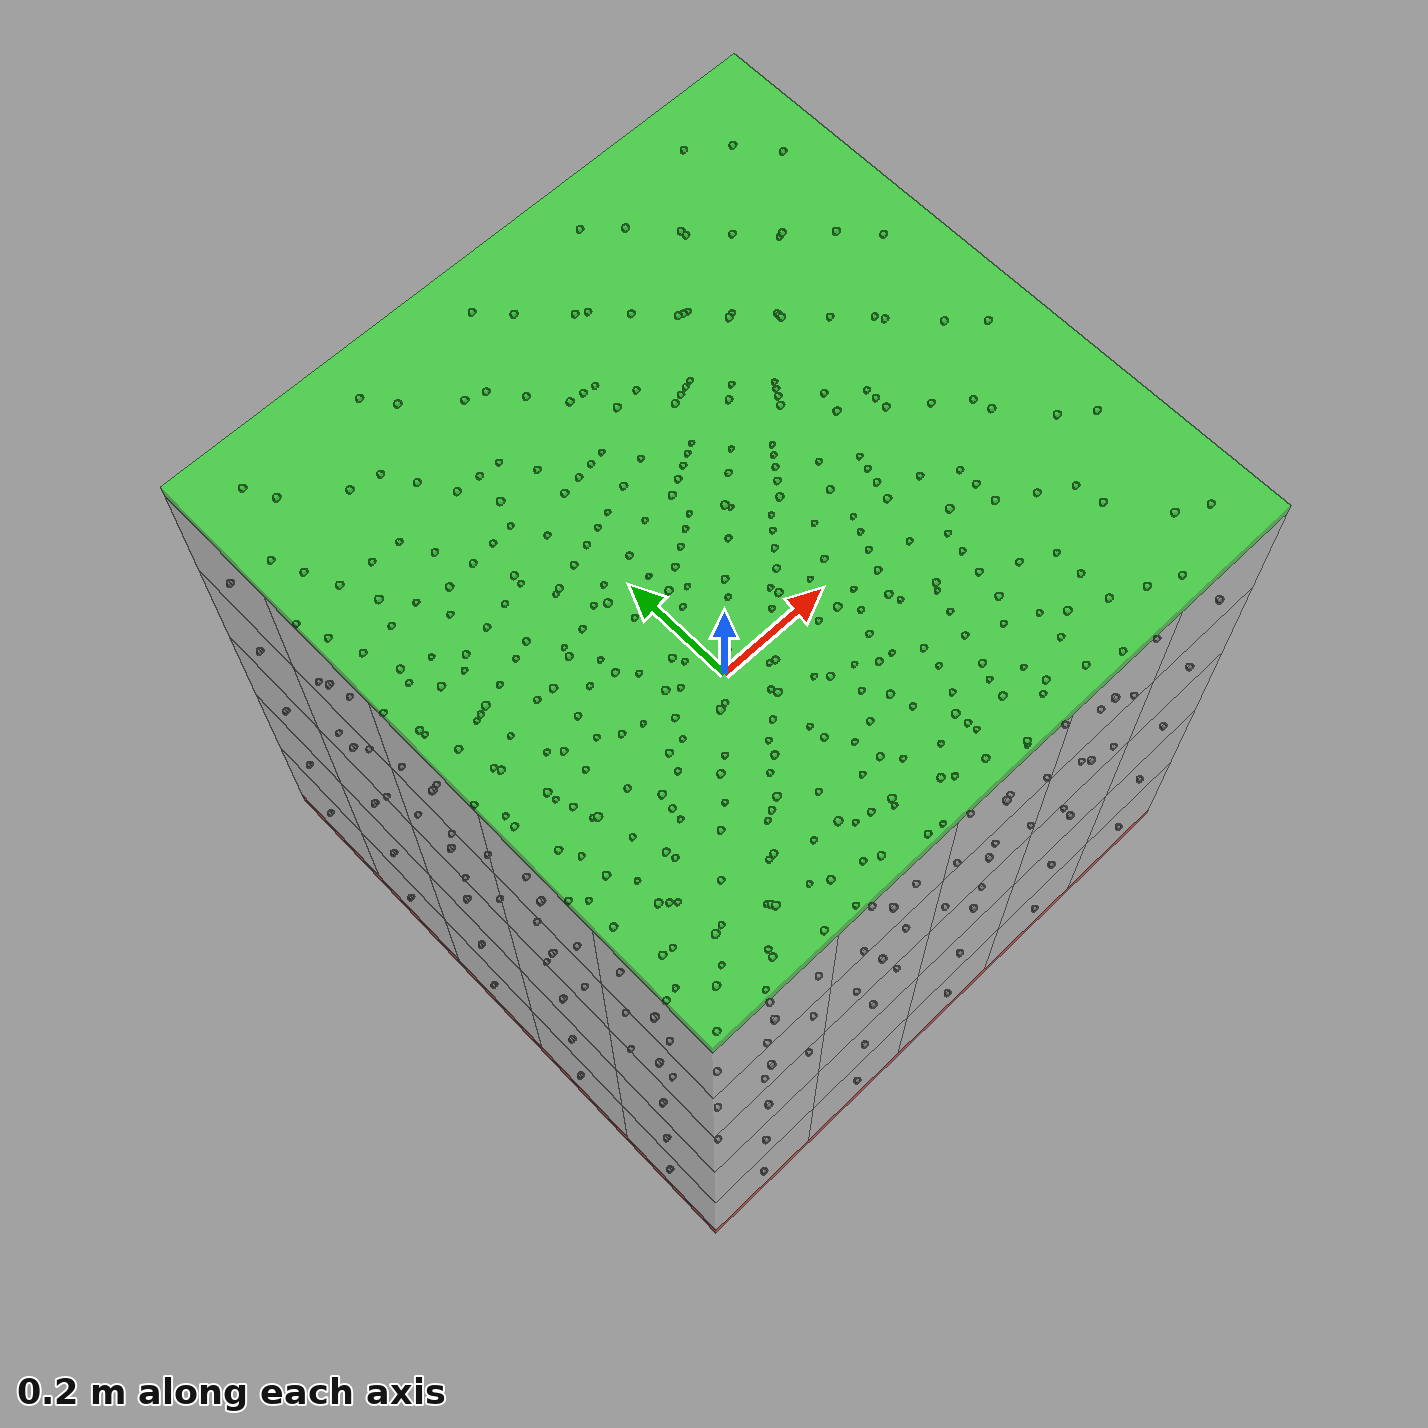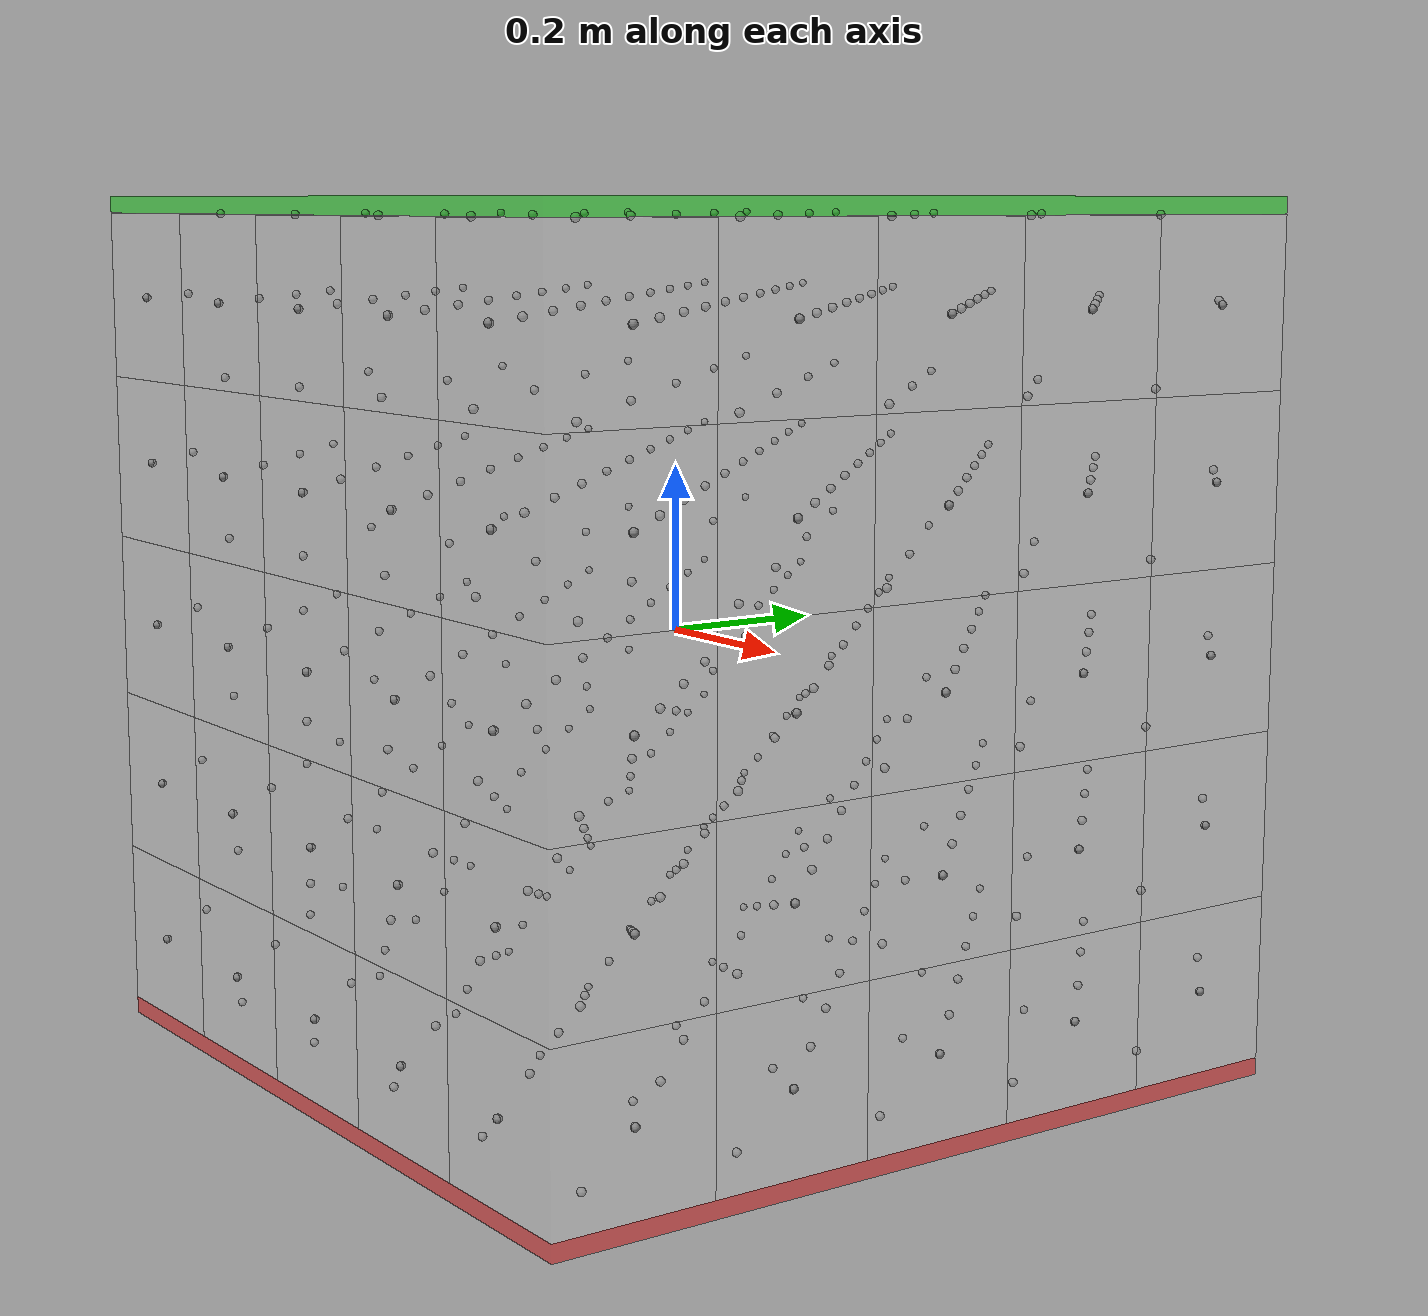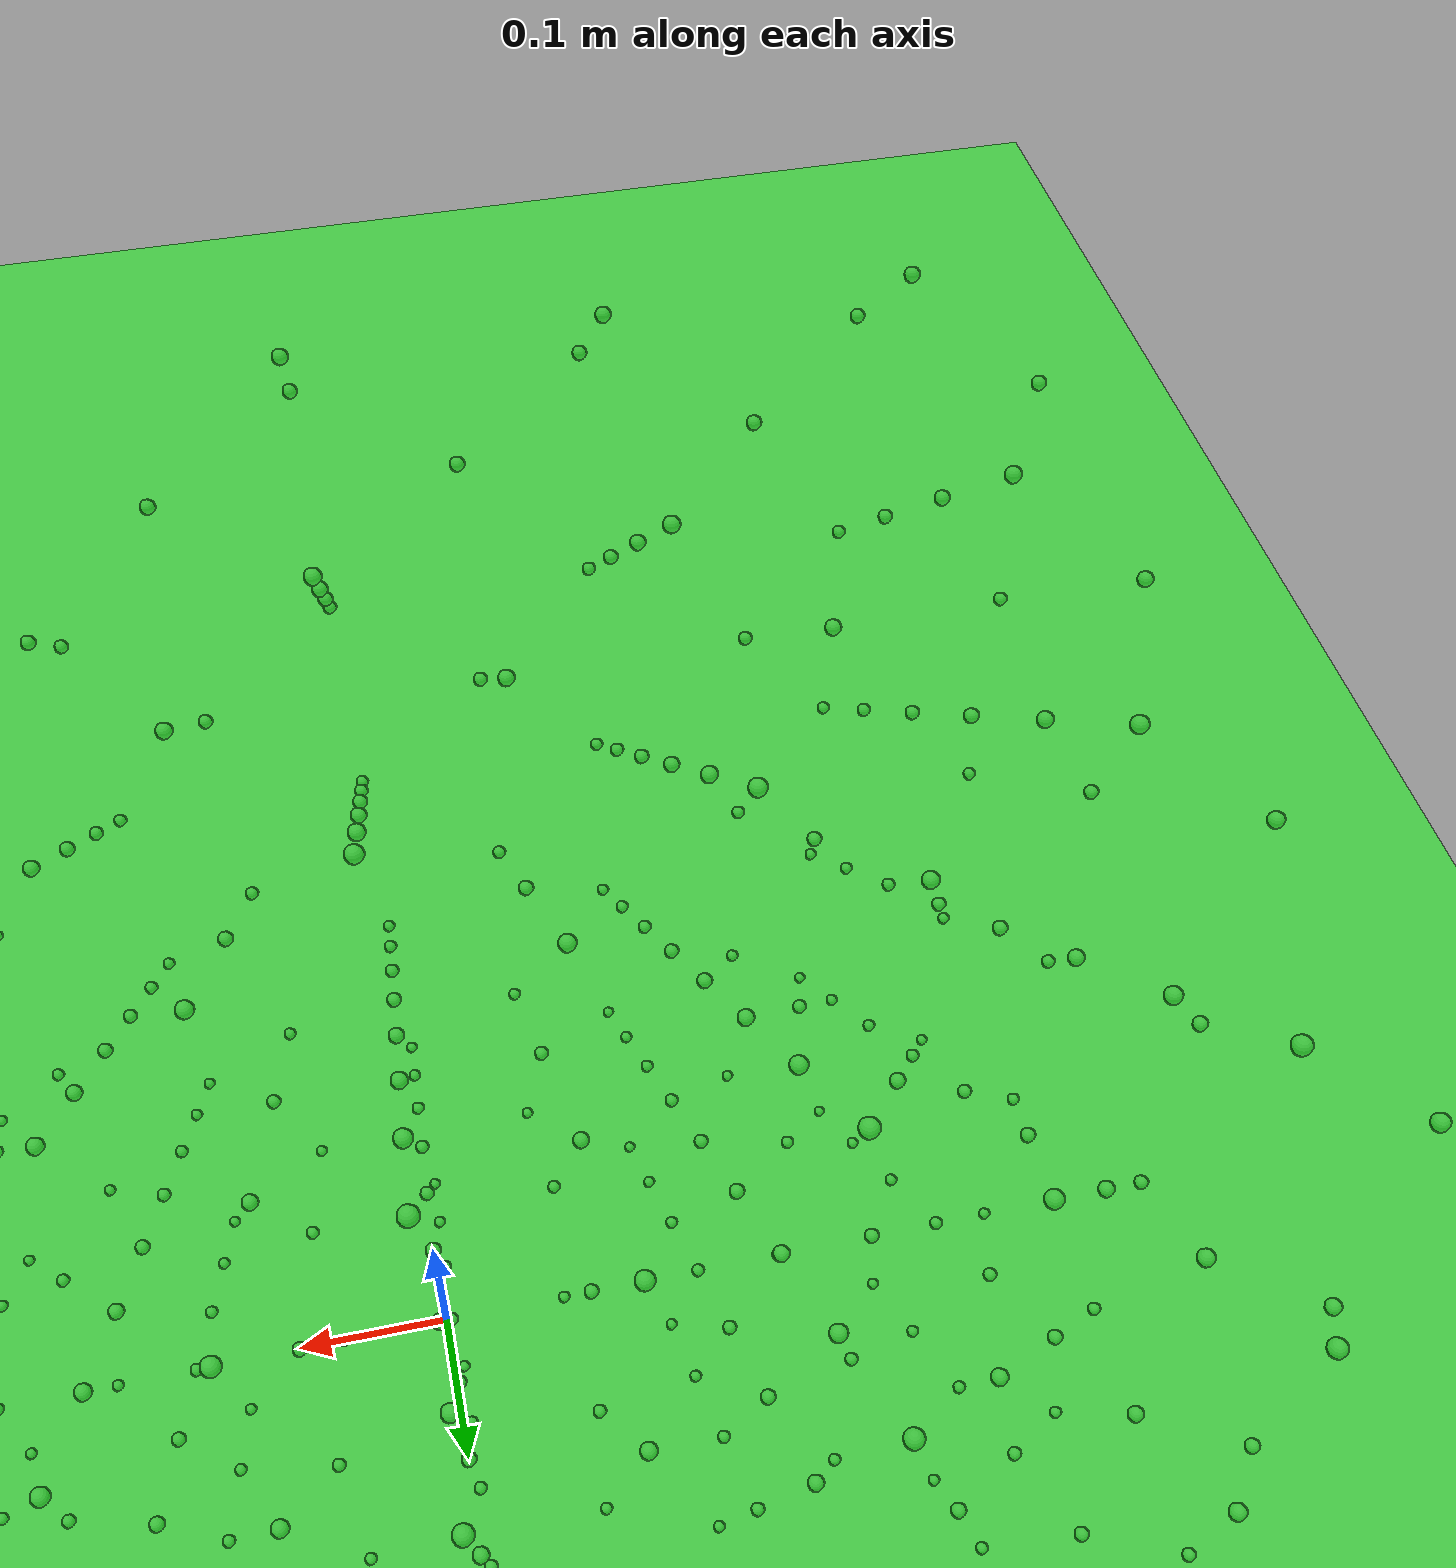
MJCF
<mujoco model="stiffness_test">
  <option integrator="implicitfast" timestep="0.001" gravity="0 0 0"><flag contact="enable"/></option>
  <default>
    <joint armature="0.01" damping="5.0"/>
    <geom friction="0.8" solref="0.02 1.0" solimp="0.9 0.95 0.001"/>
  </default>
  <worldbody>
    <light pos="0 0 5" dir="0 0 -1"/>
    <body name="BUnitBlock">
      <body name="b_bunitblock_0_0_0" pos="-0.40000 -0.40000 -0.40000">
        <joint type="slide" axis="1 0 0"/>
        <joint type="slide" axis="0 1 0"/>
        <joint type="slide" axis="0 0 1"/>
        <joint type="ball"/>
        <geom type="box" size="0.10000 0.10000 0.10000" mass="0.008000" rgba="0.9 0.9 0.9 0.5" contype="2" conaffinity="5" friction="0.8" solref="0.005 1.5" solimp="0.95 0.99 0.001 0.5 2.0"/>
        <site name="s_BUnitBlock_0_0_0_PX" pos="0.10000 0 0"/>
        <site name="s_BUnitBlock_0_0_0_NX" pos="-0.10000 0 0"/>
        <site name="s_BUnitBlock_0_0_0_PY" pos="0 0.10000 0"/>
        <site name="s_BUnitBlock_0_0_0_NY" pos="0 -0.10000 0"/>
        <site name="s_BUnitBlock_0_0_0_PZ" pos="0 0 0.10000"/>
        <site name="s_BUnitBlock_0_0_0_NZ" pos="0 0 -0.10000"/>
      </body>
      <body name="b_bunitblock_0_0_1" pos="-0.40000 -0.40000 -0.20000">
        <joint type="slide" axis="1 0 0"/>
        <joint type="slide" axis="0 1 0"/>
        <joint type="slide" axis="0 0 1"/>
        <joint type="ball"/>
        <geom type="box" size="0.10000 0.10000 0.10000" mass="0.008000" rgba="0.9 0.9 0.9 0.5" contype="2" conaffinity="5" friction="0.8" solref="0.005 1.5" solimp="0.95 0.99 0.001 0.5 2.0"/>
        <site name="s_BUnitBlock_0_0_1_PX" pos="0.10000 0 0"/>
        <site name="s_BUnitBlock_0_0_1_NX" pos="-0.10000 0 0"/>
        <site name="s_BUnitBlock_0_0_1_PY" pos="0 0.10000 0"/>
        <site name="s_BUnitBlock_0_0_1_NY" pos="0 -0.10000 0"/>
        <site name="s_BUnitBlock_0_0_1_PZ" pos="0 0 0.10000"/>
        <site name="s_BUnitBlock_0_0_1_NZ" pos="0 0 -0.10000"/>
      </body>
      <body name="b_bunitblock_0_0_2" pos="-0.40000 -0.40000 0.00000">
        <joint type="slide" axis="1 0 0"/>
        <joint type="slide" axis="0 1 0"/>
        <joint type="slide" axis="0 0 1"/>
        <joint type="ball"/>
        <geom type="box" size="0.10000 0.10000 0.10000" mass="0.008000" rgba="0.9 0.9 0.9 0.5" contype="2" conaffinity="5" friction="0.8" solref="0.005 1.5" solimp="0.95 0.99 0.001 0.5 2.0"/>
        <site name="s_BUnitBlock_0_0_2_PX" pos="0.10000 0 0"/>
        <site name="s_BUnitBlock_0_0_2_NX" pos="-0.10000 0 0"/>
        <site name="s_BUnitBlock_0_0_2_PY" pos="0 0.10000 0"/>
        <site name="s_BUnitBlock_0_0_2_NY" pos="0 -0.10000 0"/>
        <site name="s_BUnitBlock_0_0_2_PZ" pos="0 0 0.10000"/>
        <site name="s_BUnitBlock_0_0_2_NZ" pos="0 0 -0.10000"/>
      </body>
      <body name="b_bunitblock_0_0_3" pos="-0.40000 -0.40000 0.20000">
        <joint type="slide" axis="1 0 0"/>
        <joint type="slide" axis="0 1 0"/>
        <joint type="slide" axis="0 0 1"/>
        <joint type="ball"/>
        <geom type="box" size="0.10000 0.10000 0.10000" mass="0.008000" rgba="0.9 0.9 0.9 0.5" contype="2" conaffinity="5" friction="0.8" solref="0.005 1.5" solimp="0.95 0.99 0.001 0.5 2.0"/>
        <site name="s_BUnitBlock_0_0_3_PX" pos="0.10000 0 0"/>
        <site name="s_BUnitBlock_0_0_3_NX" pos="-0.10000 0 0"/>
        <site name="s_BUnitBlock_0_0_3_PY" pos="0 0.10000 0"/>
        <site name="s_BUnitBlock_0_0_3_NY" pos="0 -0.10000 0"/>
        <site name="s_BUnitBlock_0_0_3_PZ" pos="0 0 0.10000"/>
        <site name="s_BUnitBlock_0_0_3_NZ" pos="0 0 -0.10000"/>
      </body>
      <body name="b_bunitblock_0_0_4" pos="-0.40000 -0.40000 0.40000">
        <joint type="slide" axis="1 0 0"/>
        <joint type="slide" axis="0 1 0"/>
        <joint type="slide" axis="0 0 1"/>
        <joint type="ball"/>
        <geom type="box" size="0.10000 0.10000 0.10000" mass="0.008000" rgba="0.9 0.9 0.9 0.5" contype="2" conaffinity="5" friction="0.8" solref="0.005 1.5" solimp="0.95 0.99 0.001 0.5 2.0"/>
        <site name="s_BUnitBlock_0_0_4_PX" pos="0.10000 0 0"/>
        <site name="s_BUnitBlock_0_0_4_NX" pos="-0.10000 0 0"/>
        <site name="s_BUnitBlock_0_0_4_PY" pos="0 0.10000 0"/>
        <site name="s_BUnitBlock_0_0_4_NY" pos="0 -0.10000 0"/>
        <site name="s_BUnitBlock_0_0_4_PZ" pos="0 0 0.10000"/>
        <site name="s_BUnitBlock_0_0_4_NZ" pos="0 0 -0.10000"/>
      </body>
      <body name="b_bunitblock_0_1_0" pos="-0.40000 -0.20000 -0.40000">
        <joint type="slide" axis="1 0 0"/>
        <joint type="slide" axis="0 1 0"/>
        <joint type="slide" axis="0 0 1"/>
        <joint type="ball"/>
        <geom type="box" size="0.10000 0.10000 0.10000" mass="0.008000" rgba="0.9 0.9 0.9 0.5" contype="2" conaffinity="5" friction="0.8" solref="0.005 1.5" solimp="0.95 0.99 0.001 0.5 2.0"/>
        <site name="s_BUnitBlock_0_1_0_PX" pos="0.10000 0 0"/>
        <site name="s_BUnitBlock_0_1_0_NX" pos="-0.10000 0 0"/>
        <site name="s_BUnitBlock_0_1_0_PY" pos="0 0.10000 0"/>
        <site name="s_BUnitBlock_0_1_0_NY" pos="0 -0.10000 0"/>
        <site name="s_BUnitBlock_0_1_0_PZ" pos="0 0 0.10000"/>
        <site name="s_BUnitBlock_0_1_0_NZ" pos="0 0 -0.10000"/>
      </body>
      <body name="b_bunitblock_0_1_1" pos="-0.40000 -0.20000 -0.20000">
        <joint type="slide" axis="1 0 0"/>
        <joint type="slide" axis="0 1 0"/>
        <joint type="slide" axis="0 0 1"/>
        <joint type="ball"/>
        <geom type="box" size="0.10000 0.10000 0.10000" mass="0.008000" rgba="0.9 0.9 0.9 0.5" contype="2" conaffinity="5" friction="0.8" solref="0.005 1.5" solimp="0.95 0.99 0.001 0.5 2.0"/>
        <site name="s_BUnitBlock_0_1_1_PX" pos="0.10000 0 0"/>
        <site name="s_BUnitBlock_0_1_1_NX" pos="-0.10000 0 0"/>
        <site name="s_BUnitBlock_0_1_1_PY" pos="0 0.10000 0"/>
        <site name="s_BUnitBlock_0_1_1_NY" pos="0 -0.10000 0"/>
        <site name="s_BUnitBlock_0_1_1_PZ" pos="0 0 0.10000"/>
        <site name="s_BUnitBlock_0_1_1_NZ" pos="0 0 -0.10000"/>
      </body>
      <body name="b_bunitblock_0_1_2" pos="-0.40000 -0.20000 0.00000">
        <joint type="slide" axis="1 0 0"/>
        <joint type="slide" axis="0 1 0"/>
        <joint type="slide" axis="0 0 1"/>
        <joint type="ball"/>
        <geom type="box" size="0.10000 0.10000 0.10000" mass="0.008000" rgba="0.9 0.9 0.9 0.5" contype="2" conaffinity="5" friction="0.8" solref="0.005 1.5" solimp="0.95 0.99 0.001 0.5 2.0"/>
        <site name="s_BUnitBlock_0_1_2_PX" pos="0.10000 0 0"/>
        <site name="s_BUnitBlock_0_1_2_NX" pos="-0.10000 0 0"/>
        <site name="s_BUnitBlock_0_1_2_PY" pos="0 0.10000 0"/>
        <site name="s_BUnitBlock_0_1_2_NY" pos="0 -0.10000 0"/>
        <site name="s_BUnitBlock_0_1_2_PZ" pos="0 0 0.10000"/>
        <site name="s_BUnitBlock_0_1_2_NZ" pos="0 0 -0.10000"/>
      </body>
      <body name="b_bunitblock_0_1_3" pos="-0.40000 -0.20000 0.20000">
        <joint type="slide" axis="1 0 0"/>
        <joint type="slide" axis="0 1 0"/>
        <joint type="slide" axis="0 0 1"/>
        <joint type="ball"/>
        <geom type="box" size="0.10000 0.10000 0.10000" mass="0.008000" rgba="0.9 0.9 0.9 0.5" contype="2" conaffinity="5" friction="0.8" solref="0.005 1.5" solimp="0.95 0.99 0.001 0.5 2.0"/>
        <site name="s_BUnitBlock_0_1_3_PX" pos="0.10000 0 0"/>
        <site name="s_BUnitBlock_0_1_3_NX" pos="-0.10000 0 0"/>
        <site name="s_BUnitBlock_0_1_3_PY" pos="0 0.10000 0"/>
        <site name="s_BUnitBlock_0_1_3_NY" pos="0 -0.10000 0"/>
        <site name="s_BUnitBlock_0_1_3_PZ" pos="0 0 0.10000"/>
        <site name="s_BUnitBlock_0_1_3_NZ" pos="0 0 -0.10000"/>
      </body>
      <body name="b_bunitblock_0_1_4" pos="-0.40000 -0.20000 0.40000">
        <joint type="slide" axis="1 0 0"/>
        <joint type="slide" axis="0 1 0"/>
        <joint type="slide" axis="0 0 1"/>
        <joint type="ball"/>
        <geom type="box" size="0.10000 0.10000 0.10000" mass="0.008000" rgba="0.9 0.9 0.9 0.5" contype="2" conaffinity="5" friction="0.8" solref="0.005 1.5" solimp="0.95 0.99 0.001 0.5 2.0"/>
        <site name="s_BUnitBlock_0_1_4_PX" pos="0.10000 0 0"/>
        <site name="s_BUnitBlock_0_1_4_NX" pos="-0.10000 0 0"/>
        <site name="s_BUnitBlock_0_1_4_PY" pos="0 0.10000 0"/>
        <site name="s_BUnitBlock_0_1_4_NY" pos="0 -0.10000 0"/>
        <site name="s_BUnitBlock_0_1_4_PZ" pos="0 0 0.10000"/>
        <site name="s_BUnitBlock_0_1_4_NZ" pos="0 0 -0.10000"/>
      </body>
      <body name="b_bunitblock_0_2_0" pos="-0.40000 0.00000 -0.40000">
        <joint type="slide" axis="1 0 0"/>
        <joint type="slide" axis="0 1 0"/>
        <joint type="slide" axis="0 0 1"/>
        <joint type="ball"/>
        <geom type="box" size="0.10000 0.10000 0.10000" mass="0.008000" rgba="0.9 0.9 0.9 0.5" contype="2" conaffinity="5" friction="0.8" solref="0.005 1.5" solimp="0.95 0.99 0.001 0.5 2.0"/>
        <site name="s_BUnitBlock_0_2_0_PX" pos="0.10000 0 0"/>
        <site name="s_BUnitBlock_0_2_0_NX" pos="-0.10000 0 0"/>
        <site name="s_BUnitBlock_0_2_0_PY" pos="0 0.10000 0"/>
        <site name="s_BUnitBlock_0_2_0_NY" pos="0 -0.10000 0"/>
        <site name="s_BUnitBlock_0_2_0_PZ" pos="0 0 0.10000"/>
        <site name="s_BUnitBlock_0_2_0_NZ" pos="0 0 -0.10000"/>
      </body>
      <body name="b_bunitblock_0_2_1" pos="-0.40000 0.00000 -0.20000">
        <joint type="slide" axis="1 0 0"/>
        <joint type="slide" axis="0 1 0"/>
        <joint type="slide" axis="0 0 1"/>
        <joint type="ball"/>
        <geom type="box" size="0.10000 0.10000 0.10000" mass="0.008000" rgba="0.9 0.9 0.9 0.5" contype="2" conaffinity="5" friction="0.8" solref="0.005 1.5" solimp="0.95 0.99 0.001 0.5 2.0"/>
        <site name="s_BUnitBlock_0_2_1_PX" pos="0.10000 0 0"/>
        <site name="s_BUnitBlock_0_2_1_NX" pos="-0.10000 0 0"/>
        <site name="s_BUnitBlock_0_2_1_PY" pos="0 0.10000 0"/>
        <site name="s_BUnitBlock_0_2_1_NY" pos="0 -0.10000 0"/>
        <site name="s_BUnitBlock_0_2_1_PZ" pos="0 0 0.10000"/>
        <site name="s_BUnitBlock_0_2_1_NZ" pos="0 0 -0.10000"/>
      </body>
      <body name="b_bunitblock_0_2_2" pos="-0.40000 0.00000 0.00000">
        <joint type="slide" axis="1 0 0"/>
        <joint type="slide" axis="0 1 0"/>
        <joint type="slide" axis="0 0 1"/>
        <joint type="ball"/>
        <geom type="box" size="0.10000 0.10000 0.10000" mass="0.008000" rgba="0.9 0.9 0.9 0.5" contype="2" conaffinity="5" friction="0.8" solref="0.005 1.5" solimp="0.95 0.99 0.001 0.5 2.0"/>
        <site name="s_BUnitBlock_0_2_2_PX" pos="0.10000 0 0"/>
        <site name="s_BUnitBlock_0_2_2_NX" pos="-0.10000 0 0"/>
        <site name="s_BUnitBlock_0_2_2_PY" pos="0 0.10000 0"/>
        <site name="s_BUnitBlock_0_2_2_NY" pos="0 -0.10000 0"/>
        <site name="s_BUnitBlock_0_2_2_PZ" pos="0 0 0.10000"/>
        <site name="s_BUnitBlock_0_2_2_NZ" pos="0 0 -0.10000"/>
      </body>
      <body name="b_bunitblock_0_2_3" pos="-0.40000 0.00000 0.20000">
        <joint type="slide" axis="1 0 0"/>
        <joint type="slide" axis="0 1 0"/>
        <joint type="slide" axis="0 0 1"/>
        <joint type="ball"/>
        <geom type="box" size="0.10000 0.10000 0.10000" mass="0.008000" rgba="0.9 0.9 0.9 0.5" contype="2" conaffinity="5" friction="0.8" solref="0.005 1.5" solimp="0.95 0.99 0.001 0.5 2.0"/>
        <site name="s_BUnitBlock_0_2_3_PX" pos="0.10000 0 0"/>
        <site name="s_BUnitBlock_0_2_3_NX" pos="-0.10000 0 0"/>
        <site name="s_BUnitBlock_0_2_3_PY" pos="0 0.10000 0"/>
        <site name="s_BUnitBlock_0_2_3_NY" pos="0 -0.10000 0"/>
        <site name="s_BUnitBlock_0_2_3_PZ" pos="0 0 0.10000"/>
        <site name="s_BUnitBlock_0_2_3_NZ" pos="0 0 -0.10000"/>
      </body>
      <body name="b_bunitblock_0_2_4" pos="-0.40000 0.00000 0.40000">
        <joint type="slide" axis="1 0 0"/>
        <joint type="slide" axis="0 1 0"/>
        <joint type="slide" axis="0 0 1"/>
        <joint type="ball"/>
        <geom type="box" size="0.10000 0.10000 0.10000" mass="0.008000" rgba="0.9 0.9 0.9 0.5" contype="2" conaffinity="5" friction="0.8" solref="0.005 1.5" solimp="0.95 0.99 0.001 0.5 2.0"/>
        <site name="s_BUnitBlock_0_2_4_PX" pos="0.10000 0 0"/>
        <site name="s_BUnitBlock_0_2_4_NX" pos="-0.10000 0 0"/>
        <site name="s_BUnitBlock_0_2_4_PY" pos="0 0.10000 0"/>
        <site name="s_BUnitBlock_0_2_4_NY" pos="0 -0.10000 0"/>
        <site name="s_BUnitBlock_0_2_4_PZ" pos="0 0 0.10000"/>
        <site name="s_BUnitBlock_0_2_4_NZ" pos="0 0 -0.10000"/>
      </body>
      <body name="b_bunitblock_0_3_0" pos="-0.40000 0.20000 -0.40000">
        <joint type="slide" axis="1 0 0"/>
        <joint type="slide" axis="0 1 0"/>
        <joint type="slide" axis="0 0 1"/>
        <joint type="ball"/>
        <geom type="box" size="0.10000 0.10000 0.10000" mass="0.008000" rgba="0.9 0.9 0.9 0.5" contype="2" conaffinity="5" friction="0.8" solref="0.005 1.5" solimp="0.95 0.99 0.001 0.5 2.0"/>
        <site name="s_BUnitBlock_0_3_0_PX" pos="0.10000 0 0"/>
        <site name="s_BUnitBlock_0_3_0_NX" pos="-0.10000 0 0"/>
        <site name="s_BUnitBlock_0_3_0_PY" pos="0 0.10000 0"/>
        <site name="s_BUnitBlock_0_3_0_NY" pos="0 -0.10000 0"/>
        <site name="s_BUnitBlock_0_3_0_PZ" pos="0 0 0.10000"/>
        <site name="s_BUnitBlock_0_3_0_NZ" pos="0 0 -0.10000"/>
      </body>
      <body name="b_bunitblock_0_3_1" pos="-0.40000 0.20000 -0.20000">
        <joint type="slide" axis="1 0 0"/>
        <joint type="slide" axis="0 1 0"/>
        <joint type="slide" axis="0 0 1"/>
        <joint type="ball"/>
        <geom type="box" size="0.10000 0.10000 0.10000" mass="0.008000" rgba="0.9 0.9 0.9 0.5" contype="2" conaffinity="5" friction="0.8" solref="0.005 1.5" solimp="0.95 0.99 0.001 0.5 2.0"/>
        <site name="s_BUnitBlock_0_3_1_PX" pos="0.10000 0 0"/>
        <site name="s_BUnitBlock_0_3_1_NX" pos="-0.10000 0 0"/>
        <site name="s_BUnitBlock_0_3_1_PY" pos="0 0.10000 0"/>
        <site name="s_BUnitBlock_0_3_1_NY" pos="0 -0.10000 0"/>
        <site name="s_BUnitBlock_0_3_1_PZ" pos="0 0 0.10000"/>
        <site name="s_BUnitBlock_0_3_1_NZ" pos="0 0 -0.10000"/>
      </body>
      <body name="b_bunitblock_0_3_2" pos="-0.40000 0.20000 0.00000">
        <joint type="slide" axis="1 0 0"/>
        <joint type="slide" axis="0 1 0"/>
        <joint type="slide" axis="0 0 1"/>
        <joint type="ball"/>
        <geom type="box" size="0.10000 0.10000 0.10000" mass="0.008000" rgba="0.9 0.9 0.9 0.5" contype="2" conaffinity="5" friction="0.8" solref="0.005 1.5" solimp="0.95 0.99 0.001 0.5 2.0"/>
        <site name="s_BUnitBlock_0_3_2_PX" pos="0.10000 0 0"/>
        <site name="s_BUnitBlock_0_3_2_NX" pos="-0.10000 0 0"/>
        <site name="s_BUnitBlock_0_3_2_PY" pos="0 0.10000 0"/>
        <site name="s_BUnitBlock_0_3_2_NY" pos="0 -0.10000 0"/>
        <site name="s_BUnitBlock_0_3_2_PZ" pos="0 0 0.10000"/>
        <site name="s_BUnitBlock_0_3_2_NZ" pos="0 0 -0.10000"/>
      </body>
      <body name="b_bunitblock_0_3_3" pos="-0.40000 0.20000 0.20000">
        <joint type="slide" axis="1 0 0"/>
        <joint type="slide" axis="0 1 0"/>
        <joint type="slide" axis="0 0 1"/>
        <joint type="ball"/>
        <geom type="box" size="0.10000 0.10000 0.10000" mass="0.008000" rgba="0.9 0.9 0.9 0.5" contype="2" conaffinity="5" friction="0.8" solref="0.005 1.5" solimp="0.95 0.99 0.001 0.5 2.0"/>
        <site name="s_BUnitBlock_0_3_3_PX" pos="0.10000 0 0"/>
        <site name="s_BUnitBlock_0_3_3_NX" pos="-0.10000 0 0"/>
        <site name="s_BUnitBlock_0_3_3_PY" pos="0 0.10000 0"/>
        <site name="s_BUnitBlock_0_3_3_NY" pos="0 -0.10000 0"/>
        <site name="s_BUnitBlock_0_3_3_PZ" pos="0 0 0.10000"/>
        <site name="s_BUnitBlock_0_3_3_NZ" pos="0 0 -0.10000"/>
      </body>
      <body name="b_bunitblock_0_3_4" pos="-0.40000 0.20000 0.40000">
        <joint type="slide" axis="1 0 0"/>
        <joint type="slide" axis="0 1 0"/>
        <joint type="slide" axis="0 0 1"/>
        <joint type="ball"/>
        <geom type="box" size="0.10000 0.10000 0.10000" mass="0.008000" rgba="0.9 0.9 0.9 0.5" contype="2" conaffinity="5" friction="0.8" solref="0.005 1.5" solimp="0.95 0.99 0.001 0.5 2.0"/>
        <site name="s_BUnitBlock_0_3_4_PX" pos="0.10000 0 0"/>
        <site name="s_BUnitBlock_0_3_4_NX" pos="-0.10000 0 0"/>
        <site name="s_BUnitBlock_0_3_4_PY" pos="0 0.10000 0"/>
        <site name="s_BUnitBlock_0_3_4_NY" pos="0 -0.10000 0"/>
        <site name="s_BUnitBlock_0_3_4_PZ" pos="0 0 0.10000"/>
        <site name="s_BUnitBlock_0_3_4_NZ" pos="0 0 -0.10000"/>
      </body>
      <body name="b_bunitblock_0_4_0" pos="-0.40000 0.40000 -0.40000">
        <joint type="slide" axis="1 0 0"/>
        <joint type="slide" axis="0 1 0"/>
        <joint type="slide" axis="0 0 1"/>
        <joint type="ball"/>
        <geom type="box" size="0.10000 0.10000 0.10000" mass="0.008000" rgba="0.9 0.9 0.9 0.5" contype="2" conaffinity="5" friction="0.8" solref="0.005 1.5" solimp="0.95 0.99 0.001 0.5 2.0"/>
        <site name="s_BUnitBlock_0_4_0_PX" pos="0.10000 0 0"/>
        <site name="s_BUnitBlock_0_4_0_NX" pos="-0.10000 0 0"/>
        <site name="s_BUnitBlock_0_4_0_PY" pos="0 0.10000 0"/>
        <site name="s_BUnitBlock_0_4_0_NY" pos="0 -0.10000 0"/>
        <site name="s_BUnitBlock_0_4_0_PZ" pos="0 0 0.10000"/>
        <site name="s_BUnitBlock_0_4_0_NZ" pos="0 0 -0.10000"/>
      </body>
      <body name="b_bunitblock_0_4_1" pos="-0.40000 0.40000 -0.20000">
        <joint type="slide" axis="1 0 0"/>
        <joint type="slide" axis="0 1 0"/>
        <joint type="slide" axis="0 0 1"/>
        <joint type="ball"/>
        <geom type="box" size="0.10000 0.10000 0.10000" mass="0.008000" rgba="0.9 0.9 0.9 0.5" contype="2" conaffinity="5" friction="0.8" solref="0.005 1.5" solimp="0.95 0.99 0.001 0.5 2.0"/>
        <site name="s_BUnitBlock_0_4_1_PX" pos="0.10000 0 0"/>
        <site name="s_BUnitBlock_0_4_1_NX" pos="-0.10000 0 0"/>
        <site name="s_BUnitBlock_0_4_1_PY" pos="0 0.10000 0"/>
        <site name="s_BUnitBlock_0_4_1_NY" pos="0 -0.10000 0"/>
        <site name="s_BUnitBlock_0_4_1_PZ" pos="0 0 0.10000"/>
        <site name="s_BUnitBlock_0_4_1_NZ" pos="0 0 -0.10000"/>
      </body>
      <body name="b_bunitblock_0_4_2" pos="-0.40000 0.40000 0.00000">
        <joint type="slide" axis="1 0 0"/>
        <joint type="slide" axis="0 1 0"/>
        <joint type="slide" axis="0 0 1"/>
        <joint type="ball"/>
        <geom type="box" size="0.10000 0.10000 0.10000" mass="0.008000" rgba="0.9 0.9 0.9 0.5" contype="2" conaffinity="5" friction="0.8" solref="0.005 1.5" solimp="0.95 0.99 0.001 0.5 2.0"/>
        <site name="s_BUnitBlock_0_4_2_PX" pos="0.10000 0 0"/>
        <site name="s_BUnitBlock_0_4_2_NX" pos="-0.10000 0 0"/>
        <site name="s_BUnitBlock_0_4_2_PY" pos="0 0.10000 0"/>
        <site name="s_BUnitBlock_0_4_2_NY" pos="0 -0.10000 0"/>
        <site name="s_BUnitBlock_0_4_2_PZ" pos="0 0 0.10000"/>
        <site name="s_BUnitBlock_0_4_2_NZ" pos="0 0 -0.10000"/>
      </body>
      <body name="b_bunitblock_0_4_3" pos="-0.40000 0.40000 0.20000">
        <joint type="slide" axis="1 0 0"/>
        <joint type="slide" axis="0 1 0"/>
        <joint type="slide" axis="0 0 1"/>
        <joint type="ball"/>
        <geom type="box" size="0.10000 0.10000 0.10000" mass="0.008000" rgba="0.9 0.9 0.9 0.5" contype="2" conaffinity="5" friction="0.8" solref="0.005 1.5" solimp="0.95 0.99 0.001 0.5 2.0"/>
        <site name="s_BUnitBlock_0_4_3_PX" pos="0.10000 0 0"/>
        <site name="s_BUnitBlock_0_4_3_NX" pos="-0.10000 0 0"/>
        <site name="s_BUnitBlock_0_4_3_PY" pos="0 0.10000 0"/>
        <site name="s_BUnitBlock_0_4_3_NY" pos="0 -0.10000 0"/>
        <site name="s_BUnitBlock_0_4_3_PZ" pos="0 0 0.10000"/>
        <site name="s_BUnitBlock_0_4_3_NZ" pos="0 0 -0.10000"/>
      </body>
      <body name="b_bunitblock_0_4_4" pos="-0.40000 0.40000 0.40000">
        <joint type="slide" axis="1 0 0"/>
        <joint type="slide" axis="0 1 0"/>
        <joint type="slide" axis="0 0 1"/>
        <joint type="ball"/>
        <geom type="box" size="0.10000 0.10000 0.10000" mass="0.008000" rgba="0.9 0.9 0.9 0.5" contype="2" conaffinity="5" friction="0.8" solref="0.005 1.5" solimp="0.95 0.99 0.001 0.5 2.0"/>
        <site name="s_BUnitBlock_0_4_4_PX" pos="0.10000 0 0"/>
        <site name="s_BUnitBlock_0_4_4_NX" pos="-0.10000 0 0"/>
        <site name="s_BUnitBlock_0_4_4_PY" pos="0 0.10000 0"/>
        <site name="s_BUnitBlock_0_4_4_NY" pos="0 -0.10000 0"/>
        <site name="s_BUnitBlock_0_4_4_PZ" pos="0 0 0.10000"/>
        <site name="s_BUnitBlock_0_4_4_NZ" pos="0 0 -0.10000"/>
      </body>
      <body name="b_bunitblock_1_0_0" pos="-0.20000 -0.40000 -0.40000">
        <joint type="slide" axis="1 0 0"/>
        <joint type="slide" axis="0 1 0"/>
        <joint type="slide" axis="0 0 1"/>
        <joint type="ball"/>
        <geom type="box" size="0.10000 0.10000 0.10000" mass="0.008000" rgba="0.9 0.9 0.9 0.5" contype="2" conaffinity="5" friction="0.8" solref="0.005 1.5" solimp="0.95 0.99 0.001 0.5 2.0"/>
        <site name="s_BUnitBlock_1_0_0_PX" pos="0.10000 0 0"/>
        <site name="s_BUnitBlock_1_0_0_NX" pos="-0.10000 0 0"/>
        <site name="s_BUnitBlock_1_0_0_PY" pos="0 0.10000 0"/>
        <site name="s_BUnitBlock_1_0_0_NY" pos="0 -0.10000 0"/>
        <site name="s_BUnitBlock_1_0_0_PZ" pos="0 0 0.10000"/>
        <site name="s_BUnitBlock_1_0_0_NZ" pos="0 0 -0.10000"/>
      </body>
      <body name="b_bunitblock_1_0_1" pos="-0.20000 -0.40000 -0.20000">
        <joint type="slide" axis="1 0 0"/>
        <joint type="slide" axis="0 1 0"/>
        <joint type="slide" axis="0 0 1"/>
        <joint type="ball"/>
        <geom type="box" size="0.10000 0.10000 0.10000" mass="0.008000" rgba="0.9 0.9 0.9 0.5" contype="2" conaffinity="5" friction="0.8" solref="0.005 1.5" solimp="0.95 0.99 0.001 0.5 2.0"/>
        <site name="s_BUnitBlock_1_0_1_PX" pos="0.10000 0 0"/>
        <site name="s_BUnitBlock_1_0_1_NX" pos="-0.10000 0 0"/>
        <site name="s_BUnitBlock_1_0_1_PY" pos="0 0.10000 0"/>
        <site name="s_BUnitBlock_1_0_1_NY" pos="0 -0.10000 0"/>
        <site name="s_BUnitBlock_1_0_1_PZ" pos="0 0 0.10000"/>
        <site name="s_BUnitBlock_1_0_1_NZ" pos="0 0 -0.10000"/>
      </body>
      <body name="b_bunitblock_1_0_2" pos="-0.20000 -0.40000 0.00000">
        <joint type="slide" axis="1 0 0"/>
        <joint type="slide" axis="0 1 0"/>
        <joint type="slide" axis="0 0 1"/>
        <joint type="ball"/>
        <geom type="box" size="0.10000 0.10000 0.10000" mass="0.008000" rgba="0.9 0.9 0.9 0.5" contype="2" conaffinity="5" friction="0.8" solref="0.005 1.5" solimp="0.95 0.99 0.001 0.5 2.0"/>
        <site name="s_BUnitBlock_1_0_2_PX" pos="0.10000 0 0"/>
        <site name="s_BUnitBlock_1_0_2_NX" pos="-0.10000 0 0"/>
        <site name="s_BUnitBlock_1_0_2_PY" pos="0 0.10000 0"/>
        <site name="s_BUnitBlock_1_0_2_NY" pos="0 -0.10000 0"/>
        <site name="s_BUnitBlock_1_0_2_PZ" pos="0 0 0.10000"/>
        <site name="s_BUnitBlock_1_0_2_NZ" pos="0 0 -0.10000"/>
      </body>
      <body name="b_bunitblock_1_0_3" pos="-0.20000 -0.40000 0.20000">
        <joint type="slide" axis="1 0 0"/>
        <joint type="slide" axis="0 1 0"/>
        <joint type="slide" axis="0 0 1"/>
        <joint type="ball"/>
        <geom type="box" size="0.10000 0.10000 0.10000" mass="0.008000" rgba="0.9 0.9 0.9 0.5" contype="2" conaffinity="5" friction="0.8" solref="0.005 1.5" solimp="0.95 0.99 0.001 0.5 2.0"/>
        <site name="s_BUnitBlock_1_0_3_PX" pos="0.10000 0 0"/>
        <site name="s_BUnitBlock_1_0_3_NX" pos="-0.10000 0 0"/>
        <site name="s_BUnitBlock_1_0_3_PY" pos="0 0.10000 0"/>
        <site name="s_BUnitBlock_1_0_3_NY" pos="0 -0.10000 0"/>
        <site name="s_BUnitBlock_1_0_3_PZ" pos="0 0 0.10000"/>
        <site name="s_BUnitBlock_1_0_3_NZ" pos="0 0 -0.10000"/>
      </body>
      <body name="b_bunitblock_1_0_4" pos="-0.20000 -0.40000 0.40000">
        <joint type="slide" axis="1 0 0"/>
        <joint type="slide" axis="0 1 0"/>
        <joint type="slide" axis="0 0 1"/>
        <joint type="ball"/>
        <geom type="box" size="0.10000 0.10000 0.10000" mass="0.008000" rgba="0.9 0.9 0.9 0.5" contype="2" conaffinity="5" friction="0.8" solref="0.005 1.5" solimp="0.95 0.99 0.001 0.5 2.0"/>
        <site name="s_BUnitBlock_1_0_4_PX" pos="0.10000 0 0"/>
        <site name="s_BUnitBlock_1_0_4_NX" pos="-0.10000 0 0"/>
        <site name="s_BUnitBlock_1_0_4_PY" pos="0 0.10000 0"/>
        <site name="s_BUnitBlock_1_0_4_NY" pos="0 -0.10000 0"/>
        <site name="s_BUnitBlock_1_0_4_PZ" pos="0 0 0.10000"/>
        <site name="s_BUnitBlock_1_0_4_NZ" pos="0 0 -0.10000"/>
      </body>
      <body name="b_bunitblock_1_1_0" pos="-0.20000 -0.20000 -0.40000">
        <joint type="slide" axis="1 0 0"/>
        <joint type="slide" axis="0 1 0"/>
        <joint type="slide" axis="0 0 1"/>
        <joint type="ball"/>
        <geom type="box" size="0.10000 0.10000 0.10000" mass="0.008000" rgba="0.9 0.9 0.9 0.5" contype="2" conaffinity="5" friction="0.8" solref="0.005 1.5" solimp="0.95 0.99 0.001 0.5 2.0"/>
        <site name="s_BUnitBlock_1_1_0_PX" pos="0.10000 0 0"/>
        <site name="s_BUnitBlock_1_1_0_NX" pos="-0.10000 0 0"/>
        <site name="s_BUnitBlock_1_1_0_PY" pos="0 0.10000 0"/>
        <site name="s_BUnitBlock_1_1_0_NY" pos="0 -0.10000 0"/>
        <site name="s_BUnitBlock_1_1_0_PZ" pos="0 0 0.10000"/>
        <site name="s_BUnitBlock_1_1_0_NZ" pos="0 0 -0.10000"/>
      </body>
      <body name="b_bunitblock_1_1_1" pos="-0.20000 -0.20000 -0.20000">
        <joint type="slide" axis="1 0 0"/>
        <joint type="slide" axis="0 1 0"/>
        <joint type="slide" axis="0 0 1"/>
        <joint type="ball"/>
        <geom type="box" size="0.10000 0.10000 0.10000" mass="0.008000" rgba="0.9 0.9 0.9 0.5" contype="2" conaffinity="5" friction="0.8" solref="0.005 1.5" solimp="0.95 0.99 0.001 0.5 2.0"/>
        <site name="s_BUnitBlock_1_1_1_PX" pos="0.10000 0 0"/>
        <site name="s_BUnitBlock_1_1_1_NX" pos="-0.10000 0 0"/>
        <site name="s_BUnitBlock_1_1_1_PY" pos="0 0.10000 0"/>
        <site name="s_BUnitBlock_1_1_1_NY" pos="0 -0.10000 0"/>
        <site name="s_BUnitBlock_1_1_1_PZ" pos="0 0 0.10000"/>
        <site name="s_BUnitBlock_1_1_1_NZ" pos="0 0 -0.10000"/>
      </body>
      <body name="b_bunitblock_1_1_2" pos="-0.20000 -0.20000 0.00000">
        <joint type="slide" axis="1 0 0"/>
        <joint type="slide" axis="0 1 0"/>
        <joint type="slide" axis="0 0 1"/>
        <joint type="ball"/>
        <geom type="box" size="0.10000 0.10000 0.10000" mass="0.008000" rgba="0.9 0.9 0.9 0.5" contype="2" conaffinity="5" friction="0.8" solref="0.005 1.5" solimp="0.95 0.99 0.001 0.5 2.0"/>
        <site name="s_BUnitBlock_1_1_2_PX" pos="0.10000 0 0"/>
        <site name="s_BUnitBlock_1_1_2_NX" pos="-0.10000 0 0"/>
        <site name="s_BUnitBlock_1_1_2_PY" pos="0 0.10000 0"/>
        <site name="s_BUnitBlock_1_1_2_NY" pos="0 -0.10000 0"/>
        <site name="s_BUnitBlock_1_1_2_PZ" pos="0 0 0.10000"/>
        <site name="s_BUnitBlock_1_1_2_NZ" pos="0 0 -0.10000"/>
      </body>
      <body name="b_bunitblock_1_1_3" pos="-0.20000 -0.20000 0.20000">
        <joint type="slide" axis="1 0 0"/>
        <joint type="slide" axis="0 1 0"/>
        <joint type="slide" axis="0 0 1"/>
        <joint type="ball"/>
        <geom type="box" size="0.10000 0.10000 0.10000" mass="0.008000" rgba="0.9 0.9 0.9 0.5" contype="2" conaffinity="5" friction="0.8" solref="0.005 1.5" solimp="0.95 0.99 0.001 0.5 2.0"/>
        <site name="s_BUnitBlock_1_1_3_PX" pos="0.10000 0 0"/>
        <site name="s_BUnitBlock_1_1_3_NX" pos="-0.10000 0 0"/>
        <site name="s_BUnitBlock_1_1_3_PY" pos="0 0.10000 0"/>
        <site name="s_BUnitBlock_1_1_3_NY" pos="0 -0.10000 0"/>
        <site name="s_BUnitBlock_1_1_3_PZ" pos="0 0 0.10000"/>
        <site name="s_BUnitBlock_1_1_3_NZ" pos="0 0 -0.10000"/>
      </body>
      <body name="b_bunitblock_1_1_4" pos="-0.20000 -0.20000 0.40000">
        <joint type="slide" axis="1 0 0"/>
        <joint type="slide" axis="0 1 0"/>
        <joint type="slide" axis="0 0 1"/>
        <joint type="ball"/>
        <geom type="box" size="0.10000 0.10000 0.10000" mass="0.008000" rgba="0.9 0.9 0.9 0.5" contype="2" conaffinity="5" friction="0.8" solref="0.005 1.5" solimp="0.95 0.99 0.001 0.5 2.0"/>
        <site name="s_BUnitBlock_1_1_4_PX" pos="0.10000 0 0"/>
        <site name="s_BUnitBlock_1_1_4_NX" pos="-0.10000 0 0"/>
        <site name="s_BUnitBlock_1_1_4_PY" pos="0 0.10000 0"/>
        <site name="s_BUnitBlock_1_1_4_NY" pos="0 -0.10000 0"/>
        <site name="s_BUnitBlock_1_1_4_PZ" pos="0 0 0.10000"/>
        <site name="s_BUnitBlock_1_1_4_NZ" pos="0 0 -0.10000"/>
      </body>
      <body name="b_bunitblock_1_2_0" pos="-0.20000 0.00000 -0.40000">
        <joint type="slide" axis="1 0 0"/>
        <joint type="slide" axis="0 1 0"/>
        <joint type="slide" axis="0 0 1"/>
        <joint type="ball"/>
        <geom type="box" size="0.10000 0.10000 0.10000" mass="0.008000" rgba="0.9 0.9 0.9 0.5" contype="2" conaffinity="5" friction="0.8" solref="0.005 1.5" solimp="0.95 0.99 0.001 0.5 2.0"/>
        <site name="s_BUnitBlock_1_2_0_PX" pos="0.10000 0 0"/>
        <site name="s_BUnitBlock_1_2_0_NX" pos="-0.10000 0 0"/>
        <site name="s_BUnitBlock_1_2_0_PY" pos="0 0.10000 0"/>
        <site name="s_BUnitBlock_1_2_0_NY" pos="0 -0.10000 0"/>
        <site name="s_BUnitBlock_1_2_0_PZ" pos="0 0 0.10000"/>
        <site name="s_BUnitBlock_1_2_0_NZ" pos="0 0 -0.10000"/>
      </body>
      <body name="b_bunitblock_1_2_1" pos="-0.20000 0.00000 -0.20000">
        <joint type="slide" axis="1 0 0"/>
        <joint type="slide" axis="0 1 0"/>
        <joint type="slide" axis="0 0 1"/>
        <joint type="ball"/>
        <geom type="box" size="0.10000 0.10000 0.10000" mass="0.008000" rgba="0.9 0.9 0.9 0.5" contype="2" conaffinity="5" friction="0.8" solref="0.005 1.5" solimp="0.95 0.99 0.001 0.5 2.0"/>
        <site name="s_BUnitBlock_1_2_1_PX" pos="0.10000 0 0"/>
        <site name="s_BUnitBlock_1_2_1_NX" pos="-0.10000 0 0"/>
        <site name="s_BUnitBlock_1_2_1_PY" pos="0 0.10000 0"/>
        <site name="s_BUnitBlock_1_2_1_NY" pos="0 -0.10000 0"/>
        <site name="s_BUnitBlock_1_2_1_PZ" pos="0 0 0.10000"/>
        <site name="s_BUnitBlock_1_2_1_NZ" pos="0 0 -0.10000"/>
      </body>
      <body name="b_bunitblock_1_2_2" pos="-0.20000 0.00000 0.00000">
        <joint type="slide" axis="1 0 0"/>
        <joint type="slide" axis="0 1 0"/>
        <joint type="slide" axis="0 0 1"/>
        <joint type="ball"/>
        <geom type="box" size="0.10000 0.10000 0.10000" mass="0.008000" rgba="0.9 0.9 0.9 0.5" contype="2" conaffinity="5" friction="0.8" solref="0.005 1.5" solimp="0.95 0.99 0.001 0.5 2.0"/>
        <site name="s_BUnitBlock_1_2_2_PX" pos="0.10000 0 0"/>
        <site name="s_BUnitBlock_1_2_2_NX" pos="-0.10000 0 0"/>
        <site name="s_BUnitBlock_1_2_2_PY" pos="0 0.10000 0"/>
        <site name="s_BUnitBlock_1_2_2_NY" pos="0 -0.10000 0"/>
        <site name="s_BUnitBlock_1_2_2_PZ" pos="0 0 0.10000"/>
        <site name="s_BUnitBlock_1_2_2_NZ" pos="0 0 -0.10000"/>
      </body>
      <body name="b_bunitblock_1_2_3" pos="-0.20000 0.00000 0.20000">
        <joint type="slide" axis="1 0 0"/>
        <joint type="slide" axis="0 1 0"/>
        <joint type="slide" axis="0 0 1"/>
        <joint type="ball"/>
        <geom type="box" size="0.10000 0.10000 0.10000" mass="0.008000" rgba="0.9 0.9 0.9 0.5" contype="2" conaffinity="5" friction="0.8" solref="0.005 1.5" solimp="0.95 0.99 0.001 0.5 2.0"/>
        <site name="s_BUnitBlock_1_2_3_PX" pos="0.10000 0 0"/>
        <site name="s_BUnitBlock_1_2_3_NX" pos="-0.10000 0 0"/>
        <site name="s_BUnitBlock_1_2_3_PY" pos="0 0.10000 0"/>
        <site name="s_BUnitBlock_1_2_3_NY" pos="0 -0.10000 0"/>
        <site name="s_BUnitBlock_1_2_3_PZ" pos="0 0 0.10000"/>
        <site name="s_BUnitBlock_1_2_3_NZ" pos="0 0 -0.10000"/>
      </body>
      <body name="b_bunitblock_1_2_4" pos="-0.20000 0.00000 0.40000">
        <joint type="slide" axis="1 0 0"/>
        <joint type="slide" axis="0 1 0"/>
        <joint type="slide" axis="0 0 1"/>
        <joint type="ball"/>
        <geom type="box" size="0.10000 0.10000 0.10000" mass="0.008000" rgba="0.9 0.9 0.9 0.5" contype="2" conaffinity="5" friction="0.8" solref="0.005 1.5" solimp="0.95 0.99 0.001 0.5 2.0"/>
        <site name="s_BUnitBlock_1_2_4_PX" pos="0.10000 0 0"/>
        <site name="s_BUnitBlock_1_2_4_NX" pos="-0.10000 0 0"/>
        <site name="s_BUnitBlock_1_2_4_PY" pos="0 0.10000 0"/>
        <site name="s_BUnitBlock_1_2_4_NY" pos="0 -0.10000 0"/>
        <site name="s_BUnitBlock_1_2_4_PZ" pos="0 0 0.10000"/>
        <site name="s_BUnitBlock_1_2_4_NZ" pos="0 0 -0.10000"/>
      </body>
      <body name="b_bunitblock_1_3_0" pos="-0.20000 0.20000 -0.40000">
        <joint type="slide" axis="1 0 0"/>
        <joint type="slide" axis="0 1 0"/>
        <joint type="slide" axis="0 0 1"/>
        <joint type="ball"/>
        <geom type="box" size="0.10000 0.10000 0.10000" mass="0.008000" rgba="0.9 0.9 0.9 0.5" contype="2" conaffinity="5" friction="0.8" solref="0.005 1.5" solimp="0.95 0.99 0.001 0.5 2.0"/>
        <site name="s_BUnitBlock_1_3_0_PX" pos="0.10000 0 0"/>
        <site name="s_BUnitBlock_1_3_0_NX" pos="-0.10000 0 0"/>
        <site name="s_BUnitBlock_1_3_0_PY" pos="0 0.10000 0"/>
        <site name="s_BUnitBlock_1_3_0_NY" pos="0 -0.10000 0"/>
        <site name="s_BUnitBlock_1_3_0_PZ" pos="0 0 0.10000"/>
        <site name="s_BUnitBlock_1_3_0_NZ" pos="0 0 -0.10000"/>
      </body>
      <body name="b_bunitblock_1_3_1" pos="-0.20000 0.20000 -0.20000">
        <joint type="slide" axis="1 0 0"/>
        <joint type="slide" axis="0 1 0"/>
        <joint type="slide" axis="0 0 1"/>
        <joint type="ball"/>
        <geom type="box" size="0.10000 0.10000 0.10000" mass="0.008000" rgba="0.9 0.9 0.9 0.5" contype="2" conaffinity="5" friction="0.8" solref="0.005 1.5" solimp="0.95 0.99 0.001 0.5 2.0"/>
        <site name="s_BUnitBlock_1_3_1_PX" pos="0.10000 0 0"/>
        <site name="s_BUnitBlock_1_3_1_NX" pos="-0.10000 0 0"/>
        <site name="s_BUnitBlock_1_3_1_PY" pos="0 0.10000 0"/>
        <site name="s_BUnitBlock_1_3_1_NY" pos="0 -0.10000 0"/>
        <site name="s_BUnitBlock_1_3_1_PZ" pos="0 0 0.10000"/>
        <site name="s_BUnitBlock_1_3_1_NZ" pos="0 0 -0.10000"/>
      </body>
      <body name="b_bunitblock_1_3_2" pos="-0.20000 0.20000 0.00000">
        <joint type="slide" axis="1 0 0"/>
        <joint type="slide" axis="0 1 0"/>
        <joint type="slide" axis="0 0 1"/>
        <joint type="ball"/>
        <geom type="box" size="0.10000 0.10000 0.10000" mass="0.008000" rgba="0.9 0.9 0.9 0.5" contype="2" conaffinity="5" friction="0.8" solref="0.005 1.5" solimp="0.95 0.99 0.001 0.5 2.0"/>
        <site name="s_BUnitBlock_1_3_2_PX" pos="0.10000 0 0"/>
        <site name="s_BUnitBlock_1_3_2_NX" pos="-0.10000 0 0"/>
        <site name="s_BUnitBlock_1_3_2_PY" pos="0 0.10000 0"/>
        <site name="s_BUnitBlock_1_3_2_NY" pos="0 -0.10000 0"/>
        <site name="s_BUnitBlock_1_3_2_PZ" pos="0 0 0.10000"/>
        <site name="s_BUnitBlock_1_3_2_NZ" pos="0 0 -0.10000"/>
      </body>
      <body name="b_bunitblock_1_3_3" pos="-0.20000 0.20000 0.20000">
        <joint type="slide" axis="1 0 0"/>
        <joint type="slide" axis="0 1 0"/>
        <joint type="slide" axis="0 0 1"/>
        <joint type="ball"/>
        <geom type="box" size="0.10000 0.10000 0.10000" mass="0.008000" rgba="0.9 0.9 0.9 0.5" contype="2" conaffinity="5" friction="0.8" solref="0.005 1.5" solimp="0.95 0.99 0.001 0.5 2.0"/>
        <site name="s_BUnitBlock_1_3_3_PX" pos="0.10000 0 0"/>
        <site name="s_BUnitBlock_1_3_3_NX" pos="-0.10000 0 0"/>
        <site name="s_BUnitBlock_1_3_3_PY" pos="0 0.10000 0"/>
        <site name="s_BUnitBlock_1_3_3_NY" pos="0 -0.10000 0"/>
        <site name="s_BUnitBlock_1_3_3_PZ" pos="0 0 0.10000"/>
        <site name="s_BUnitBlock_1_3_3_NZ" pos="0 0 -0.10000"/>
      </body>
      <body name="b_bunitblock_1_3_4" pos="-0.20000 0.20000 0.40000">
        <joint type="slide" axis="1 0 0"/>
        <joint type="slide" axis="0 1 0"/>
        <joint type="slide" axis="0 0 1"/>
        <joint type="ball"/>
        <geom type="box" size="0.10000 0.10000 0.10000" mass="0.008000" rgba="0.9 0.9 0.9 0.5" contype="2" conaffinity="5" friction="0.8" solref="0.005 1.5" solimp="0.95 0.99 0.001 0.5 2.0"/>
        <site name="s_BUnitBlock_1_3_4_PX" pos="0.10000 0 0"/>
        <site name="s_BUnitBlock_1_3_4_NX" pos="-0.10000 0 0"/>
        <site name="s_BUnitBlock_1_3_4_PY" pos="0 0.10000 0"/>
        <site name="s_BUnitBlock_1_3_4_NY" pos="0 -0.10000 0"/>
        <site name="s_BUnitBlock_1_3_4_PZ" pos="0 0 0.10000"/>
        <site name="s_BUnitBlock_1_3_4_NZ" pos="0 0 -0.10000"/>
      </body>
      <body name="b_bunitblock_1_4_0" pos="-0.20000 0.40000 -0.40000">
        <joint type="slide" axis="1 0 0"/>
        <joint type="slide" axis="0 1 0"/>
        <joint type="slide" axis="0 0 1"/>
        <joint type="ball"/>
        <geom type="box" size="0.10000 0.10000 0.10000" mass="0.008000" rgba="0.9 0.9 0.9 0.5" contype="2" conaffinity="5" friction="0.8" solref="0.005 1.5" solimp="0.95 0.99 0.001 0.5 2.0"/>
        <site name="s_BUnitBlock_1_4_0_PX" pos="0.10000 0 0"/>
        <site name="s_BUnitBlock_1_4_0_NX" pos="-0.10000 0 0"/>
        <site name="s_BUnitBlock_1_4_0_PY" pos="0 0.10000 0"/>
        <site name="s_BUnitBlock_1_4_0_NY" pos="0 -0.10000 0"/>
        <site name="s_BUnitBlock_1_4_0_PZ" pos="0 0 0.10000"/>
        <site name="s_BUnitBlock_1_4_0_NZ" pos="0 0 -0.10000"/>
      </body>
      <body name="b_bunitblock_1_4_1" pos="-0.20000 0.40000 -0.20000">
        <joint type="slide" axis="1 0 0"/>
        <joint type="slide" axis="0 1 0"/>
        <joint type="slide" axis="0 0 1"/>
        <joint type="ball"/>
        <geom type="box" size="0.10000 0.10000 0.10000" mass="0.008000" rgba="0.9 0.9 0.9 0.5" contype="2" conaffinity="5" friction="0.8" solref="0.005 1.5" solimp="0.95 0.99 0.001 0.5 2.0"/>
        <site name="s_BUnitBlock_1_4_1_PX" pos="0.10000 0 0"/>
        <site name="s_BUnitBlock_1_4_1_NX" pos="-0.10000 0 0"/>
        <site name="s_BUnitBlock_1_4_1_PY" pos="0 0.10000 0"/>
        <site name="s_BUnitBlock_1_4_1_NY" pos="0 -0.10000 0"/>
        <site name="s_BUnitBlock_1_4_1_PZ" pos="0 0 0.10000"/>
        <site name="s_BUnitBlock_1_4_1_NZ" pos="0 0 -0.10000"/>
      </body>
      <body name="b_bunitblock_1_4_2" pos="-0.20000 0.40000 0.00000">
        <joint type="slide" axis="1 0 0"/>
        <joint type="slide" axis="0 1 0"/>
        <joint type="slide" axis="0 0 1"/>
        <joint type="ball"/>
        <geom type="box" size="0.10000 0.10000 0.10000" mass="0.008000" rgba="0.9 0.9 0.9 0.5" contype="2" conaffinity="5" friction="0.8" solref="0.005 1.5" solimp="0.95 0.99 0.001 0.5 2.0"/>
        <site name="s_BUnitBlock_1_4_2_PX" pos="0.10000 0 0"/>
        <site name="s_BUnitBlock_1_4_2_NX" pos="-0.10000 0 0"/>
        <site name="s_BUnitBlock_1_4_2_PY" pos="0 0.10000 0"/>
        <site name="s_BUnitBlock_1_4_2_NY" pos="0 -0.10000 0"/>
        <site name="s_BUnitBlock_1_4_2_PZ" pos="0 0 0.10000"/>
        <site name="s_BUnitBlock_1_4_2_NZ" pos="0 0 -0.10000"/>
      </body>
      <body name="b_bunitblock_1_4_3" pos="-0.20000 0.40000 0.20000">
        <joint type="slide" axis="1 0 0"/>
        <joint type="slide" axis="0 1 0"/>
        <joint type="slide" axis="0 0 1"/>
        <joint type="ball"/>
        <geom type="box" size="0.10000 0.10000 0.10000" mass="0.008000" rgba="0.9 0.9 0.9 0.5" contype="2" conaffinity="5" friction="0.8" solref="0.005 1.5" solimp="0.95 0.99 0.001 0.5 2.0"/>
        <site name="s_BUnitBlock_1_4_3_PX" pos="0.10000 0 0"/>
        <site name="s_BUnitBlock_1_4_3_NX" pos="-0.10000 0 0"/>
        <site name="s_BUnitBlock_1_4_3_PY" pos="0 0.10000 0"/>
        <site name="s_BUnitBlock_1_4_3_NY" pos="0 -0.10000 0"/>
        <site name="s_BUnitBlock_1_4_3_PZ" pos="0 0 0.10000"/>
        <site name="s_BUnitBlock_1_4_3_NZ" pos="0 0 -0.10000"/>
      </body>
      <body name="b_bunitblock_1_4_4" pos="-0.20000 0.40000 0.40000">
        <joint type="slide" axis="1 0 0"/>
        <joint type="slide" axis="0 1 0"/>
        <joint type="slide" axis="0 0 1"/>
        <joint type="ball"/>
        <geom type="box" size="0.10000 0.10000 0.10000" mass="0.008000" rgba="0.9 0.9 0.9 0.5" contype="2" conaffinity="5" friction="0.8" solref="0.005 1.5" solimp="0.95 0.99 0.001 0.5 2.0"/>
        <site name="s_BUnitBlock_1_4_4_PX" pos="0.10000 0 0"/>
        <site name="s_BUnitBlock_1_4_4_NX" pos="-0.10000 0 0"/>
        <site name="s_BUnitBlock_1_4_4_PY" pos="0 0.10000 0"/>
        <site name="s_BUnitBlock_1_4_4_NY" pos="0 -0.10000 0"/>
        <site name="s_BUnitBlock_1_4_4_PZ" pos="0 0 0.10000"/>
        <site name="s_BUnitBlock_1_4_4_NZ" pos="0 0 -0.10000"/>
      </body>
      <body name="b_bunitblock_2_0_0" pos="0.00000 -0.40000 -0.40000">
        <joint type="slide" axis="1 0 0"/>
        <joint type="slide" axis="0 1 0"/>
        <joint type="slide" axis="0 0 1"/>
        <joint type="ball"/>
        <geom type="box" size="0.10000 0.10000 0.10000" mass="0.008000" rgba="0.9 0.9 0.9 0.5" contype="2" conaffinity="5" friction="0.8" solref="0.005 1.5" solimp="0.95 0.99 0.001 0.5 2.0"/>
        <site name="s_BUnitBlock_2_0_0_PX" pos="0.10000 0 0"/>
        <site name="s_BUnitBlock_2_0_0_NX" pos="-0.10000 0 0"/>
        <site name="s_BUnitBlock_2_0_0_PY" pos="0 0.10000 0"/>
        <site name="s_BUnitBlock_2_0_0_NY" pos="0 -0.10000 0"/>
        <site name="s_BUnitBlock_2_0_0_PZ" pos="0 0 0.10000"/>
        <site name="s_BUnitBlock_2_0_0_NZ" pos="0 0 -0.10000"/>
      </body>
      <body name="b_bunitblock_2_0_1" pos="0.00000 -0.40000 -0.20000">
        <joint type="slide" axis="1 0 0"/>
        <joint type="slide" axis="0 1 0"/>
        <joint type="slide" axis="0 0 1"/>
        <joint type="ball"/>
        <geom type="box" size="0.10000 0.10000 0.10000" mass="0.008000" rgba="0.9 0.9 0.9 0.5" contype="2" conaffinity="5" friction="0.8" solref="0.005 1.5" solimp="0.95 0.99 0.001 0.5 2.0"/>
        <site name="s_BUnitBlock_2_0_1_PX" pos="0.10000 0 0"/>
        <site name="s_BUnitBlock_2_0_1_NX" pos="-0.10000 0 0"/>
        <site name="s_BUnitBlock_2_0_1_PY" pos="0 0.10000 0"/>
        <site name="s_BUnitBlock_2_0_1_NY" pos="0 -0.10000 0"/>
        <site name="s_BUnitBlock_2_0_1_PZ" pos="0 0 0.10000"/>
        <site name="s_BUnitBlock_2_0_1_NZ" pos="0 0 -0.10000"/>
      </body>
      <body name="b_bunitblock_2_0_2" pos="0.00000 -0.40000 0.00000">
        <joint type="slide" axis="1 0 0"/>
        <joint type="slide" axis="0 1 0"/>
        <joint type="slide" axis="0 0 1"/>
        <joint type="ball"/>
        <geom type="box" size="0.10000 0.10000 0.10000" mass="0.008000" rgba="0.9 0.9 0.9 0.5" contype="2" conaffinity="5" friction="0.8" solref="0.005 1.5" solimp="0.95 0.99 0.001 0.5 2.0"/>
        <site name="s_BUnitBlock_2_0_2_PX" pos="0.10000 0 0"/>
        <site name="s_BUnitBlock_2_0_2_NX" pos="-0.10000 0 0"/>
        <site name="s_BUnitBlock_2_0_2_PY" pos="0 0.10000 0"/>
        <site name="s_BUnitBlock_2_0_2_NY" pos="0 -0.10000 0"/>
        <site name="s_BUnitBlock_2_0_2_PZ" pos="0 0 0.10000"/>
        <site name="s_BUnitBlock_2_0_2_NZ" pos="0 0 -0.10000"/>
      </body>
      <body name="b_bunitblock_2_0_3" pos="0.00000 -0.40000 0.20000">
        <joint type="slide" axis="1 0 0"/>
        <joint type="slide" axis="0 1 0"/>
        <joint type="slide" axis="0 0 1"/>
        <joint type="ball"/>
        <geom type="box" size="0.10000 0.10000 0.10000" mass="0.008000" rgba="0.9 0.9 0.9 0.5" contype="2" conaffinity="5" friction="0.8" solref="0.005 1.5" solimp="0.95 0.99 0.001 0.5 2.0"/>
        <site name="s_BUnitBlock_2_0_3_PX" pos="0.10000 0 0"/>
        <site name="s_BUnitBlock_2_0_3_NX" pos="-0.10000 0 0"/>
        <site name="s_BUnitBlock_2_0_3_PY" pos="0 0.10000 0"/>
        <site name="s_BUnitBlock_2_0_3_NY" pos="0 -0.10000 0"/>
        <site name="s_BUnitBlock_2_0_3_PZ" pos="0 0 0.10000"/>
        <site name="s_BUnitBlock_2_0_3_NZ" pos="0 0 -0.10000"/>
      </body>
      <body name="b_bunitblock_2_0_4" pos="0.00000 -0.40000 0.40000">
        <joint type="slide" axis="1 0 0"/>
        <joint type="slide" axis="0 1 0"/>
        <joint type="slide" axis="0 0 1"/>
        <joint type="ball"/>
        <geom type="box" size="0.10000 0.10000 0.10000" mass="0.008000" rgba="0.9 0.9 0.9 0.5" contype="2" conaffinity="5" friction="0.8" solref="0.005 1.5" solimp="0.95 0.99 0.001 0.5 2.0"/>
        <site name="s_BUnitBlock_2_0_4_PX" pos="0.10000 0 0"/>
        <site name="s_BUnitBlock_2_0_4_NX" pos="-0.10000 0 0"/>
        <site name="s_BUnitBlock_2_0_4_PY" pos="0 0.10000 0"/>
        <site name="s_BUnitBlock_2_0_4_NY" pos="0 -0.10000 0"/>
        <site name="s_BUnitBlock_2_0_4_PZ" pos="0 0 0.10000"/>
        <site name="s_BUnitBlock_2_0_4_NZ" pos="0 0 -0.10000"/>
      </body>
      <body name="b_bunitblock_2_1_0" pos="0.00000 -0.20000 -0.40000">
        <joint type="slide" axis="1 0 0"/>
        <joint type="slide" axis="0 1 0"/>
        <joint type="slide" axis="0 0 1"/>
        <joint type="ball"/>
        <geom type="box" size="0.10000 0.10000 0.10000" mass="0.008000" rgba="0.9 0.9 0.9 0.5" contype="2" conaffinity="5" friction="0.8" solref="0.005 1.5" solimp="0.95 0.99 0.001 0.5 2.0"/>
        <site name="s_BUnitBlock_2_1_0_PX" pos="0.10000 0 0"/>
        <site name="s_BUnitBlock_2_1_0_NX" pos="-0.10000 0 0"/>
        <site name="s_BUnitBlock_2_1_0_PY" pos="0 0.10000 0"/>
        <site name="s_BUnitBlock_2_1_0_NY" pos="0 -0.10000 0"/>
        <site name="s_BUnitBlock_2_1_0_PZ" pos="0 0 0.10000"/>
        <site name="s_BUnitBlock_2_1_0_NZ" pos="0 0 -0.10000"/>
      </body>
      <body name="b_bunitblock_2_1_1" pos="0.00000 -0.20000 -0.20000">
        <joint type="slide" axis="1 0 0"/>
        <joint type="slide" axis="0 1 0"/>
        <joint type="slide" axis="0 0 1"/>
        <joint type="ball"/>
        <geom type="box" size="0.10000 0.10000 0.10000" mass="0.008000" rgba="0.9 0.9 0.9 0.5" contype="2" conaffinity="5" friction="0.8" solref="0.005 1.5" solimp="0.95 0.99 0.001 0.5 2.0"/>
        <site name="s_BUnitBlock_2_1_1_PX" pos="0.10000 0 0"/>
        <site name="s_BUnitBlock_2_1_1_NX" pos="-0.10000 0 0"/>
        <site name="s_BUnitBlock_2_1_1_PY" pos="0 0.10000 0"/>
        <site name="s_BUnitBlock_2_1_1_NY" pos="0 -0.10000 0"/>
        <site name="s_BUnitBlock_2_1_1_PZ" pos="0 0 0.10000"/>
        <site name="s_BUnitBlock_2_1_1_NZ" pos="0 0 -0.10000"/>
      </body>
      <body name="b_bunitblock_2_1_2" pos="0.00000 -0.20000 0.00000">
        <joint type="slide" axis="1 0 0"/>
        <joint type="slide" axis="0 1 0"/>
        <joint type="slide" axis="0 0 1"/>
        <joint type="ball"/>
        <geom type="box" size="0.10000 0.10000 0.10000" mass="0.008000" rgba="0.9 0.9 0.9 0.5" contype="2" conaffinity="5" friction="0.8" solref="0.005 1.5" solimp="0.95 0.99 0.001 0.5 2.0"/>
        <site name="s_BUnitBlock_2_1_2_PX" pos="0.10000 0 0"/>
        <site name="s_BUnitBlock_2_1_2_NX" pos="-0.10000 0 0"/>
        <site name="s_BUnitBlock_2_1_2_PY" pos="0 0.10000 0"/>
        <site name="s_BUnitBlock_2_1_2_NY" pos="0 -0.10000 0"/>
        <site name="s_BUnitBlock_2_1_2_PZ" pos="0 0 0.10000"/>
        <site name="s_BUnitBlock_2_1_2_NZ" pos="0 0 -0.10000"/>
      </body>
      <body name="b_bunitblock_2_1_3" pos="0.00000 -0.20000 0.20000">
        <joint type="slide" axis="1 0 0"/>
        <joint type="slide" axis="0 1 0"/>
        <joint type="slide" axis="0 0 1"/>
        <joint type="ball"/>
        <geom type="box" size="0.10000 0.10000 0.10000" mass="0.008000" rgba="0.9 0.9 0.9 0.5" contype="2" conaffinity="5" friction="0.8" solref="0.005 1.5" solimp="0.95 0.99 0.001 0.5 2.0"/>
        <site name="s_BUnitBlock_2_1_3_PX" pos="0.10000 0 0"/>
        <site name="s_BUnitBlock_2_1_3_NX" pos="-0.10000 0 0"/>
        <site name="s_BUnitBlock_2_1_3_PY" pos="0 0.10000 0"/>
        <site name="s_BUnitBlock_2_1_3_NY" pos="0 -0.10000 0"/>
        <site name="s_BUnitBlock_2_1_3_PZ" pos="0 0 0.10000"/>
        <site name="s_BUnitBlock_2_1_3_NZ" pos="0 0 -0.10000"/>
      </body>
      <body name="b_bunitblock_2_1_4" pos="0.00000 -0.20000 0.40000">
        <joint type="slide" axis="1 0 0"/>
        <joint type="slide" axis="0 1 0"/>
        <joint type="slide" axis="0 0 1"/>
        <joint type="ball"/>
        <geom type="box" size="0.10000 0.10000 0.10000" mass="0.008000" rgba="0.9 0.9 0.9 0.5" contype="2" conaffinity="5" friction="0.8" solref="0.005 1.5" solimp="0.95 0.99 0.001 0.5 2.0"/>
        <site name="s_BUnitBlock_2_1_4_PX" pos="0.10000 0 0"/>
        <site name="s_BUnitBlock_2_1_4_NX" pos="-0.10000 0 0"/>
        <site name="s_BUnitBlock_2_1_4_PY" pos="0 0.10000 0"/>
        <site name="s_BUnitBlock_2_1_4_NY" pos="0 -0.10000 0"/>
        <site name="s_BUnitBlock_2_1_4_PZ" pos="0 0 0.10000"/>
        <site name="s_BUnitBlock_2_1_4_NZ" pos="0 0 -0.10000"/>
      </body>
      <body name="b_bunitblock_2_2_0" pos="0.00000 0.00000 -0.40000">
        <joint type="slide" axis="1 0 0"/>
        <joint type="slide" axis="0 1 0"/>
        <joint type="slide" axis="0 0 1"/>
        <joint type="ball"/>
        <geom type="box" size="0.10000 0.10000 0.10000" mass="0.008000" rgba="0.9 0.9 0.9 0.5" contype="2" conaffinity="5" friction="0.8" solref="0.005 1.5" solimp="0.95 0.99 0.001 0.5 2.0"/>
        <site name="s_BUnitBlock_2_2_0_PX" pos="0.10000 0 0"/>
        <site name="s_BUnitBlock_2_2_0_NX" pos="-0.10000 0 0"/>
        <site name="s_BUnitBlock_2_2_0_PY" pos="0 0.10000 0"/>
        <site name="s_BUnitBlock_2_2_0_NY" pos="0 -0.10000 0"/>
        <site name="s_BUnitBlock_2_2_0_PZ" pos="0 0 0.10000"/>
        <site name="s_BUnitBlock_2_2_0_NZ" pos="0 0 -0.10000"/>
      </body>
      <body name="b_bunitblock_2_2_1" pos="0.00000 0.00000 -0.20000">
        <joint type="slide" axis="1 0 0"/>
        <joint type="slide" axis="0 1 0"/>
        <joint type="slide" axis="0 0 1"/>
        <joint type="ball"/>
        <geom type="box" size="0.10000 0.10000 0.10000" mass="0.008000" rgba="0.9 0.9 0.9 0.5" contype="2" conaffinity="5" friction="0.8" solref="0.005 1.5" solimp="0.95 0.99 0.001 0.5 2.0"/>
        <site name="s_BUnitBlock_2_2_1_PX" pos="0.10000 0 0"/>
        <site name="s_BUnitBlock_2_2_1_NX" pos="-0.10000 0 0"/>
        <site name="s_BUnitBlock_2_2_1_PY" pos="0 0.10000 0"/>
        <site name="s_BUnitBlock_2_2_1_NY" pos="0 -0.10000 0"/>
        <site name="s_BUnitBlock_2_2_1_PZ" pos="0 0 0.10000"/>
        <site name="s_BUnitBlock_2_2_1_NZ" pos="0 0 -0.10000"/>
      </body>
      <body name="b_bunitblock_2_2_2" pos="0.00000 0.00000 0.00000">
        <joint type="slide" axis="1 0 0"/>
        <joint type="slide" axis="0 1 0"/>
        <joint type="slide" axis="0 0 1"/>
        <joint type="ball"/>
        <geom type="box" size="0.10000 0.10000 0.10000" mass="0.008000" rgba="0.9 0.9 0.9 0.5" contype="2" conaffinity="5" friction="0.8" solref="0.005 1.5" solimp="0.95 0.99 0.001 0.5 2.0"/>
        <site name="s_BUnitBlock_2_2_2_PX" pos="0.10000 0 0"/>
        <site name="s_BUnitBlock_2_2_2_NX" pos="-0.10000 0 0"/>
        <site name="s_BUnitBlock_2_2_2_PY" pos="0 0.10000 0"/>
        <site name="s_BUnitBlock_2_2_2_NY" pos="0 -0.10000 0"/>
        <site name="s_BUnitBlock_2_2_2_PZ" pos="0 0 0.10000"/>
        <site name="s_BUnitBlock_2_2_2_NZ" pos="0 0 -0.10000"/>
      </body>
      <body name="b_bunitblock_2_2_3" pos="0.00000 0.00000 0.20000">
        <joint type="slide" axis="1 0 0"/>
        <joint type="slide" axis="0 1 0"/>
        <joint type="slide" axis="0 0 1"/>
        <joint type="ball"/>
        <geom type="box" size="0.10000 0.10000 0.10000" mass="0.008000" rgba="0.9 0.9 0.9 0.5" contype="2" conaffinity="5" friction="0.8" solref="0.005 1.5" solimp="0.95 0.99 0.001 0.5 2.0"/>
        <site name="s_BUnitBlock_2_2_3_PX" pos="0.10000 0 0"/>
        <site name="s_BUnitBlock_2_2_3_NX" pos="-0.10000 0 0"/>
        <site name="s_BUnitBlock_2_2_3_PY" pos="0 0.10000 0"/>
        <site name="s_BUnitBlock_2_2_3_NY" pos="0 -0.10000 0"/>
        <site name="s_BUnitBlock_2_2_3_PZ" pos="0 0 0.10000"/>
        <site name="s_BUnitBlock_2_2_3_NZ" pos="0 0 -0.10000"/>
      </body>
      <body name="b_bunitblock_2_2_4" pos="0.00000 0.00000 0.40000">
        <joint type="slide" axis="1 0 0"/>
        <joint type="slide" axis="0 1 0"/>
        <joint type="slide" axis="0 0 1"/>
        <joint type="ball"/>
        <geom type="box" size="0.10000 0.10000 0.10000" mass="0.008000" rgba="0.9 0.9 0.9 0.5" contype="2" conaffinity="5" friction="0.8" solref="0.005 1.5" solimp="0.95 0.99 0.001 0.5 2.0"/>
        <site name="s_BUnitBlock_2_2_4_PX" pos="0.10000 0 0"/>
        <site name="s_BUnitBlock_2_2_4_NX" pos="-0.10000 0 0"/>
        <site name="s_BUnitBlock_2_2_4_PY" pos="0 0.10000 0"/>
        <site name="s_BUnitBlock_2_2_4_NY" pos="0 -0.10000 0"/>
        <site name="s_BUnitBlock_2_2_4_PZ" pos="0 0 0.10000"/>
        <site name="s_BUnitBlock_2_2_4_NZ" pos="0 0 -0.10000"/>
      </body>
      <body name="b_bunitblock_2_3_0" pos="0.00000 0.20000 -0.40000">
        <joint type="slide" axis="1 0 0"/>
        <joint type="slide" axis="0 1 0"/>
        <joint type="slide" axis="0 0 1"/>
        <joint type="ball"/>
        <geom type="box" size="0.10000 0.10000 0.10000" mass="0.008000" rgba="0.9 0.9 0.9 0.5" contype="2" conaffinity="5" friction="0.8" solref="0.005 1.5" solimp="0.95 0.99 0.001 0.5 2.0"/>
        <site name="s_BUnitBlock_2_3_0_PX" pos="0.10000 0 0"/>
        <site name="s_BUnitBlock_2_3_0_NX" pos="-0.10000 0 0"/>
        <site name="s_BUnitBlock_2_3_0_PY" pos="0 0.10000 0"/>
        <site name="s_BUnitBlock_2_3_0_NY" pos="0 -0.10000 0"/>
        <site name="s_BUnitBlock_2_3_0_PZ" pos="0 0 0.10000"/>
        <site name="s_BUnitBlock_2_3_0_NZ" pos="0 0 -0.10000"/>
      </body>
      <body name="b_bunitblock_2_3_1" pos="0.00000 0.20000 -0.20000">
        <joint type="slide" axis="1 0 0"/>
        <joint type="slide" axis="0 1 0"/>
        <joint type="slide" axis="0 0 1"/>
        <joint type="ball"/>
        <geom type="box" size="0.10000 0.10000 0.10000" mass="0.008000" rgba="0.9 0.9 0.9 0.5" contype="2" conaffinity="5" friction="0.8" solref="0.005 1.5" solimp="0.95 0.99 0.001 0.5 2.0"/>
        <site name="s_BUnitBlock_2_3_1_PX" pos="0.10000 0 0"/>
        <site name="s_BUnitBlock_2_3_1_NX" pos="-0.10000 0 0"/>
        <site name="s_BUnitBlock_2_3_1_PY" pos="0 0.10000 0"/>
        <site name="s_BUnitBlock_2_3_1_NY" pos="0 -0.10000 0"/>
        <site name="s_BUnitBlock_2_3_1_PZ" pos="0 0 0.10000"/>
        <site name="s_BUnitBlock_2_3_1_NZ" pos="0 0 -0.10000"/>
      </body>
      <body name="b_bunitblock_2_3_2" pos="0.00000 0.20000 0.00000">
        <joint type="slide" axis="1 0 0"/>
        <joint type="slide" axis="0 1 0"/>
        <joint type="slide" axis="0 0 1"/>
        <joint type="ball"/>
        <geom type="box" size="0.10000 0.10000 0.10000" mass="0.008000" rgba="0.9 0.9 0.9 0.5" contype="2" conaffinity="5" friction="0.8" solref="0.005 1.5" solimp="0.95 0.99 0.001 0.5 2.0"/>
        <site name="s_BUnitBlock_2_3_2_PX" pos="0.10000 0 0"/>
        <site name="s_BUnitBlock_2_3_2_NX" pos="-0.10000 0 0"/>
        <site name="s_BUnitBlock_2_3_2_PY" pos="0 0.10000 0"/>
        <site name="s_BUnitBlock_2_3_2_NY" pos="0 -0.10000 0"/>
        <site name="s_BUnitBlock_2_3_2_PZ" pos="0 0 0.10000"/>
        <site name="s_BUnitBlock_2_3_2_NZ" pos="0 0 -0.10000"/>
      </body>
      <body name="b_bunitblock_2_3_3" pos="0.00000 0.20000 0.20000">
        <joint type="slide" axis="1 0 0"/>
        <joint type="slide" axis="0 1 0"/>
        <joint type="slide" axis="0 0 1"/>
        <joint type="ball"/>
        <geom type="box" size="0.10000 0.10000 0.10000" mass="0.008000" rgba="0.9 0.9 0.9 0.5" contype="2" conaffinity="5" friction="0.8" solref="0.005 1.5" solimp="0.95 0.99 0.001 0.5 2.0"/>
        <site name="s_BUnitBlock_2_3_3_PX" pos="0.10000 0 0"/>
        <site name="s_BUnitBlock_2_3_3_NX" pos="-0.10000 0 0"/>
        <site name="s_BUnitBlock_2_3_3_PY" pos="0 0.10000 0"/>
        <site name="s_BUnitBlock_2_3_3_NY" pos="0 -0.10000 0"/>
        <site name="s_BUnitBlock_2_3_3_PZ" pos="0 0 0.10000"/>
        <site name="s_BUnitBlock_2_3_3_NZ" pos="0 0 -0.10000"/>
      </body>
      <body name="b_bunitblock_2_3_4" pos="0.00000 0.20000 0.40000">
        <joint type="slide" axis="1 0 0"/>
        <joint type="slide" axis="0 1 0"/>
        <joint type="slide" axis="0 0 1"/>
        <joint type="ball"/>
        <geom type="box" size="0.10000 0.10000 0.10000" mass="0.008000" rgba="0.9 0.9 0.9 0.5" contype="2" conaffinity="5" friction="0.8" solref="0.005 1.5" solimp="0.95 0.99 0.001 0.5 2.0"/>
        <site name="s_BUnitBlock_2_3_4_PX" pos="0.10000 0 0"/>
        <site name="s_BUnitBlock_2_3_4_NX" pos="-0.10000 0 0"/>
        <site name="s_BUnitBlock_2_3_4_PY" pos="0 0.10000 0"/>
        <site name="s_BUnitBlock_2_3_4_NY" pos="0 -0.10000 0"/>
        <site name="s_BUnitBlock_2_3_4_PZ" pos="0 0 0.10000"/>
        <site name="s_BUnitBlock_2_3_4_NZ" pos="0 0 -0.10000"/>
      </body>
      <body name="b_bunitblock_2_4_0" pos="0.00000 0.40000 -0.40000">
        <joint type="slide" axis="1 0 0"/>
        <joint type="slide" axis="0 1 0"/>
        <joint type="slide" axis="0 0 1"/>
        <joint type="ball"/>
        <geom type="box" size="0.10000 0.10000 0.10000" mass="0.008000" rgba="0.9 0.9 0.9 0.5" contype="2" conaffinity="5" friction="0.8" solref="0.005 1.5" solimp="0.95 0.99 0.001 0.5 2.0"/>
        <site name="s_BUnitBlock_2_4_0_PX" pos="0.10000 0 0"/>
        <site name="s_BUnitBlock_2_4_0_NX" pos="-0.10000 0 0"/>
        <site name="s_BUnitBlock_2_4_0_PY" pos="0 0.10000 0"/>
        <site name="s_BUnitBlock_2_4_0_NY" pos="0 -0.10000 0"/>
        <site name="s_BUnitBlock_2_4_0_PZ" pos="0 0 0.10000"/>
        <site name="s_BUnitBlock_2_4_0_NZ" pos="0 0 -0.10000"/>
      </body>
      <body name="b_bunitblock_2_4_1" pos="0.00000 0.40000 -0.20000">
        <joint type="slide" axis="1 0 0"/>
        <joint type="slide" axis="0 1 0"/>
        <joint type="slide" axis="0 0 1"/>
        <joint type="ball"/>
        <geom type="box" size="0.10000 0.10000 0.10000" mass="0.008000" rgba="0.9 0.9 0.9 0.5" contype="2" conaffinity="5" friction="0.8" solref="0.005 1.5" solimp="0.95 0.99 0.001 0.5 2.0"/>
        <site name="s_BUnitBlock_2_4_1_PX" pos="0.10000 0 0"/>
        <site name="s_BUnitBlock_2_4_1_NX" pos="-0.10000 0 0"/>
        <site name="s_BUnitBlock_2_4_1_PY" pos="0 0.10000 0"/>
        <site name="s_BUnitBlock_2_4_1_NY" pos="0 -0.10000 0"/>
        <site name="s_BUnitBlock_2_4_1_PZ" pos="0 0 0.10000"/>
        <site name="s_BUnitBlock_2_4_1_NZ" pos="0 0 -0.10000"/>
      </body>
      <body name="b_bunitblock_2_4_2" pos="0.00000 0.40000 0.00000">
        <joint type="slide" axis="1 0 0"/>
        <joint type="slide" axis="0 1 0"/>
        <joint type="slide" axis="0 0 1"/>
        <joint type="ball"/>
        <geom type="box" size="0.10000 0.10000 0.10000" mass="0.008000" rgba="0.9 0.9 0.9 0.5" contype="2" conaffinity="5" friction="0.8" solref="0.005 1.5" solimp="0.95 0.99 0.001 0.5 2.0"/>
        <site name="s_BUnitBlock_2_4_2_PX" pos="0.10000 0 0"/>
        <site name="s_BUnitBlock_2_4_2_NX" pos="-0.10000 0 0"/>
        <site name="s_BUnitBlock_2_4_2_PY" pos="0 0.10000 0"/>
        <site name="s_BUnitBlock_2_4_2_NY" pos="0 -0.10000 0"/>
        <site name="s_BUnitBlock_2_4_2_PZ" pos="0 0 0.10000"/>
        <site name="s_BUnitBlock_2_4_2_NZ" pos="0 0 -0.10000"/>
      </body>
      <body name="b_bunitblock_2_4_3" pos="0.00000 0.40000 0.20000">
        <joint type="slide" axis="1 0 0"/>
        <joint type="slide" axis="0 1 0"/>
        <joint type="slide" axis="0 0 1"/>
        <joint type="ball"/>
        <geom type="box" size="0.10000 0.10000 0.10000" mass="0.008000" rgba="0.9 0.9 0.9 0.5" contype="2" conaffinity="5" friction="0.8" solref="0.005 1.5" solimp="0.95 0.99 0.001 0.5 2.0"/>
        <site name="s_BUnitBlock_2_4_3_PX" pos="0.10000 0 0"/>
        <site name="s_BUnitBlock_2_4_3_NX" pos="-0.10000 0 0"/>
        <site name="s_BUnitBlock_2_4_3_PY" pos="0 0.10000 0"/>
        <site name="s_BUnitBlock_2_4_3_NY" pos="0 -0.10000 0"/>
        <site name="s_BUnitBlock_2_4_3_PZ" pos="0 0 0.10000"/>
        <site name="s_BUnitBlock_2_4_3_NZ" pos="0 0 -0.10000"/>
      </body>
      <body name="b_bunitblock_2_4_4" pos="0.00000 0.40000 0.40000">
        <joint type="slide" axis="1 0 0"/>
        <joint type="slide" axis="0 1 0"/>
        <joint type="slide" axis="0 0 1"/>
        <joint type="ball"/>
        <geom type="box" size="0.10000 0.10000 0.10000" mass="0.008000" rgba="0.9 0.9 0.9 0.5" contype="2" conaffinity="5" friction="0.8" solref="0.005 1.5" solimp="0.95 0.99 0.001 0.5 2.0"/>
        <site name="s_BUnitBlock_2_4_4_PX" pos="0.10000 0 0"/>
        <site name="s_BUnitBlock_2_4_4_NX" pos="-0.10000 0 0"/>
        <site name="s_BUnitBlock_2_4_4_PY" pos="0 0.10000 0"/>
        <site name="s_BUnitBlock_2_4_4_NY" pos="0 -0.10000 0"/>
        <site name="s_BUnitBlock_2_4_4_PZ" pos="0 0 0.10000"/>
        <site name="s_BUnitBlock_2_4_4_NZ" pos="0 0 -0.10000"/>
      </body>
      <body name="b_bunitblock_3_0_0" pos="0.20000 -0.40000 -0.40000">
        <joint type="slide" axis="1 0 0"/>
        <joint type="slide" axis="0 1 0"/>
        <joint type="slide" axis="0 0 1"/>
        <joint type="ball"/>
        <geom type="box" size="0.10000 0.10000 0.10000" mass="0.008000" rgba="0.9 0.9 0.9 0.5" contype="2" conaffinity="5" friction="0.8" solref="0.005 1.5" solimp="0.95 0.99 0.001 0.5 2.0"/>
        <site name="s_BUnitBlock_3_0_0_PX" pos="0.10000 0 0"/>
        <site name="s_BUnitBlock_3_0_0_NX" pos="-0.10000 0 0"/>
        <site name="s_BUnitBlock_3_0_0_PY" pos="0 0.10000 0"/>
        <site name="s_BUnitBlock_3_0_0_NY" pos="0 -0.10000 0"/>
        <site name="s_BUnitBlock_3_0_0_PZ" pos="0 0 0.10000"/>
        <site name="s_BUnitBlock_3_0_0_NZ" pos="0 0 -0.10000"/>
      </body>
      <body name="b_bunitblock_3_0_1" pos="0.20000 -0.40000 -0.20000">
        <joint type="slide" axis="1 0 0"/>
        <joint type="slide" axis="0 1 0"/>
        <joint type="slide" axis="0 0 1"/>
        <joint type="ball"/>
        <geom type="box" size="0.10000 0.10000 0.10000" mass="0.008000" rgba="0.9 0.9 0.9 0.5" contype="2" conaffinity="5" friction="0.8" solref="0.005 1.5" solimp="0.95 0.99 0.001 0.5 2.0"/>
        <site name="s_BUnitBlock_3_0_1_PX" pos="0.10000 0 0"/>
        <site name="s_BUnitBlock_3_0_1_NX" pos="-0.10000 0 0"/>
        <site name="s_BUnitBlock_3_0_1_PY" pos="0 0.10000 0"/>
        <site name="s_BUnitBlock_3_0_1_NY" pos="0 -0.10000 0"/>
        <site name="s_BUnitBlock_3_0_1_PZ" pos="0 0 0.10000"/>
        <site name="s_BUnitBlock_3_0_1_NZ" pos="0 0 -0.10000"/>
      </body>
      <body name="b_bunitblock_3_0_2" pos="0.20000 -0.40000 0.00000">
        <joint type="slide" axis="1 0 0"/>
        <joint type="slide" axis="0 1 0"/>
        <joint type="slide" axis="0 0 1"/>
        <joint type="ball"/>
        <geom type="box" size="0.10000 0.10000 0.10000" mass="0.008000" rgba="0.9 0.9 0.9 0.5" contype="2" conaffinity="5" friction="0.8" solref="0.005 1.5" solimp="0.95 0.99 0.001 0.5 2.0"/>
        <site name="s_BUnitBlock_3_0_2_PX" pos="0.10000 0 0"/>
        <site name="s_BUnitBlock_3_0_2_NX" pos="-0.10000 0 0"/>
        <site name="s_BUnitBlock_3_0_2_PY" pos="0 0.10000 0"/>
        <site name="s_BUnitBlock_3_0_2_NY" pos="0 -0.10000 0"/>
        <site name="s_BUnitBlock_3_0_2_PZ" pos="0 0 0.10000"/>
        <site name="s_BUnitBlock_3_0_2_NZ" pos="0 0 -0.10000"/>
      </body>
      <body name="b_bunitblock_3_0_3" pos="0.20000 -0.40000 0.20000">
        <joint type="slide" axis="1 0 0"/>
        <joint type="slide" axis="0 1 0"/>
        <joint type="slide" axis="0 0 1"/>
        <joint type="ball"/>
        <geom type="box" size="0.10000 0.10000 0.10000" mass="0.008000" rgba="0.9 0.9 0.9 0.5" contype="2" conaffinity="5" friction="0.8" solref="0.005 1.5" solimp="0.95 0.99 0.001 0.5 2.0"/>
        <site name="s_BUnitBlock_3_0_3_PX" pos="0.10000 0 0"/>
        <site name="s_BUnitBlock_3_0_3_NX" pos="-0.10000 0 0"/>
        <site name="s_BUnitBlock_3_0_3_PY" pos="0 0.10000 0"/>
        <site name="s_BUnitBlock_3_0_3_NY" pos="0 -0.10000 0"/>
        <site name="s_BUnitBlock_3_0_3_PZ" pos="0 0 0.10000"/>
        <site name="s_BUnitBlock_3_0_3_NZ" pos="0 0 -0.10000"/>
      </body>
      <body name="b_bunitblock_3_0_4" pos="0.20000 -0.40000 0.40000">
        <joint type="slide" axis="1 0 0"/>
        <joint type="slide" axis="0 1 0"/>
        <joint type="slide" axis="0 0 1"/>
        <joint type="ball"/>
        <geom type="box" size="0.10000 0.10000 0.10000" mass="0.008000" rgba="0.9 0.9 0.9 0.5" contype="2" conaffinity="5" friction="0.8" solref="0.005 1.5" solimp="0.95 0.99 0.001 0.5 2.0"/>
        <site name="s_BUnitBlock_3_0_4_PX" pos="0.10000 0 0"/>
        <site name="s_BUnitBlock_3_0_4_NX" pos="-0.10000 0 0"/>
        <site name="s_BUnitBlock_3_0_4_PY" pos="0 0.10000 0"/>
        <site name="s_BUnitBlock_3_0_4_NY" pos="0 -0.10000 0"/>
        <site name="s_BUnitBlock_3_0_4_PZ" pos="0 0 0.10000"/>
        <site name="s_BUnitBlock_3_0_4_NZ" pos="0 0 -0.10000"/>
      </body>
      <body name="b_bunitblock_3_1_0" pos="0.20000 -0.20000 -0.40000">
        <joint type="slide" axis="1 0 0"/>
        <joint type="slide" axis="0 1 0"/>
        <joint type="slide" axis="0 0 1"/>
        <joint type="ball"/>
        <geom type="box" size="0.10000 0.10000 0.10000" mass="0.008000" rgba="0.9 0.9 0.9 0.5" contype="2" conaffinity="5" friction="0.8" solref="0.005 1.5" solimp="0.95 0.99 0.001 0.5 2.0"/>
        <site name="s_BUnitBlock_3_1_0_PX" pos="0.10000 0 0"/>
        <site name="s_BUnitBlock_3_1_0_NX" pos="-0.10000 0 0"/>
        <site name="s_BUnitBlock_3_1_0_PY" pos="0 0.10000 0"/>
        <site name="s_BUnitBlock_3_1_0_NY" pos="0 -0.10000 0"/>
        <site name="s_BUnitBlock_3_1_0_PZ" pos="0 0 0.10000"/>
        <site name="s_BUnitBlock_3_1_0_NZ" pos="0 0 -0.10000"/>
      </body>
      <body name="b_bunitblock_3_1_1" pos="0.20000 -0.20000 -0.20000">
        <joint type="slide" axis="1 0 0"/>
        <joint type="slide" axis="0 1 0"/>
        <joint type="slide" axis="0 0 1"/>
        <joint type="ball"/>
        <geom type="box" size="0.10000 0.10000 0.10000" mass="0.008000" rgba="0.9 0.9 0.9 0.5" contype="2" conaffinity="5" friction="0.8" solref="0.005 1.5" solimp="0.95 0.99 0.001 0.5 2.0"/>
        <site name="s_BUnitBlock_3_1_1_PX" pos="0.10000 0 0"/>
        <site name="s_BUnitBlock_3_1_1_NX" pos="-0.10000 0 0"/>
        <site name="s_BUnitBlock_3_1_1_PY" pos="0 0.10000 0"/>
        <site name="s_BUnitBlock_3_1_1_NY" pos="0 -0.10000 0"/>
        <site name="s_BUnitBlock_3_1_1_PZ" pos="0 0 0.10000"/>
        <site name="s_BUnitBlock_3_1_1_NZ" pos="0 0 -0.10000"/>
      </body>
      <body name="b_bunitblock_3_1_2" pos="0.20000 -0.20000 0.00000">
        <joint type="slide" axis="1 0 0"/>
        <joint type="slide" axis="0 1 0"/>
        <joint type="slide" axis="0 0 1"/>
        <joint type="ball"/>
        <geom type="box" size="0.10000 0.10000 0.10000" mass="0.008000" rgba="0.9 0.9 0.9 0.5" contype="2" conaffinity="5" friction="0.8" solref="0.005 1.5" solimp="0.95 0.99 0.001 0.5 2.0"/>
        <site name="s_BUnitBlock_3_1_2_PX" pos="0.10000 0 0"/>
        <site name="s_BUnitBlock_3_1_2_NX" pos="-0.10000 0 0"/>
        <site name="s_BUnitBlock_3_1_2_PY" pos="0 0.10000 0"/>
        <site name="s_BUnitBlock_3_1_2_NY" pos="0 -0.10000 0"/>
        <site name="s_BUnitBlock_3_1_2_PZ" pos="0 0 0.10000"/>
        <site name="s_BUnitBlock_3_1_2_NZ" pos="0 0 -0.10000"/>
      </body>
      <body name="b_bunitblock_3_1_3" pos="0.20000 -0.20000 0.20000">
        <joint type="slide" axis="1 0 0"/>
        <joint type="slide" axis="0 1 0"/>
        <joint type="slide" axis="0 0 1"/>
        <joint type="ball"/>
        <geom type="box" size="0.10000 0.10000 0.10000" mass="0.008000" rgba="0.9 0.9 0.9 0.5" contype="2" conaffinity="5" friction="0.8" solref="0.005 1.5" solimp="0.95 0.99 0.001 0.5 2.0"/>
        <site name="s_BUnitBlock_3_1_3_PX" pos="0.10000 0 0"/>
        <site name="s_BUnitBlock_3_1_3_NX" pos="-0.10000 0 0"/>
        <site name="s_BUnitBlock_3_1_3_PY" pos="0 0.10000 0"/>
        <site name="s_BUnitBlock_3_1_3_NY" pos="0 -0.10000 0"/>
        <site name="s_BUnitBlock_3_1_3_PZ" pos="0 0 0.10000"/>
        <site name="s_BUnitBlock_3_1_3_NZ" pos="0 0 -0.10000"/>
      </body>
      <body name="b_bunitblock_3_1_4" pos="0.20000 -0.20000 0.40000">
        <joint type="slide" axis="1 0 0"/>
        <joint type="slide" axis="0 1 0"/>
        <joint type="slide" axis="0 0 1"/>
        <joint type="ball"/>
        <geom type="box" size="0.10000 0.10000 0.10000" mass="0.008000" rgba="0.9 0.9 0.9 0.5" contype="2" conaffinity="5" friction="0.8" solref="0.005 1.5" solimp="0.95 0.99 0.001 0.5 2.0"/>
        <site name="s_BUnitBlock_3_1_4_PX" pos="0.10000 0 0"/>
        <site name="s_BUnitBlock_3_1_4_NX" pos="-0.10000 0 0"/>
        <site name="s_BUnitBlock_3_1_4_PY" pos="0 0.10000 0"/>
        <site name="s_BUnitBlock_3_1_4_NY" pos="0 -0.10000 0"/>
        <site name="s_BUnitBlock_3_1_4_PZ" pos="0 0 0.10000"/>
        <site name="s_BUnitBlock_3_1_4_NZ" pos="0 0 -0.10000"/>
      </body>
      <body name="b_bunitblock_3_2_0" pos="0.20000 0.00000 -0.40000">
        <joint type="slide" axis="1 0 0"/>
        <joint type="slide" axis="0 1 0"/>
        <joint type="slide" axis="0 0 1"/>
        <joint type="ball"/>
        <geom type="box" size="0.10000 0.10000 0.10000" mass="0.008000" rgba="0.9 0.9 0.9 0.5" contype="2" conaffinity="5" friction="0.8" solref="0.005 1.5" solimp="0.95 0.99 0.001 0.5 2.0"/>
        <site name="s_BUnitBlock_3_2_0_PX" pos="0.10000 0 0"/>
        <site name="s_BUnitBlock_3_2_0_NX" pos="-0.10000 0 0"/>
        <site name="s_BUnitBlock_3_2_0_PY" pos="0 0.10000 0"/>
        <site name="s_BUnitBlock_3_2_0_NY" pos="0 -0.10000 0"/>
        <site name="s_BUnitBlock_3_2_0_PZ" pos="0 0 0.10000"/>
        <site name="s_BUnitBlock_3_2_0_NZ" pos="0 0 -0.10000"/>
      </body>
      <body name="b_bunitblock_3_2_1" pos="0.20000 0.00000 -0.20000">
        <joint type="slide" axis="1 0 0"/>
        <joint type="slide" axis="0 1 0"/>
        <joint type="slide" axis="0 0 1"/>
        <joint type="ball"/>
        <geom type="box" size="0.10000 0.10000 0.10000" mass="0.008000" rgba="0.9 0.9 0.9 0.5" contype="2" conaffinity="5" friction="0.8" solref="0.005 1.5" solimp="0.95 0.99 0.001 0.5 2.0"/>
        <site name="s_BUnitBlock_3_2_1_PX" pos="0.10000 0 0"/>
        <site name="s_BUnitBlock_3_2_1_NX" pos="-0.10000 0 0"/>
        <site name="s_BUnitBlock_3_2_1_PY" pos="0 0.10000 0"/>
        <site name="s_BUnitBlock_3_2_1_NY" pos="0 -0.10000 0"/>
        <site name="s_BUnitBlock_3_2_1_PZ" pos="0 0 0.10000"/>
        <site name="s_BUnitBlock_3_2_1_NZ" pos="0 0 -0.10000"/>
      </body>
      <body name="b_bunitblock_3_2_2" pos="0.20000 0.00000 0.00000">
        <joint type="slide" axis="1 0 0"/>
        <joint type="slide" axis="0 1 0"/>
        <joint type="slide" axis="0 0 1"/>
        <joint type="ball"/>
        <geom type="box" size="0.10000 0.10000 0.10000" mass="0.008000" rgba="0.9 0.9 0.9 0.5" contype="2" conaffinity="5" friction="0.8" solref="0.005 1.5" solimp="0.95 0.99 0.001 0.5 2.0"/>
        <site name="s_BUnitBlock_3_2_2_PX" pos="0.10000 0 0"/>
        <site name="s_BUnitBlock_3_2_2_NX" pos="-0.10000 0 0"/>
        <site name="s_BUnitBlock_3_2_2_PY" pos="0 0.10000 0"/>
        <site name="s_BUnitBlock_3_2_2_NY" pos="0 -0.10000 0"/>
        <site name="s_BUnitBlock_3_2_2_PZ" pos="0 0 0.10000"/>
        <site name="s_BUnitBlock_3_2_2_NZ" pos="0 0 -0.10000"/>
      </body>
      <body name="b_bunitblock_3_2_3" pos="0.20000 0.00000 0.20000">
        <joint type="slide" axis="1 0 0"/>
        <joint type="slide" axis="0 1 0"/>
        <joint type="slide" axis="0 0 1"/>
        <joint type="ball"/>
        <geom type="box" size="0.10000 0.10000 0.10000" mass="0.008000" rgba="0.9 0.9 0.9 0.5" contype="2" conaffinity="5" friction="0.8" solref="0.005 1.5" solimp="0.95 0.99 0.001 0.5 2.0"/>
        <site name="s_BUnitBlock_3_2_3_PX" pos="0.10000 0 0"/>
        <site name="s_BUnitBlock_3_2_3_NX" pos="-0.10000 0 0"/>
        <site name="s_BUnitBlock_3_2_3_PY" pos="0 0.10000 0"/>
        <site name="s_BUnitBlock_3_2_3_NY" pos="0 -0.10000 0"/>
        <site name="s_BUnitBlock_3_2_3_PZ" pos="0 0 0.10000"/>
        <site name="s_BUnitBlock_3_2_3_NZ" pos="0 0 -0.10000"/>
      </body>
      <body name="b_bunitblock_3_2_4" pos="0.20000 0.00000 0.40000">
        <joint type="slide" axis="1 0 0"/>
        <joint type="slide" axis="0 1 0"/>
        <joint type="slide" axis="0 0 1"/>
        <joint type="ball"/>
        <geom type="box" size="0.10000 0.10000 0.10000" mass="0.008000" rgba="0.9 0.9 0.9 0.5" contype="2" conaffinity="5" friction="0.8" solref="0.005 1.5" solimp="0.95 0.99 0.001 0.5 2.0"/>
        <site name="s_BUnitBlock_3_2_4_PX" pos="0.10000 0 0"/>
        <site name="s_BUnitBlock_3_2_4_NX" pos="-0.10000 0 0"/>
        <site name="s_BUnitBlock_3_2_4_PY" pos="0 0.10000 0"/>
        <site name="s_BUnitBlock_3_2_4_NY" pos="0 -0.10000 0"/>
        <site name="s_BUnitBlock_3_2_4_PZ" pos="0 0 0.10000"/>
        <site name="s_BUnitBlock_3_2_4_NZ" pos="0 0 -0.10000"/>
      </body>
      <body name="b_bunitblock_3_3_0" pos="0.20000 0.20000 -0.40000">
        <joint type="slide" axis="1 0 0"/>
        <joint type="slide" axis="0 1 0"/>
        <joint type="slide" axis="0 0 1"/>
        <joint type="ball"/>
        <geom type="box" size="0.10000 0.10000 0.10000" mass="0.008000" rgba="0.9 0.9 0.9 0.5" contype="2" conaffinity="5" friction="0.8" solref="0.005 1.5" solimp="0.95 0.99 0.001 0.5 2.0"/>
        <site name="s_BUnitBlock_3_3_0_PX" pos="0.10000 0 0"/>
        <site name="s_BUnitBlock_3_3_0_NX" pos="-0.10000 0 0"/>
        <site name="s_BUnitBlock_3_3_0_PY" pos="0 0.10000 0"/>
        <site name="s_BUnitBlock_3_3_0_NY" pos="0 -0.10000 0"/>
        <site name="s_BUnitBlock_3_3_0_PZ" pos="0 0 0.10000"/>
        <site name="s_BUnitBlock_3_3_0_NZ" pos="0 0 -0.10000"/>
      </body>
      <body name="b_bunitblock_3_3_1" pos="0.20000 0.20000 -0.20000">
        <joint type="slide" axis="1 0 0"/>
        <joint type="slide" axis="0 1 0"/>
        <joint type="slide" axis="0 0 1"/>
        <joint type="ball"/>
        <geom type="box" size="0.10000 0.10000 0.10000" mass="0.008000" rgba="0.9 0.9 0.9 0.5" contype="2" conaffinity="5" friction="0.8" solref="0.005 1.5" solimp="0.95 0.99 0.001 0.5 2.0"/>
        <site name="s_BUnitBlock_3_3_1_PX" pos="0.10000 0 0"/>
        <site name="s_BUnitBlock_3_3_1_NX" pos="-0.10000 0 0"/>
        <site name="s_BUnitBlock_3_3_1_PY" pos="0 0.10000 0"/>
        <site name="s_BUnitBlock_3_3_1_NY" pos="0 -0.10000 0"/>
        <site name="s_BUnitBlock_3_3_1_PZ" pos="0 0 0.10000"/>
        <site name="s_BUnitBlock_3_3_1_NZ" pos="0 0 -0.10000"/>
      </body>
      <body name="b_bunitblock_3_3_2" pos="0.20000 0.20000 0.00000">
        <joint type="slide" axis="1 0 0"/>
        <joint type="slide" axis="0 1 0"/>
        <joint type="slide" axis="0 0 1"/>
        <joint type="ball"/>
        <geom type="box" size="0.10000 0.10000 0.10000" mass="0.008000" rgba="0.9 0.9 0.9 0.5" contype="2" conaffinity="5" friction="0.8" solref="0.005 1.5" solimp="0.95 0.99 0.001 0.5 2.0"/>
        <site name="s_BUnitBlock_3_3_2_PX" pos="0.10000 0 0"/>
        <site name="s_BUnitBlock_3_3_2_NX" pos="-0.10000 0 0"/>
        <site name="s_BUnitBlock_3_3_2_PY" pos="0 0.10000 0"/>
        <site name="s_BUnitBlock_3_3_2_NY" pos="0 -0.10000 0"/>
        <site name="s_BUnitBlock_3_3_2_PZ" pos="0 0 0.10000"/>
        <site name="s_BUnitBlock_3_3_2_NZ" pos="0 0 -0.10000"/>
      </body>
      <body name="b_bunitblock_3_3_3" pos="0.20000 0.20000 0.20000">
        <joint type="slide" axis="1 0 0"/>
        <joint type="slide" axis="0 1 0"/>
        <joint type="slide" axis="0 0 1"/>
        <joint type="ball"/>
        <geom type="box" size="0.10000 0.10000 0.10000" mass="0.008000" rgba="0.9 0.9 0.9 0.5" contype="2" conaffinity="5" friction="0.8" solref="0.005 1.5" solimp="0.95 0.99 0.001 0.5 2.0"/>
        <site name="s_BUnitBlock_3_3_3_PX" pos="0.10000 0 0"/>
        <site name="s_BUnitBlock_3_3_3_NX" pos="-0.10000 0 0"/>
        <site name="s_BUnitBlock_3_3_3_PY" pos="0 0.10000 0"/>
        <site name="s_BUnitBlock_3_3_3_NY" pos="0 -0.10000 0"/>
        <site name="s_BUnitBlock_3_3_3_PZ" pos="0 0 0.10000"/>
        <site name="s_BUnitBlock_3_3_3_NZ" pos="0 0 -0.10000"/>
      </body>
      <body name="b_bunitblock_3_3_4" pos="0.20000 0.20000 0.40000">
        <joint type="slide" axis="1 0 0"/>
        <joint type="slide" axis="0 1 0"/>
        <joint type="slide" axis="0 0 1"/>
        <joint type="ball"/>
        <geom type="box" size="0.10000 0.10000 0.10000" mass="0.008000" rgba="0.9 0.9 0.9 0.5" contype="2" conaffinity="5" friction="0.8" solref="0.005 1.5" solimp="0.95 0.99 0.001 0.5 2.0"/>
        <site name="s_BUnitBlock_3_3_4_PX" pos="0.10000 0 0"/>
        <site name="s_BUnitBlock_3_3_4_NX" pos="-0.10000 0 0"/>
        <site name="s_BUnitBlock_3_3_4_PY" pos="0 0.10000 0"/>
        <site name="s_BUnitBlock_3_3_4_NY" pos="0 -0.10000 0"/>
        <site name="s_BUnitBlock_3_3_4_PZ" pos="0 0 0.10000"/>
        <site name="s_BUnitBlock_3_3_4_NZ" pos="0 0 -0.10000"/>
      </body>
      <body name="b_bunitblock_3_4_0" pos="0.20000 0.40000 -0.40000">
        <joint type="slide" axis="1 0 0"/>
        <joint type="slide" axis="0 1 0"/>
        <joint type="slide" axis="0 0 1"/>
        <joint type="ball"/>
        <geom type="box" size="0.10000 0.10000 0.10000" mass="0.008000" rgba="0.9 0.9 0.9 0.5" contype="2" conaffinity="5" friction="0.8" solref="0.005 1.5" solimp="0.95 0.99 0.001 0.5 2.0"/>
        <site name="s_BUnitBlock_3_4_0_PX" pos="0.10000 0 0"/>
        <site name="s_BUnitBlock_3_4_0_NX" pos="-0.10000 0 0"/>
        <site name="s_BUnitBlock_3_4_0_PY" pos="0 0.10000 0"/>
        <site name="s_BUnitBlock_3_4_0_NY" pos="0 -0.10000 0"/>
        <site name="s_BUnitBlock_3_4_0_PZ" pos="0 0 0.10000"/>
        <site name="s_BUnitBlock_3_4_0_NZ" pos="0 0 -0.10000"/>
      </body>
      <body name="b_bunitblock_3_4_1" pos="0.20000 0.40000 -0.20000">
        <joint type="slide" axis="1 0 0"/>
        <joint type="slide" axis="0 1 0"/>
        <joint type="slide" axis="0 0 1"/>
        <joint type="ball"/>
        <geom type="box" size="0.10000 0.10000 0.10000" mass="0.008000" rgba="0.9 0.9 0.9 0.5" contype="2" conaffinity="5" friction="0.8" solref="0.005 1.5" solimp="0.95 0.99 0.001 0.5 2.0"/>
        <site name="s_BUnitBlock_3_4_1_PX" pos="0.10000 0 0"/>
        <site name="s_BUnitBlock_3_4_1_NX" pos="-0.10000 0 0"/>
        <site name="s_BUnitBlock_3_4_1_PY" pos="0 0.10000 0"/>
        <site name="s_BUnitBlock_3_4_1_NY" pos="0 -0.10000 0"/>
        <site name="s_BUnitBlock_3_4_1_PZ" pos="0 0 0.10000"/>
        <site name="s_BUnitBlock_3_4_1_NZ" pos="0 0 -0.10000"/>
      </body>
      <body name="b_bunitblock_3_4_2" pos="0.20000 0.40000 0.00000">
        <joint type="slide" axis="1 0 0"/>
        <joint type="slide" axis="0 1 0"/>
        <joint type="slide" axis="0 0 1"/>
        <joint type="ball"/>
        <geom type="box" size="0.10000 0.10000 0.10000" mass="0.008000" rgba="0.9 0.9 0.9 0.5" contype="2" conaffinity="5" friction="0.8" solref="0.005 1.5" solimp="0.95 0.99 0.001 0.5 2.0"/>
        <site name="s_BUnitBlock_3_4_2_PX" pos="0.10000 0 0"/>
        <site name="s_BUnitBlock_3_4_2_NX" pos="-0.10000 0 0"/>
        <site name="s_BUnitBlock_3_4_2_PY" pos="0 0.10000 0"/>
        <site name="s_BUnitBlock_3_4_2_NY" pos="0 -0.10000 0"/>
        <site name="s_BUnitBlock_3_4_2_PZ" pos="0 0 0.10000"/>
        <site name="s_BUnitBlock_3_4_2_NZ" pos="0 0 -0.10000"/>
      </body>
      <body name="b_bunitblock_3_4_3" pos="0.20000 0.40000 0.20000">
        <joint type="slide" axis="1 0 0"/>
        <joint type="slide" axis="0 1 0"/>
        <joint type="slide" axis="0 0 1"/>
        <joint type="ball"/>
        <geom type="box" size="0.10000 0.10000 0.10000" mass="0.008000" rgba="0.9 0.9 0.9 0.5" contype="2" conaffinity="5" friction="0.8" solref="0.005 1.5" solimp="0.95 0.99 0.001 0.5 2.0"/>
        <site name="s_BUnitBlock_3_4_3_PX" pos="0.10000 0 0"/>
        <site name="s_BUnitBlock_3_4_3_NX" pos="-0.10000 0 0"/>
        <site name="s_BUnitBlock_3_4_3_PY" pos="0 0.10000 0"/>
        <site name="s_BUnitBlock_3_4_3_NY" pos="0 -0.10000 0"/>
        <site name="s_BUnitBlock_3_4_3_PZ" pos="0 0 0.10000"/>
        <site name="s_BUnitBlock_3_4_3_NZ" pos="0 0 -0.10000"/>
      </body>
      <body name="b_bunitblock_3_4_4" pos="0.20000 0.40000 0.40000">
        <joint type="slide" axis="1 0 0"/>
        <joint type="slide" axis="0 1 0"/>
        <joint type="slide" axis="0 0 1"/>
        <joint type="ball"/>
        <geom type="box" size="0.10000 0.10000 0.10000" mass="0.008000" rgba="0.9 0.9 0.9 0.5" contype="2" conaffinity="5" friction="0.8" solref="0.005 1.5" solimp="0.95 0.99 0.001 0.5 2.0"/>
        <site name="s_BUnitBlock_3_4_4_PX" pos="0.10000 0 0"/>
        <site name="s_BUnitBlock_3_4_4_NX" pos="-0.10000 0 0"/>
        <site name="s_BUnitBlock_3_4_4_PY" pos="0 0.10000 0"/>
        <site name="s_BUnitBlock_3_4_4_NY" pos="0 -0.10000 0"/>
        <site name="s_BUnitBlock_3_4_4_PZ" pos="0 0 0.10000"/>
        <site name="s_BUnitBlock_3_4_4_NZ" pos="0 0 -0.10000"/>
      </body>
      <body name="b_bunitblock_4_0_0" pos="0.40000 -0.40000 -0.40000">
        <joint type="slide" axis="1 0 0"/>
        <joint type="slide" axis="0 1 0"/>
        <joint type="slide" axis="0 0 1"/>
        <joint type="ball"/>
        <geom type="box" size="0.10000 0.10000 0.10000" mass="0.008000" rgba="0.9 0.9 0.9 0.5" contype="2" conaffinity="5" friction="0.8" solref="0.005 1.5" solimp="0.95 0.99 0.001 0.5 2.0"/>
        <site name="s_BUnitBlock_4_0_0_PX" pos="0.10000 0 0"/>
        <site name="s_BUnitBlock_4_0_0_NX" pos="-0.10000 0 0"/>
        <site name="s_BUnitBlock_4_0_0_PY" pos="0 0.10000 0"/>
        <site name="s_BUnitBlock_4_0_0_NY" pos="0 -0.10000 0"/>
        <site name="s_BUnitBlock_4_0_0_PZ" pos="0 0 0.10000"/>
        <site name="s_BUnitBlock_4_0_0_NZ" pos="0 0 -0.10000"/>
      </body>
      <body name="b_bunitblock_4_0_1" pos="0.40000 -0.40000 -0.20000">
        <joint type="slide" axis="1 0 0"/>
        <joint type="slide" axis="0 1 0"/>
        <joint type="slide" axis="0 0 1"/>
        <joint type="ball"/>
        <geom type="box" size="0.10000 0.10000 0.10000" mass="0.008000" rgba="0.9 0.9 0.9 0.5" contype="2" conaffinity="5" friction="0.8" solref="0.005 1.5" solimp="0.95 0.99 0.001 0.5 2.0"/>
        <site name="s_BUnitBlock_4_0_1_PX" pos="0.10000 0 0"/>
        <site name="s_BUnitBlock_4_0_1_NX" pos="-0.10000 0 0"/>
        <site name="s_BUnitBlock_4_0_1_PY" pos="0 0.10000 0"/>
        <site name="s_BUnitBlock_4_0_1_NY" pos="0 -0.10000 0"/>
        <site name="s_BUnitBlock_4_0_1_PZ" pos="0 0 0.10000"/>
        <site name="s_BUnitBlock_4_0_1_NZ" pos="0 0 -0.10000"/>
      </body>
      <body name="b_bunitblock_4_0_2" pos="0.40000 -0.40000 0.00000">
        <joint type="slide" axis="1 0 0"/>
        <joint type="slide" axis="0 1 0"/>
        <joint type="slide" axis="0 0 1"/>
        <joint type="ball"/>
        <geom type="box" size="0.10000 0.10000 0.10000" mass="0.008000" rgba="0.9 0.9 0.9 0.5" contype="2" conaffinity="5" friction="0.8" solref="0.005 1.5" solimp="0.95 0.99 0.001 0.5 2.0"/>
        <site name="s_BUnitBlock_4_0_2_PX" pos="0.10000 0 0"/>
        <site name="s_BUnitBlock_4_0_2_NX" pos="-0.10000 0 0"/>
        <site name="s_BUnitBlock_4_0_2_PY" pos="0 0.10000 0"/>
        <site name="s_BUnitBlock_4_0_2_NY" pos="0 -0.10000 0"/>
        <site name="s_BUnitBlock_4_0_2_PZ" pos="0 0 0.10000"/>
        <site name="s_BUnitBlock_4_0_2_NZ" pos="0 0 -0.10000"/>
      </body>
      <body name="b_bunitblock_4_0_3" pos="0.40000 -0.40000 0.20000">
        <joint type="slide" axis="1 0 0"/>
        <joint type="slide" axis="0 1 0"/>
        <joint type="slide" axis="0 0 1"/>
        <joint type="ball"/>
        <geom type="box" size="0.10000 0.10000 0.10000" mass="0.008000" rgba="0.9 0.9 0.9 0.5" contype="2" conaffinity="5" friction="0.8" solref="0.005 1.5" solimp="0.95 0.99 0.001 0.5 2.0"/>
        <site name="s_BUnitBlock_4_0_3_PX" pos="0.10000 0 0"/>
        <site name="s_BUnitBlock_4_0_3_NX" pos="-0.10000 0 0"/>
        <site name="s_BUnitBlock_4_0_3_PY" pos="0 0.10000 0"/>
        <site name="s_BUnitBlock_4_0_3_NY" pos="0 -0.10000 0"/>
        <site name="s_BUnitBlock_4_0_3_PZ" pos="0 0 0.10000"/>
        <site name="s_BUnitBlock_4_0_3_NZ" pos="0 0 -0.10000"/>
      </body>
      <body name="b_bunitblock_4_0_4" pos="0.40000 -0.40000 0.40000">
        <joint type="slide" axis="1 0 0"/>
        <joint type="slide" axis="0 1 0"/>
        <joint type="slide" axis="0 0 1"/>
        <joint type="ball"/>
        <geom type="box" size="0.10000 0.10000 0.10000" mass="0.008000" rgba="0.9 0.9 0.9 0.5" contype="2" conaffinity="5" friction="0.8" solref="0.005 1.5" solimp="0.95 0.99 0.001 0.5 2.0"/>
        <site name="s_BUnitBlock_4_0_4_PX" pos="0.10000 0 0"/>
        <site name="s_BUnitBlock_4_0_4_NX" pos="-0.10000 0 0"/>
        <site name="s_BUnitBlock_4_0_4_PY" pos="0 0.10000 0"/>
        <site name="s_BUnitBlock_4_0_4_NY" pos="0 -0.10000 0"/>
        <site name="s_BUnitBlock_4_0_4_PZ" pos="0 0 0.10000"/>
        <site name="s_BUnitBlock_4_0_4_NZ" pos="0 0 -0.10000"/>
      </body>
      <body name="b_bunitblock_4_1_0" pos="0.40000 -0.20000 -0.40000">
        <joint type="slide" axis="1 0 0"/>
        <joint type="slide" axis="0 1 0"/>
        <joint type="slide" axis="0 0 1"/>
        <joint type="ball"/>
        <geom type="box" size="0.10000 0.10000 0.10000" mass="0.008000" rgba="0.9 0.9 0.9 0.5" contype="2" conaffinity="5" friction="0.8" solref="0.005 1.5" solimp="0.95 0.99 0.001 0.5 2.0"/>
        <site name="s_BUnitBlock_4_1_0_PX" pos="0.10000 0 0"/>
        <site name="s_BUnitBlock_4_1_0_NX" pos="-0.10000 0 0"/>
        <site name="s_BUnitBlock_4_1_0_PY" pos="0 0.10000 0"/>
        <site name="s_BUnitBlock_4_1_0_NY" pos="0 -0.10000 0"/>
        <site name="s_BUnitBlock_4_1_0_PZ" pos="0 0 0.10000"/>
        <site name="s_BUnitBlock_4_1_0_NZ" pos="0 0 -0.10000"/>
      </body>
      <body name="b_bunitblock_4_1_1" pos="0.40000 -0.20000 -0.20000">
        <joint type="slide" axis="1 0 0"/>
        <joint type="slide" axis="0 1 0"/>
        <joint type="slide" axis="0 0 1"/>
        <joint type="ball"/>
        <geom type="box" size="0.10000 0.10000 0.10000" mass="0.008000" rgba="0.9 0.9 0.9 0.5" contype="2" conaffinity="5" friction="0.8" solref="0.005 1.5" solimp="0.95 0.99 0.001 0.5 2.0"/>
        <site name="s_BUnitBlock_4_1_1_PX" pos="0.10000 0 0"/>
        <site name="s_BUnitBlock_4_1_1_NX" pos="-0.10000 0 0"/>
        <site name="s_BUnitBlock_4_1_1_PY" pos="0 0.10000 0"/>
        <site name="s_BUnitBlock_4_1_1_NY" pos="0 -0.10000 0"/>
        <site name="s_BUnitBlock_4_1_1_PZ" pos="0 0 0.10000"/>
        <site name="s_BUnitBlock_4_1_1_NZ" pos="0 0 -0.10000"/>
      </body>
      <body name="b_bunitblock_4_1_2" pos="0.40000 -0.20000 0.00000">
        <joint type="slide" axis="1 0 0"/>
        <joint type="slide" axis="0 1 0"/>
        <joint type="slide" axis="0 0 1"/>
        <joint type="ball"/>
        <geom type="box" size="0.10000 0.10000 0.10000" mass="0.008000" rgba="0.9 0.9 0.9 0.5" contype="2" conaffinity="5" friction="0.8" solref="0.005 1.5" solimp="0.95 0.99 0.001 0.5 2.0"/>
        <site name="s_BUnitBlock_4_1_2_PX" pos="0.10000 0 0"/>
        <site name="s_BUnitBlock_4_1_2_NX" pos="-0.10000 0 0"/>
        <site name="s_BUnitBlock_4_1_2_PY" pos="0 0.10000 0"/>
        <site name="s_BUnitBlock_4_1_2_NY" pos="0 -0.10000 0"/>
        <site name="s_BUnitBlock_4_1_2_PZ" pos="0 0 0.10000"/>
        <site name="s_BUnitBlock_4_1_2_NZ" pos="0 0 -0.10000"/>
      </body>
      <body name="b_bunitblock_4_1_3" pos="0.40000 -0.20000 0.20000">
        <joint type="slide" axis="1 0 0"/>
        <joint type="slide" axis="0 1 0"/>
        <joint type="slide" axis="0 0 1"/>
        <joint type="ball"/>
        <geom type="box" size="0.10000 0.10000 0.10000" mass="0.008000" rgba="0.9 0.9 0.9 0.5" contype="2" conaffinity="5" friction="0.8" solref="0.005 1.5" solimp="0.95 0.99 0.001 0.5 2.0"/>
        <site name="s_BUnitBlock_4_1_3_PX" pos="0.10000 0 0"/>
        <site name="s_BUnitBlock_4_1_3_NX" pos="-0.10000 0 0"/>
        <site name="s_BUnitBlock_4_1_3_PY" pos="0 0.10000 0"/>
        <site name="s_BUnitBlock_4_1_3_NY" pos="0 -0.10000 0"/>
        <site name="s_BUnitBlock_4_1_3_PZ" pos="0 0 0.10000"/>
        <site name="s_BUnitBlock_4_1_3_NZ" pos="0 0 -0.10000"/>
      </body>
      <body name="b_bunitblock_4_1_4" pos="0.40000 -0.20000 0.40000">
        <joint type="slide" axis="1 0 0"/>
        <joint type="slide" axis="0 1 0"/>
        <joint type="slide" axis="0 0 1"/>
        <joint type="ball"/>
        <geom type="box" size="0.10000 0.10000 0.10000" mass="0.008000" rgba="0.9 0.9 0.9 0.5" contype="2" conaffinity="5" friction="0.8" solref="0.005 1.5" solimp="0.95 0.99 0.001 0.5 2.0"/>
        <site name="s_BUnitBlock_4_1_4_PX" pos="0.10000 0 0"/>
        <site name="s_BUnitBlock_4_1_4_NX" pos="-0.10000 0 0"/>
        <site name="s_BUnitBlock_4_1_4_PY" pos="0 0.10000 0"/>
        <site name="s_BUnitBlock_4_1_4_NY" pos="0 -0.10000 0"/>
        <site name="s_BUnitBlock_4_1_4_PZ" pos="0 0 0.10000"/>
        <site name="s_BUnitBlock_4_1_4_NZ" pos="0 0 -0.10000"/>
      </body>
      <body name="b_bunitblock_4_2_0" pos="0.40000 0.00000 -0.40000">
        <joint type="slide" axis="1 0 0"/>
        <joint type="slide" axis="0 1 0"/>
        <joint type="slide" axis="0 0 1"/>
        <joint type="ball"/>
        <geom type="box" size="0.10000 0.10000 0.10000" mass="0.008000" rgba="0.9 0.9 0.9 0.5" contype="2" conaffinity="5" friction="0.8" solref="0.005 1.5" solimp="0.95 0.99 0.001 0.5 2.0"/>
        <site name="s_BUnitBlock_4_2_0_PX" pos="0.10000 0 0"/>
        <site name="s_BUnitBlock_4_2_0_NX" pos="-0.10000 0 0"/>
        <site name="s_BUnitBlock_4_2_0_PY" pos="0 0.10000 0"/>
        <site name="s_BUnitBlock_4_2_0_NY" pos="0 -0.10000 0"/>
        <site name="s_BUnitBlock_4_2_0_PZ" pos="0 0 0.10000"/>
        <site name="s_BUnitBlock_4_2_0_NZ" pos="0 0 -0.10000"/>
      </body>
      <body name="b_bunitblock_4_2_1" pos="0.40000 0.00000 -0.20000">
        <joint type="slide" axis="1 0 0"/>
        <joint type="slide" axis="0 1 0"/>
        <joint type="slide" axis="0 0 1"/>
        <joint type="ball"/>
        <geom type="box" size="0.10000 0.10000 0.10000" mass="0.008000" rgba="0.9 0.9 0.9 0.5" contype="2" conaffinity="5" friction="0.8" solref="0.005 1.5" solimp="0.95 0.99 0.001 0.5 2.0"/>
        <site name="s_BUnitBlock_4_2_1_PX" pos="0.10000 0 0"/>
        <site name="s_BUnitBlock_4_2_1_NX" pos="-0.10000 0 0"/>
        <site name="s_BUnitBlock_4_2_1_PY" pos="0 0.10000 0"/>
        <site name="s_BUnitBlock_4_2_1_NY" pos="0 -0.10000 0"/>
        <site name="s_BUnitBlock_4_2_1_PZ" pos="0 0 0.10000"/>
        <site name="s_BUnitBlock_4_2_1_NZ" pos="0 0 -0.10000"/>
      </body>
      <body name="b_bunitblock_4_2_2" pos="0.40000 0.00000 0.00000">
        <joint type="slide" axis="1 0 0"/>
        <joint type="slide" axis="0 1 0"/>
        <joint type="slide" axis="0 0 1"/>
        <joint type="ball"/>
        <geom type="box" size="0.10000 0.10000 0.10000" mass="0.008000" rgba="0.9 0.9 0.9 0.5" contype="2" conaffinity="5" friction="0.8" solref="0.005 1.5" solimp="0.95 0.99 0.001 0.5 2.0"/>
        <site name="s_BUnitBlock_4_2_2_PX" pos="0.10000 0 0"/>
        <site name="s_BUnitBlock_4_2_2_NX" pos="-0.10000 0 0"/>
        <site name="s_BUnitBlock_4_2_2_PY" pos="0 0.10000 0"/>
        <site name="s_BUnitBlock_4_2_2_NY" pos="0 -0.10000 0"/>
        <site name="s_BUnitBlock_4_2_2_PZ" pos="0 0 0.10000"/>
        <site name="s_BUnitBlock_4_2_2_NZ" pos="0 0 -0.10000"/>
      </body>
      <body name="b_bunitblock_4_2_3" pos="0.40000 0.00000 0.20000">
        <joint type="slide" axis="1 0 0"/>
        <joint type="slide" axis="0 1 0"/>
        <joint type="slide" axis="0 0 1"/>
        <joint type="ball"/>
        <geom type="box" size="0.10000 0.10000 0.10000" mass="0.008000" rgba="0.9 0.9 0.9 0.5" contype="2" conaffinity="5" friction="0.8" solref="0.005 1.5" solimp="0.95 0.99 0.001 0.5 2.0"/>
        <site name="s_BUnitBlock_4_2_3_PX" pos="0.10000 0 0"/>
        <site name="s_BUnitBlock_4_2_3_NX" pos="-0.10000 0 0"/>
        <site name="s_BUnitBlock_4_2_3_PY" pos="0 0.10000 0"/>
        <site name="s_BUnitBlock_4_2_3_NY" pos="0 -0.10000 0"/>
        <site name="s_BUnitBlock_4_2_3_PZ" pos="0 0 0.10000"/>
        <site name="s_BUnitBlock_4_2_3_NZ" pos="0 0 -0.10000"/>
      </body>
      <body name="b_bunitblock_4_2_4" pos="0.40000 0.00000 0.40000">
        <joint type="slide" axis="1 0 0"/>
        <joint type="slide" axis="0 1 0"/>
        <joint type="slide" axis="0 0 1"/>
        <joint type="ball"/>
        <geom type="box" size="0.10000 0.10000 0.10000" mass="0.008000" rgba="0.9 0.9 0.9 0.5" contype="2" conaffinity="5" friction="0.8" solref="0.005 1.5" solimp="0.95 0.99 0.001 0.5 2.0"/>
        <site name="s_BUnitBlock_4_2_4_PX" pos="0.10000 0 0"/>
        <site name="s_BUnitBlock_4_2_4_NX" pos="-0.10000 0 0"/>
        <site name="s_BUnitBlock_4_2_4_PY" pos="0 0.10000 0"/>
        <site name="s_BUnitBlock_4_2_4_NY" pos="0 -0.10000 0"/>
        <site name="s_BUnitBlock_4_2_4_PZ" pos="0 0 0.10000"/>
        <site name="s_BUnitBlock_4_2_4_NZ" pos="0 0 -0.10000"/>
      </body>
      <body name="b_bunitblock_4_3_0" pos="0.40000 0.20000 -0.40000">
        <joint type="slide" axis="1 0 0"/>
        <joint type="slide" axis="0 1 0"/>
        <joint type="slide" axis="0 0 1"/>
        <joint type="ball"/>
        <geom type="box" size="0.10000 0.10000 0.10000" mass="0.008000" rgba="0.9 0.9 0.9 0.5" contype="2" conaffinity="5" friction="0.8" solref="0.005 1.5" solimp="0.95 0.99 0.001 0.5 2.0"/>
        <site name="s_BUnitBlock_4_3_0_PX" pos="0.10000 0 0"/>
        <site name="s_BUnitBlock_4_3_0_NX" pos="-0.10000 0 0"/>
        <site name="s_BUnitBlock_4_3_0_PY" pos="0 0.10000 0"/>
        <site name="s_BUnitBlock_4_3_0_NY" pos="0 -0.10000 0"/>
        <site name="s_BUnitBlock_4_3_0_PZ" pos="0 0 0.10000"/>
        <site name="s_BUnitBlock_4_3_0_NZ" pos="0 0 -0.10000"/>
      </body>
      <body name="b_bunitblock_4_3_1" pos="0.40000 0.20000 -0.20000">
        <joint type="slide" axis="1 0 0"/>
        <joint type="slide" axis="0 1 0"/>
        <joint type="slide" axis="0 0 1"/>
        <joint type="ball"/>
        <geom type="box" size="0.10000 0.10000 0.10000" mass="0.008000" rgba="0.9 0.9 0.9 0.5" contype="2" conaffinity="5" friction="0.8" solref="0.005 1.5" solimp="0.95 0.99 0.001 0.5 2.0"/>
        <site name="s_BUnitBlock_4_3_1_PX" pos="0.10000 0 0"/>
        <site name="s_BUnitBlock_4_3_1_NX" pos="-0.10000 0 0"/>
        <site name="s_BUnitBlock_4_3_1_PY" pos="0 0.10000 0"/>
        <site name="s_BUnitBlock_4_3_1_NY" pos="0 -0.10000 0"/>
        <site name="s_BUnitBlock_4_3_1_PZ" pos="0 0 0.10000"/>
        <site name="s_BUnitBlock_4_3_1_NZ" pos="0 0 -0.10000"/>
      </body>
      <body name="b_bunitblock_4_3_2" pos="0.40000 0.20000 0.00000">
        <joint type="slide" axis="1 0 0"/>
        <joint type="slide" axis="0 1 0"/>
        <joint type="slide" axis="0 0 1"/>
        <joint type="ball"/>
        <geom type="box" size="0.10000 0.10000 0.10000" mass="0.008000" rgba="0.9 0.9 0.9 0.5" contype="2" conaffinity="5" friction="0.8" solref="0.005 1.5" solimp="0.95 0.99 0.001 0.5 2.0"/>
        <site name="s_BUnitBlock_4_3_2_PX" pos="0.10000 0 0"/>
        <site name="s_BUnitBlock_4_3_2_NX" pos="-0.10000 0 0"/>
        <site name="s_BUnitBlock_4_3_2_PY" pos="0 0.10000 0"/>
        <site name="s_BUnitBlock_4_3_2_NY" pos="0 -0.10000 0"/>
        <site name="s_BUnitBlock_4_3_2_PZ" pos="0 0 0.10000"/>
        <site name="s_BUnitBlock_4_3_2_NZ" pos="0 0 -0.10000"/>
      </body>
      <body name="b_bunitblock_4_3_3" pos="0.40000 0.20000 0.20000">
        <joint type="slide" axis="1 0 0"/>
        <joint type="slide" axis="0 1 0"/>
        <joint type="slide" axis="0 0 1"/>
        <joint type="ball"/>
        <geom type="box" size="0.10000 0.10000 0.10000" mass="0.008000" rgba="0.9 0.9 0.9 0.5" contype="2" conaffinity="5" friction="0.8" solref="0.005 1.5" solimp="0.95 0.99 0.001 0.5 2.0"/>
        <site name="s_BUnitBlock_4_3_3_PX" pos="0.10000 0 0"/>
        <site name="s_BUnitBlock_4_3_3_NX" pos="-0.10000 0 0"/>
        <site name="s_BUnitBlock_4_3_3_PY" pos="0 0.10000 0"/>
        <site name="s_BUnitBlock_4_3_3_NY" pos="0 -0.10000 0"/>
        <site name="s_BUnitBlock_4_3_3_PZ" pos="0 0 0.10000"/>
        <site name="s_BUnitBlock_4_3_3_NZ" pos="0 0 -0.10000"/>
      </body>
      <body name="b_bunitblock_4_3_4" pos="0.40000 0.20000 0.40000">
        <joint type="slide" axis="1 0 0"/>
        <joint type="slide" axis="0 1 0"/>
        <joint type="slide" axis="0 0 1"/>
        <joint type="ball"/>
        <geom type="box" size="0.10000 0.10000 0.10000" mass="0.008000" rgba="0.9 0.9 0.9 0.5" contype="2" conaffinity="5" friction="0.8" solref="0.005 1.5" solimp="0.95 0.99 0.001 0.5 2.0"/>
        <site name="s_BUnitBlock_4_3_4_PX" pos="0.10000 0 0"/>
        <site name="s_BUnitBlock_4_3_4_NX" pos="-0.10000 0 0"/>
        <site name="s_BUnitBlock_4_3_4_PY" pos="0 0.10000 0"/>
        <site name="s_BUnitBlock_4_3_4_NY" pos="0 -0.10000 0"/>
        <site name="s_BUnitBlock_4_3_4_PZ" pos="0 0 0.10000"/>
        <site name="s_BUnitBlock_4_3_4_NZ" pos="0 0 -0.10000"/>
      </body>
      <body name="b_bunitblock_4_4_0" pos="0.40000 0.40000 -0.40000">
        <joint type="slide" axis="1 0 0"/>
        <joint type="slide" axis="0 1 0"/>
        <joint type="slide" axis="0 0 1"/>
        <joint type="ball"/>
        <geom type="box" size="0.10000 0.10000 0.10000" mass="0.008000" rgba="0.9 0.9 0.9 0.5" contype="2" conaffinity="5" friction="0.8" solref="0.005 1.5" solimp="0.95 0.99 0.001 0.5 2.0"/>
        <site name="s_BUnitBlock_4_4_0_PX" pos="0.10000 0 0"/>
        <site name="s_BUnitBlock_4_4_0_NX" pos="-0.10000 0 0"/>
        <site name="s_BUnitBlock_4_4_0_PY" pos="0 0.10000 0"/>
        <site name="s_BUnitBlock_4_4_0_NY" pos="0 -0.10000 0"/>
        <site name="s_BUnitBlock_4_4_0_PZ" pos="0 0 0.10000"/>
        <site name="s_BUnitBlock_4_4_0_NZ" pos="0 0 -0.10000"/>
      </body>
      <body name="b_bunitblock_4_4_1" pos="0.40000 0.40000 -0.20000">
        <joint type="slide" axis="1 0 0"/>
        <joint type="slide" axis="0 1 0"/>
        <joint type="slide" axis="0 0 1"/>
        <joint type="ball"/>
        <geom type="box" size="0.10000 0.10000 0.10000" mass="0.008000" rgba="0.9 0.9 0.9 0.5" contype="2" conaffinity="5" friction="0.8" solref="0.005 1.5" solimp="0.95 0.99 0.001 0.5 2.0"/>
        <site name="s_BUnitBlock_4_4_1_PX" pos="0.10000 0 0"/>
        <site name="s_BUnitBlock_4_4_1_NX" pos="-0.10000 0 0"/>
        <site name="s_BUnitBlock_4_4_1_PY" pos="0 0.10000 0"/>
        <site name="s_BUnitBlock_4_4_1_NY" pos="0 -0.10000 0"/>
        <site name="s_BUnitBlock_4_4_1_PZ" pos="0 0 0.10000"/>
        <site name="s_BUnitBlock_4_4_1_NZ" pos="0 0 -0.10000"/>
      </body>
      <body name="b_bunitblock_4_4_2" pos="0.40000 0.40000 0.00000">
        <joint type="slide" axis="1 0 0"/>
        <joint type="slide" axis="0 1 0"/>
        <joint type="slide" axis="0 0 1"/>
        <joint type="ball"/>
        <geom type="box" size="0.10000 0.10000 0.10000" mass="0.008000" rgba="0.9 0.9 0.9 0.5" contype="2" conaffinity="5" friction="0.8" solref="0.005 1.5" solimp="0.95 0.99 0.001 0.5 2.0"/>
        <site name="s_BUnitBlock_4_4_2_PX" pos="0.10000 0 0"/>
        <site name="s_BUnitBlock_4_4_2_NX" pos="-0.10000 0 0"/>
        <site name="s_BUnitBlock_4_4_2_PY" pos="0 0.10000 0"/>
        <site name="s_BUnitBlock_4_4_2_NY" pos="0 -0.10000 0"/>
        <site name="s_BUnitBlock_4_4_2_PZ" pos="0 0 0.10000"/>
        <site name="s_BUnitBlock_4_4_2_NZ" pos="0 0 -0.10000"/>
      </body>
      <body name="b_bunitblock_4_4_3" pos="0.40000 0.40000 0.20000">
        <joint type="slide" axis="1 0 0"/>
        <joint type="slide" axis="0 1 0"/>
        <joint type="slide" axis="0 0 1"/>
        <joint type="ball"/>
        <geom type="box" size="0.10000 0.10000 0.10000" mass="0.008000" rgba="0.9 0.9 0.9 0.5" contype="2" conaffinity="5" friction="0.8" solref="0.005 1.5" solimp="0.95 0.99 0.001 0.5 2.0"/>
        <site name="s_BUnitBlock_4_4_3_PX" pos="0.10000 0 0"/>
        <site name="s_BUnitBlock_4_4_3_NX" pos="-0.10000 0 0"/>
        <site name="s_BUnitBlock_4_4_3_PY" pos="0 0.10000 0"/>
        <site name="s_BUnitBlock_4_4_3_NY" pos="0 -0.10000 0"/>
        <site name="s_BUnitBlock_4_4_3_PZ" pos="0 0 0.10000"/>
        <site name="s_BUnitBlock_4_4_3_NZ" pos="0 0 -0.10000"/>
      </body>
      <body name="b_bunitblock_4_4_4" pos="0.40000 0.40000 0.40000">
        <joint type="slide" axis="1 0 0"/>
        <joint type="slide" axis="0 1 0"/>
        <joint type="slide" axis="0 0 1"/>
        <joint type="ball"/>
        <geom type="box" size="0.10000 0.10000 0.10000" mass="0.008000" rgba="0.9 0.9 0.9 0.5" contype="2" conaffinity="5" friction="0.8" solref="0.005 1.5" solimp="0.95 0.99 0.001 0.5 2.0"/>
        <site name="s_BUnitBlock_4_4_4_PX" pos="0.10000 0 0"/>
        <site name="s_BUnitBlock_4_4_4_NX" pos="-0.10000 0 0"/>
        <site name="s_BUnitBlock_4_4_4_PY" pos="0 0.10000 0"/>
        <site name="s_BUnitBlock_4_4_4_NY" pos="0 -0.10000 0"/>
        <site name="s_BUnitBlock_4_4_4_PZ" pos="0 0 0.10000"/>
        <site name="s_BUnitBlock_4_4_4_NZ" pos="0 0 -0.10000"/>
      </body>
    </body>
    <body name="clamp_B" pos="0 0 -0.511"><geom type="box" size="0.5 0.5 0.01" rgba="1 0 0 0.5"/></body>
    <body name="ram" pos="0 0 0.511">
      <joint name="ram_z" type="slide" axis="0 0 1"/>
      <geom type="box" size="0.5 0.5 0.01" rgba="0 1 0 0.5"/>
    </body>
  </worldbody>
  <actuator>
    <position name="act_ram" joint="ram_z" kp="200000" kv="1000"/>
  </actuator>
  <equality>
        <weld site1="s_BUnitBlock_0_0_0_PX" site2="s_BUnitBlock_1_0_0_NX" solref="0.005 1.5" solimp="0.95 0.99 0.001 0.5 2.0"/>
        <weld site1="s_BUnitBlock_0_0_0_PY" site2="s_BUnitBlock_0_1_0_NY" solref="0.005 1.5" solimp="0.95 0.99 0.001 0.5 2.0"/>
        <weld site1="s_BUnitBlock_0_0_0_PZ" site2="s_BUnitBlock_0_0_1_NZ" solref="0.005 1.5" solimp="0.95 0.99 0.001 0.5 2.0"/>
        <weld site1="s_BUnitBlock_0_0_1_PX" site2="s_BUnitBlock_1_0_1_NX" solref="0.005 1.5" solimp="0.95 0.99 0.001 0.5 2.0"/>
        <weld site1="s_BUnitBlock_0_0_1_PY" site2="s_BUnitBlock_0_1_1_NY" solref="0.005 1.5" solimp="0.95 0.99 0.001 0.5 2.0"/>
        <weld site1="s_BUnitBlock_0_0_1_PZ" site2="s_BUnitBlock_0_0_2_NZ" solref="0.005 1.5" solimp="0.95 0.99 0.001 0.5 2.0"/>
        <weld site1="s_BUnitBlock_0_0_2_PX" site2="s_BUnitBlock_1_0_2_NX" solref="0.005 1.5" solimp="0.95 0.99 0.001 0.5 2.0"/>
        <weld site1="s_BUnitBlock_0_0_2_PY" site2="s_BUnitBlock_0_1_2_NY" solref="0.005 1.5" solimp="0.95 0.99 0.001 0.5 2.0"/>
        <weld site1="s_BUnitBlock_0_0_2_PZ" site2="s_BUnitBlock_0_0_3_NZ" solref="0.005 1.5" solimp="0.95 0.99 0.001 0.5 2.0"/>
        <weld site1="s_BUnitBlock_0_0_3_PX" site2="s_BUnitBlock_1_0_3_NX" solref="0.005 1.5" solimp="0.95 0.99 0.001 0.5 2.0"/>
        <weld site1="s_BUnitBlock_0_0_3_PY" site2="s_BUnitBlock_0_1_3_NY" solref="0.005 1.5" solimp="0.95 0.99 0.001 0.5 2.0"/>
        <weld site1="s_BUnitBlock_0_0_3_PZ" site2="s_BUnitBlock_0_0_4_NZ" solref="0.005 1.5" solimp="0.95 0.99 0.001 0.5 2.0"/>
        <weld site1="s_BUnitBlock_0_0_4_PX" site2="s_BUnitBlock_1_0_4_NX" solref="0.005 1.5" solimp="0.95 0.99 0.001 0.5 2.0"/>
        <weld site1="s_BUnitBlock_0_0_4_PY" site2="s_BUnitBlock_0_1_4_NY" solref="0.005 1.5" solimp="0.95 0.99 0.001 0.5 2.0"/>
        <weld site1="s_BUnitBlock_0_1_0_PX" site2="s_BUnitBlock_1_1_0_NX" solref="0.005 1.5" solimp="0.95 0.99 0.001 0.5 2.0"/>
        <weld site1="s_BUnitBlock_0_1_0_PY" site2="s_BUnitBlock_0_2_0_NY" solref="0.005 1.5" solimp="0.95 0.99 0.001 0.5 2.0"/>
        <weld site1="s_BUnitBlock_0_1_0_PZ" site2="s_BUnitBlock_0_1_1_NZ" solref="0.005 1.5" solimp="0.95 0.99 0.001 0.5 2.0"/>
        <weld site1="s_BUnitBlock_0_1_1_PX" site2="s_BUnitBlock_1_1_1_NX" solref="0.005 1.5" solimp="0.95 0.99 0.001 0.5 2.0"/>
        <weld site1="s_BUnitBlock_0_1_1_PY" site2="s_BUnitBlock_0_2_1_NY" solref="0.005 1.5" solimp="0.95 0.99 0.001 0.5 2.0"/>
        <weld site1="s_BUnitBlock_0_1_1_PZ" site2="s_BUnitBlock_0_1_2_NZ" solref="0.005 1.5" solimp="0.95 0.99 0.001 0.5 2.0"/>
        <weld site1="s_BUnitBlock_0_1_2_PX" site2="s_BUnitBlock_1_1_2_NX" solref="0.005 1.5" solimp="0.95 0.99 0.001 0.5 2.0"/>
        <weld site1="s_BUnitBlock_0_1_2_PY" site2="s_BUnitBlock_0_2_2_NY" solref="0.005 1.5" solimp="0.95 0.99 0.001 0.5 2.0"/>
        <weld site1="s_BUnitBlock_0_1_2_PZ" site2="s_BUnitBlock_0_1_3_NZ" solref="0.005 1.5" solimp="0.95 0.99 0.001 0.5 2.0"/>
        <weld site1="s_BUnitBlock_0_1_3_PX" site2="s_BUnitBlock_1_1_3_NX" solref="0.005 1.5" solimp="0.95 0.99 0.001 0.5 2.0"/>
        <weld site1="s_BUnitBlock_0_1_3_PY" site2="s_BUnitBlock_0_2_3_NY" solref="0.005 1.5" solimp="0.95 0.99 0.001 0.5 2.0"/>
        <weld site1="s_BUnitBlock_0_1_3_PZ" site2="s_BUnitBlock_0_1_4_NZ" solref="0.005 1.5" solimp="0.95 0.99 0.001 0.5 2.0"/>
        <weld site1="s_BUnitBlock_0_1_4_PX" site2="s_BUnitBlock_1_1_4_NX" solref="0.005 1.5" solimp="0.95 0.99 0.001 0.5 2.0"/>
        <weld site1="s_BUnitBlock_0_1_4_PY" site2="s_BUnitBlock_0_2_4_NY" solref="0.005 1.5" solimp="0.95 0.99 0.001 0.5 2.0"/>
        <weld site1="s_BUnitBlock_0_2_0_PX" site2="s_BUnitBlock_1_2_0_NX" solref="0.005 1.5" solimp="0.95 0.99 0.001 0.5 2.0"/>
        <weld site1="s_BUnitBlock_0_2_0_PY" site2="s_BUnitBlock_0_3_0_NY" solref="0.005 1.5" solimp="0.95 0.99 0.001 0.5 2.0"/>
        <weld site1="s_BUnitBlock_0_2_0_PZ" site2="s_BUnitBlock_0_2_1_NZ" solref="0.005 1.5" solimp="0.95 0.99 0.001 0.5 2.0"/>
        <weld site1="s_BUnitBlock_0_2_1_PX" site2="s_BUnitBlock_1_2_1_NX" solref="0.005 1.5" solimp="0.95 0.99 0.001 0.5 2.0"/>
        <weld site1="s_BUnitBlock_0_2_1_PY" site2="s_BUnitBlock_0_3_1_NY" solref="0.005 1.5" solimp="0.95 0.99 0.001 0.5 2.0"/>
        <weld site1="s_BUnitBlock_0_2_1_PZ" site2="s_BUnitBlock_0_2_2_NZ" solref="0.005 1.5" solimp="0.95 0.99 0.001 0.5 2.0"/>
        <weld site1="s_BUnitBlock_0_2_2_PX" site2="s_BUnitBlock_1_2_2_NX" solref="0.005 1.5" solimp="0.95 0.99 0.001 0.5 2.0"/>
        <weld site1="s_BUnitBlock_0_2_2_PY" site2="s_BUnitBlock_0_3_2_NY" solref="0.005 1.5" solimp="0.95 0.99 0.001 0.5 2.0"/>
        <weld site1="s_BUnitBlock_0_2_2_PZ" site2="s_BUnitBlock_0_2_3_NZ" solref="0.005 1.5" solimp="0.95 0.99 0.001 0.5 2.0"/>
        <weld site1="s_BUnitBlock_0_2_3_PX" site2="s_BUnitBlock_1_2_3_NX" solref="0.005 1.5" solimp="0.95 0.99 0.001 0.5 2.0"/>
        <weld site1="s_BUnitBlock_0_2_3_PY" site2="s_BUnitBlock_0_3_3_NY" solref="0.005 1.5" solimp="0.95 0.99 0.001 0.5 2.0"/>
        <weld site1="s_BUnitBlock_0_2_3_PZ" site2="s_BUnitBlock_0_2_4_NZ" solref="0.005 1.5" solimp="0.95 0.99 0.001 0.5 2.0"/>
        <weld site1="s_BUnitBlock_0_2_4_PX" site2="s_BUnitBlock_1_2_4_NX" solref="0.005 1.5" solimp="0.95 0.99 0.001 0.5 2.0"/>
        <weld site1="s_BUnitBlock_0_2_4_PY" site2="s_BUnitBlock_0_3_4_NY" solref="0.005 1.5" solimp="0.95 0.99 0.001 0.5 2.0"/>
        <weld site1="s_BUnitBlock_0_3_0_PX" site2="s_BUnitBlock_1_3_0_NX" solref="0.005 1.5" solimp="0.95 0.99 0.001 0.5 2.0"/>
        <weld site1="s_BUnitBlock_0_3_0_PY" site2="s_BUnitBlock_0_4_0_NY" solref="0.005 1.5" solimp="0.95 0.99 0.001 0.5 2.0"/>
        <weld site1="s_BUnitBlock_0_3_0_PZ" site2="s_BUnitBlock_0_3_1_NZ" solref="0.005 1.5" solimp="0.95 0.99 0.001 0.5 2.0"/>
        <weld site1="s_BUnitBlock_0_3_1_PX" site2="s_BUnitBlock_1_3_1_NX" solref="0.005 1.5" solimp="0.95 0.99 0.001 0.5 2.0"/>
        <weld site1="s_BUnitBlock_0_3_1_PY" site2="s_BUnitBlock_0_4_1_NY" solref="0.005 1.5" solimp="0.95 0.99 0.001 0.5 2.0"/>
        <weld site1="s_BUnitBlock_0_3_1_PZ" site2="s_BUnitBlock_0_3_2_NZ" solref="0.005 1.5" solimp="0.95 0.99 0.001 0.5 2.0"/>
        <weld site1="s_BUnitBlock_0_3_2_PX" site2="s_BUnitBlock_1_3_2_NX" solref="0.005 1.5" solimp="0.95 0.99 0.001 0.5 2.0"/>
        <weld site1="s_BUnitBlock_0_3_2_PY" site2="s_BUnitBlock_0_4_2_NY" solref="0.005 1.5" solimp="0.95 0.99 0.001 0.5 2.0"/>
        <weld site1="s_BUnitBlock_0_3_2_PZ" site2="s_BUnitBlock_0_3_3_NZ" solref="0.005 1.5" solimp="0.95 0.99 0.001 0.5 2.0"/>
        <weld site1="s_BUnitBlock_0_3_3_PX" site2="s_BUnitBlock_1_3_3_NX" solref="0.005 1.5" solimp="0.95 0.99 0.001 0.5 2.0"/>
        <weld site1="s_BUnitBlock_0_3_3_PY" site2="s_BUnitBlock_0_4_3_NY" solref="0.005 1.5" solimp="0.95 0.99 0.001 0.5 2.0"/>
        <weld site1="s_BUnitBlock_0_3_3_PZ" site2="s_BUnitBlock_0_3_4_NZ" solref="0.005 1.5" solimp="0.95 0.99 0.001 0.5 2.0"/>
        <weld site1="s_BUnitBlock_0_3_4_PX" site2="s_BUnitBlock_1_3_4_NX" solref="0.005 1.5" solimp="0.95 0.99 0.001 0.5 2.0"/>
        <weld site1="s_BUnitBlock_0_3_4_PY" site2="s_BUnitBlock_0_4_4_NY" solref="0.005 1.5" solimp="0.95 0.99 0.001 0.5 2.0"/>
        <weld site1="s_BUnitBlock_0_4_0_PX" site2="s_BUnitBlock_1_4_0_NX" solref="0.005 1.5" solimp="0.95 0.99 0.001 0.5 2.0"/>
        <weld site1="s_BUnitBlock_0_4_0_PZ" site2="s_BUnitBlock_0_4_1_NZ" solref="0.005 1.5" solimp="0.95 0.99 0.001 0.5 2.0"/>
        <weld site1="s_BUnitBlock_0_4_1_PX" site2="s_BUnitBlock_1_4_1_NX" solref="0.005 1.5" solimp="0.95 0.99 0.001 0.5 2.0"/>
        <weld site1="s_BUnitBlock_0_4_1_PZ" site2="s_BUnitBlock_0_4_2_NZ" solref="0.005 1.5" solimp="0.95 0.99 0.001 0.5 2.0"/>
        <weld site1="s_BUnitBlock_0_4_2_PX" site2="s_BUnitBlock_1_4_2_NX" solref="0.005 1.5" solimp="0.95 0.99 0.001 0.5 2.0"/>
        <weld site1="s_BUnitBlock_0_4_2_PZ" site2="s_BUnitBlock_0_4_3_NZ" solref="0.005 1.5" solimp="0.95 0.99 0.001 0.5 2.0"/>
        <weld site1="s_BUnitBlock_0_4_3_PX" site2="s_BUnitBlock_1_4_3_NX" solref="0.005 1.5" solimp="0.95 0.99 0.001 0.5 2.0"/>
        <weld site1="s_BUnitBlock_0_4_3_PZ" site2="s_BUnitBlock_0_4_4_NZ" solref="0.005 1.5" solimp="0.95 0.99 0.001 0.5 2.0"/>
        <weld site1="s_BUnitBlock_0_4_4_PX" site2="s_BUnitBlock_1_4_4_NX" solref="0.005 1.5" solimp="0.95 0.99 0.001 0.5 2.0"/>
        <weld site1="s_BUnitBlock_1_0_0_PX" site2="s_BUnitBlock_2_0_0_NX" solref="0.005 1.5" solimp="0.95 0.99 0.001 0.5 2.0"/>
        <weld site1="s_BUnitBlock_1_0_0_PY" site2="s_BUnitBlock_1_1_0_NY" solref="0.005 1.5" solimp="0.95 0.99 0.001 0.5 2.0"/>
        <weld site1="s_BUnitBlock_1_0_0_PZ" site2="s_BUnitBlock_1_0_1_NZ" solref="0.005 1.5" solimp="0.95 0.99 0.001 0.5 2.0"/>
        <weld site1="s_BUnitBlock_1_0_1_PX" site2="s_BUnitBlock_2_0_1_NX" solref="0.005 1.5" solimp="0.95 0.99 0.001 0.5 2.0"/>
        <weld site1="s_BUnitBlock_1_0_1_PY" site2="s_BUnitBlock_1_1_1_NY" solref="0.005 1.5" solimp="0.95 0.99 0.001 0.5 2.0"/>
        <weld site1="s_BUnitBlock_1_0_1_PZ" site2="s_BUnitBlock_1_0_2_NZ" solref="0.005 1.5" solimp="0.95 0.99 0.001 0.5 2.0"/>
        <weld site1="s_BUnitBlock_1_0_2_PX" site2="s_BUnitBlock_2_0_2_NX" solref="0.005 1.5" solimp="0.95 0.99 0.001 0.5 2.0"/>
        <weld site1="s_BUnitBlock_1_0_2_PY" site2="s_BUnitBlock_1_1_2_NY" solref="0.005 1.5" solimp="0.95 0.99 0.001 0.5 2.0"/>
        <weld site1="s_BUnitBlock_1_0_2_PZ" site2="s_BUnitBlock_1_0_3_NZ" solref="0.005 1.5" solimp="0.95 0.99 0.001 0.5 2.0"/>
        <weld site1="s_BUnitBlock_1_0_3_PX" site2="s_BUnitBlock_2_0_3_NX" solref="0.005 1.5" solimp="0.95 0.99 0.001 0.5 2.0"/>
        <weld site1="s_BUnitBlock_1_0_3_PY" site2="s_BUnitBlock_1_1_3_NY" solref="0.005 1.5" solimp="0.95 0.99 0.001 0.5 2.0"/>
        <weld site1="s_BUnitBlock_1_0_3_PZ" site2="s_BUnitBlock_1_0_4_NZ" solref="0.005 1.5" solimp="0.95 0.99 0.001 0.5 2.0"/>
        <weld site1="s_BUnitBlock_1_0_4_PX" site2="s_BUnitBlock_2_0_4_NX" solref="0.005 1.5" solimp="0.95 0.99 0.001 0.5 2.0"/>
        <weld site1="s_BUnitBlock_1_0_4_PY" site2="s_BUnitBlock_1_1_4_NY" solref="0.005 1.5" solimp="0.95 0.99 0.001 0.5 2.0"/>
        <weld site1="s_BUnitBlock_1_1_0_PX" site2="s_BUnitBlock_2_1_0_NX" solref="0.005 1.5" solimp="0.95 0.99 0.001 0.5 2.0"/>
        <weld site1="s_BUnitBlock_1_1_0_PY" site2="s_BUnitBlock_1_2_0_NY" solref="0.005 1.5" solimp="0.95 0.99 0.001 0.5 2.0"/>
        <weld site1="s_BUnitBlock_1_1_0_PZ" site2="s_BUnitBlock_1_1_1_NZ" solref="0.005 1.5" solimp="0.95 0.99 0.001 0.5 2.0"/>
        <weld site1="s_BUnitBlock_1_1_1_PX" site2="s_BUnitBlock_2_1_1_NX" solref="0.005 1.5" solimp="0.95 0.99 0.001 0.5 2.0"/>
        <weld site1="s_BUnitBlock_1_1_1_PY" site2="s_BUnitBlock_1_2_1_NY" solref="0.005 1.5" solimp="0.95 0.99 0.001 0.5 2.0"/>
        <weld site1="s_BUnitBlock_1_1_1_PZ" site2="s_BUnitBlock_1_1_2_NZ" solref="0.005 1.5" solimp="0.95 0.99 0.001 0.5 2.0"/>
        <weld site1="s_BUnitBlock_1_1_2_PX" site2="s_BUnitBlock_2_1_2_NX" solref="0.005 1.5" solimp="0.95 0.99 0.001 0.5 2.0"/>
        <weld site1="s_BUnitBlock_1_1_2_PY" site2="s_BUnitBlock_1_2_2_NY" solref="0.005 1.5" solimp="0.95 0.99 0.001 0.5 2.0"/>
        <weld site1="s_BUnitBlock_1_1_2_PZ" site2="s_BUnitBlock_1_1_3_NZ" solref="0.005 1.5" solimp="0.95 0.99 0.001 0.5 2.0"/>
        <weld site1="s_BUnitBlock_1_1_3_PX" site2="s_BUnitBlock_2_1_3_NX" solref="0.005 1.5" solimp="0.95 0.99 0.001 0.5 2.0"/>
        <weld site1="s_BUnitBlock_1_1_3_PY" site2="s_BUnitBlock_1_2_3_NY" solref="0.005 1.5" solimp="0.95 0.99 0.001 0.5 2.0"/>
        <weld site1="s_BUnitBlock_1_1_3_PZ" site2="s_BUnitBlock_1_1_4_NZ" solref="0.005 1.5" solimp="0.95 0.99 0.001 0.5 2.0"/>
        <weld site1="s_BUnitBlock_1_1_4_PX" site2="s_BUnitBlock_2_1_4_NX" solref="0.005 1.5" solimp="0.95 0.99 0.001 0.5 2.0"/>
        <weld site1="s_BUnitBlock_1_1_4_PY" site2="s_BUnitBlock_1_2_4_NY" solref="0.005 1.5" solimp="0.95 0.99 0.001 0.5 2.0"/>
        <weld site1="s_BUnitBlock_1_2_0_PX" site2="s_BUnitBlock_2_2_0_NX" solref="0.005 1.5" solimp="0.95 0.99 0.001 0.5 2.0"/>
        <weld site1="s_BUnitBlock_1_2_0_PY" site2="s_BUnitBlock_1_3_0_NY" solref="0.005 1.5" solimp="0.95 0.99 0.001 0.5 2.0"/>
        <weld site1="s_BUnitBlock_1_2_0_PZ" site2="s_BUnitBlock_1_2_1_NZ" solref="0.005 1.5" solimp="0.95 0.99 0.001 0.5 2.0"/>
        <weld site1="s_BUnitBlock_1_2_1_PX" site2="s_BUnitBlock_2_2_1_NX" solref="0.005 1.5" solimp="0.95 0.99 0.001 0.5 2.0"/>
        <weld site1="s_BUnitBlock_1_2_1_PY" site2="s_BUnitBlock_1_3_1_NY" solref="0.005 1.5" solimp="0.95 0.99 0.001 0.5 2.0"/>
        <weld site1="s_BUnitBlock_1_2_1_PZ" site2="s_BUnitBlock_1_2_2_NZ" solref="0.005 1.5" solimp="0.95 0.99 0.001 0.5 2.0"/>
        <weld site1="s_BUnitBlock_1_2_2_PX" site2="s_BUnitBlock_2_2_2_NX" solref="0.005 1.5" solimp="0.95 0.99 0.001 0.5 2.0"/>
        <weld site1="s_BUnitBlock_1_2_2_PY" site2="s_BUnitBlock_1_3_2_NY" solref="0.005 1.5" solimp="0.95 0.99 0.001 0.5 2.0"/>
        <weld site1="s_BUnitBlock_1_2_2_PZ" site2="s_BUnitBlock_1_2_3_NZ" solref="0.005 1.5" solimp="0.95 0.99 0.001 0.5 2.0"/>
        <weld site1="s_BUnitBlock_1_2_3_PX" site2="s_BUnitBlock_2_2_3_NX" solref="0.005 1.5" solimp="0.95 0.99 0.001 0.5 2.0"/>
        <weld site1="s_BUnitBlock_1_2_3_PY" site2="s_BUnitBlock_1_3_3_NY" solref="0.005 1.5" solimp="0.95 0.99 0.001 0.5 2.0"/>
        <weld site1="s_BUnitBlock_1_2_3_PZ" site2="s_BUnitBlock_1_2_4_NZ" solref="0.005 1.5" solimp="0.95 0.99 0.001 0.5 2.0"/>
        <weld site1="s_BUnitBlock_1_2_4_PX" site2="s_BUnitBlock_2_2_4_NX" solref="0.005 1.5" solimp="0.95 0.99 0.001 0.5 2.0"/>
        <weld site1="s_BUnitBlock_1_2_4_PY" site2="s_BUnitBlock_1_3_4_NY" solref="0.005 1.5" solimp="0.95 0.99 0.001 0.5 2.0"/>
        <weld site1="s_BUnitBlock_1_3_0_PX" site2="s_BUnitBlock_2_3_0_NX" solref="0.005 1.5" solimp="0.95 0.99 0.001 0.5 2.0"/>
        <weld site1="s_BUnitBlock_1_3_0_PY" site2="s_BUnitBlock_1_4_0_NY" solref="0.005 1.5" solimp="0.95 0.99 0.001 0.5 2.0"/>
        <weld site1="s_BUnitBlock_1_3_0_PZ" site2="s_BUnitBlock_1_3_1_NZ" solref="0.005 1.5" solimp="0.95 0.99 0.001 0.5 2.0"/>
        <weld site1="s_BUnitBlock_1_3_1_PX" site2="s_BUnitBlock_2_3_1_NX" solref="0.005 1.5" solimp="0.95 0.99 0.001 0.5 2.0"/>
        <weld site1="s_BUnitBlock_1_3_1_PY" site2="s_BUnitBlock_1_4_1_NY" solref="0.005 1.5" solimp="0.95 0.99 0.001 0.5 2.0"/>
        <weld site1="s_BUnitBlock_1_3_1_PZ" site2="s_BUnitBlock_1_3_2_NZ" solref="0.005 1.5" solimp="0.95 0.99 0.001 0.5 2.0"/>
        <weld site1="s_BUnitBlock_1_3_2_PX" site2="s_BUnitBlock_2_3_2_NX" solref="0.005 1.5" solimp="0.95 0.99 0.001 0.5 2.0"/>
        <weld site1="s_BUnitBlock_1_3_2_PY" site2="s_BUnitBlock_1_4_2_NY" solref="0.005 1.5" solimp="0.95 0.99 0.001 0.5 2.0"/>
        <weld site1="s_BUnitBlock_1_3_2_PZ" site2="s_BUnitBlock_1_3_3_NZ" solref="0.005 1.5" solimp="0.95 0.99 0.001 0.5 2.0"/>
        <weld site1="s_BUnitBlock_1_3_3_PX" site2="s_BUnitBlock_2_3_3_NX" solref="0.005 1.5" solimp="0.95 0.99 0.001 0.5 2.0"/>
        <weld site1="s_BUnitBlock_1_3_3_PY" site2="s_BUnitBlock_1_4_3_NY" solref="0.005 1.5" solimp="0.95 0.99 0.001 0.5 2.0"/>
        <weld site1="s_BUnitBlock_1_3_3_PZ" site2="s_BUnitBlock_1_3_4_NZ" solref="0.005 1.5" solimp="0.95 0.99 0.001 0.5 2.0"/>
        <weld site1="s_BUnitBlock_1_3_4_PX" site2="s_BUnitBlock_2_3_4_NX" solref="0.005 1.5" solimp="0.95 0.99 0.001 0.5 2.0"/>
        <weld site1="s_BUnitBlock_1_3_4_PY" site2="s_BUnitBlock_1_4_4_NY" solref="0.005 1.5" solimp="0.95 0.99 0.001 0.5 2.0"/>
        <weld site1="s_BUnitBlock_1_4_0_PX" site2="s_BUnitBlock_2_4_0_NX" solref="0.005 1.5" solimp="0.95 0.99 0.001 0.5 2.0"/>
        <weld site1="s_BUnitBlock_1_4_0_PZ" site2="s_BUnitBlock_1_4_1_NZ" solref="0.005 1.5" solimp="0.95 0.99 0.001 0.5 2.0"/>
        <weld site1="s_BUnitBlock_1_4_1_PX" site2="s_BUnitBlock_2_4_1_NX" solref="0.005 1.5" solimp="0.95 0.99 0.001 0.5 2.0"/>
        <weld site1="s_BUnitBlock_1_4_1_PZ" site2="s_BUnitBlock_1_4_2_NZ" solref="0.005 1.5" solimp="0.95 0.99 0.001 0.5 2.0"/>
        <weld site1="s_BUnitBlock_1_4_2_PX" site2="s_BUnitBlock_2_4_2_NX" solref="0.005 1.5" solimp="0.95 0.99 0.001 0.5 2.0"/>
        <weld site1="s_BUnitBlock_1_4_2_PZ" site2="s_BUnitBlock_1_4_3_NZ" solref="0.005 1.5" solimp="0.95 0.99 0.001 0.5 2.0"/>
        <weld site1="s_BUnitBlock_1_4_3_PX" site2="s_BUnitBlock_2_4_3_NX" solref="0.005 1.5" solimp="0.95 0.99 0.001 0.5 2.0"/>
        <weld site1="s_BUnitBlock_1_4_3_PZ" site2="s_BUnitBlock_1_4_4_NZ" solref="0.005 1.5" solimp="0.95 0.99 0.001 0.5 2.0"/>
        <weld site1="s_BUnitBlock_1_4_4_PX" site2="s_BUnitBlock_2_4_4_NX" solref="0.005 1.5" solimp="0.95 0.99 0.001 0.5 2.0"/>
        <weld site1="s_BUnitBlock_2_0_0_PX" site2="s_BUnitBlock_3_0_0_NX" solref="0.005 1.5" solimp="0.95 0.99 0.001 0.5 2.0"/>
        <weld site1="s_BUnitBlock_2_0_0_PY" site2="s_BUnitBlock_2_1_0_NY" solref="0.005 1.5" solimp="0.95 0.99 0.001 0.5 2.0"/>
        <weld site1="s_BUnitBlock_2_0_0_PZ" site2="s_BUnitBlock_2_0_1_NZ" solref="0.005 1.5" solimp="0.95 0.99 0.001 0.5 2.0"/>
        <weld site1="s_BUnitBlock_2_0_1_PX" site2="s_BUnitBlock_3_0_1_NX" solref="0.005 1.5" solimp="0.95 0.99 0.001 0.5 2.0"/>
        <weld site1="s_BUnitBlock_2_0_1_PY" site2="s_BUnitBlock_2_1_1_NY" solref="0.005 1.5" solimp="0.95 0.99 0.001 0.5 2.0"/>
        <weld site1="s_BUnitBlock_2_0_1_PZ" site2="s_BUnitBlock_2_0_2_NZ" solref="0.005 1.5" solimp="0.95 0.99 0.001 0.5 2.0"/>
        <weld site1="s_BUnitBlock_2_0_2_PX" site2="s_BUnitBlock_3_0_2_NX" solref="0.005 1.5" solimp="0.95 0.99 0.001 0.5 2.0"/>
        <weld site1="s_BUnitBlock_2_0_2_PY" site2="s_BUnitBlock_2_1_2_NY" solref="0.005 1.5" solimp="0.95 0.99 0.001 0.5 2.0"/>
        <weld site1="s_BUnitBlock_2_0_2_PZ" site2="s_BUnitBlock_2_0_3_NZ" solref="0.005 1.5" solimp="0.95 0.99 0.001 0.5 2.0"/>
        <weld site1="s_BUnitBlock_2_0_3_PX" site2="s_BUnitBlock_3_0_3_NX" solref="0.005 1.5" solimp="0.95 0.99 0.001 0.5 2.0"/>
        <weld site1="s_BUnitBlock_2_0_3_PY" site2="s_BUnitBlock_2_1_3_NY" solref="0.005 1.5" solimp="0.95 0.99 0.001 0.5 2.0"/>
        <weld site1="s_BUnitBlock_2_0_3_PZ" site2="s_BUnitBlock_2_0_4_NZ" solref="0.005 1.5" solimp="0.95 0.99 0.001 0.5 2.0"/>
        <weld site1="s_BUnitBlock_2_0_4_PX" site2="s_BUnitBlock_3_0_4_NX" solref="0.005 1.5" solimp="0.95 0.99 0.001 0.5 2.0"/>
        <weld site1="s_BUnitBlock_2_0_4_PY" site2="s_BUnitBlock_2_1_4_NY" solref="0.005 1.5" solimp="0.95 0.99 0.001 0.5 2.0"/>
        <weld site1="s_BUnitBlock_2_1_0_PX" site2="s_BUnitBlock_3_1_0_NX" solref="0.005 1.5" solimp="0.95 0.99 0.001 0.5 2.0"/>
        <weld site1="s_BUnitBlock_2_1_0_PY" site2="s_BUnitBlock_2_2_0_NY" solref="0.005 1.5" solimp="0.95 0.99 0.001 0.5 2.0"/>
        <weld site1="s_BUnitBlock_2_1_0_PZ" site2="s_BUnitBlock_2_1_1_NZ" solref="0.005 1.5" solimp="0.95 0.99 0.001 0.5 2.0"/>
        <weld site1="s_BUnitBlock_2_1_1_PX" site2="s_BUnitBlock_3_1_1_NX" solref="0.005 1.5" solimp="0.95 0.99 0.001 0.5 2.0"/>
        <weld site1="s_BUnitBlock_2_1_1_PY" site2="s_BUnitBlock_2_2_1_NY" solref="0.005 1.5" solimp="0.95 0.99 0.001 0.5 2.0"/>
        <weld site1="s_BUnitBlock_2_1_1_PZ" site2="s_BUnitBlock_2_1_2_NZ" solref="0.005 1.5" solimp="0.95 0.99 0.001 0.5 2.0"/>
        <weld site1="s_BUnitBlock_2_1_2_PX" site2="s_BUnitBlock_3_1_2_NX" solref="0.005 1.5" solimp="0.95 0.99 0.001 0.5 2.0"/>
        <weld site1="s_BUnitBlock_2_1_2_PY" site2="s_BUnitBlock_2_2_2_NY" solref="0.005 1.5" solimp="0.95 0.99 0.001 0.5 2.0"/>
        <weld site1="s_BUnitBlock_2_1_2_PZ" site2="s_BUnitBlock_2_1_3_NZ" solref="0.005 1.5" solimp="0.95 0.99 0.001 0.5 2.0"/>
        <weld site1="s_BUnitBlock_2_1_3_PX" site2="s_BUnitBlock_3_1_3_NX" solref="0.005 1.5" solimp="0.95 0.99 0.001 0.5 2.0"/>
        <weld site1="s_BUnitBlock_2_1_3_PY" site2="s_BUnitBlock_2_2_3_NY" solref="0.005 1.5" solimp="0.95 0.99 0.001 0.5 2.0"/>
        <weld site1="s_BUnitBlock_2_1_3_PZ" site2="s_BUnitBlock_2_1_4_NZ" solref="0.005 1.5" solimp="0.95 0.99 0.001 0.5 2.0"/>
        <weld site1="s_BUnitBlock_2_1_4_PX" site2="s_BUnitBlock_3_1_4_NX" solref="0.005 1.5" solimp="0.95 0.99 0.001 0.5 2.0"/>
        <weld site1="s_BUnitBlock_2_1_4_PY" site2="s_BUnitBlock_2_2_4_NY" solref="0.005 1.5" solimp="0.95 0.99 0.001 0.5 2.0"/>
        <weld site1="s_BUnitBlock_2_2_0_PX" site2="s_BUnitBlock_3_2_0_NX" solref="0.005 1.5" solimp="0.95 0.99 0.001 0.5 2.0"/>
        <weld site1="s_BUnitBlock_2_2_0_PY" site2="s_BUnitBlock_2_3_0_NY" solref="0.005 1.5" solimp="0.95 0.99 0.001 0.5 2.0"/>
        <weld site1="s_BUnitBlock_2_2_0_PZ" site2="s_BUnitBlock_2_2_1_NZ" solref="0.005 1.5" solimp="0.95 0.99 0.001 0.5 2.0"/>
        <weld site1="s_BUnitBlock_2_2_1_PX" site2="s_BUnitBlock_3_2_1_NX" solref="0.005 1.5" solimp="0.95 0.99 0.001 0.5 2.0"/>
        <weld site1="s_BUnitBlock_2_2_1_PY" site2="s_BUnitBlock_2_3_1_NY" solref="0.005 1.5" solimp="0.95 0.99 0.001 0.5 2.0"/>
        <weld site1="s_BUnitBlock_2_2_1_PZ" site2="s_BUnitBlock_2_2_2_NZ" solref="0.005 1.5" solimp="0.95 0.99 0.001 0.5 2.0"/>
        <weld site1="s_BUnitBlock_2_2_2_PX" site2="s_BUnitBlock_3_2_2_NX" solref="0.005 1.5" solimp="0.95 0.99 0.001 0.5 2.0"/>
        <weld site1="s_BUnitBlock_2_2_2_PY" site2="s_BUnitBlock_2_3_2_NY" solref="0.005 1.5" solimp="0.95 0.99 0.001 0.5 2.0"/>
        <weld site1="s_BUnitBlock_2_2_2_PZ" site2="s_BUnitBlock_2_2_3_NZ" solref="0.005 1.5" solimp="0.95 0.99 0.001 0.5 2.0"/>
        <weld site1="s_BUnitBlock_2_2_3_PX" site2="s_BUnitBlock_3_2_3_NX" solref="0.005 1.5" solimp="0.95 0.99 0.001 0.5 2.0"/>
        <weld site1="s_BUnitBlock_2_2_3_PY" site2="s_BUnitBlock_2_3_3_NY" solref="0.005 1.5" solimp="0.95 0.99 0.001 0.5 2.0"/>
        <weld site1="s_BUnitBlock_2_2_3_PZ" site2="s_BUnitBlock_2_2_4_NZ" solref="0.005 1.5" solimp="0.95 0.99 0.001 0.5 2.0"/>
        <weld site1="s_BUnitBlock_2_2_4_PX" site2="s_BUnitBlock_3_2_4_NX" solref="0.005 1.5" solimp="0.95 0.99 0.001 0.5 2.0"/>
        <weld site1="s_BUnitBlock_2_2_4_PY" site2="s_BUnitBlock_2_3_4_NY" solref="0.005 1.5" solimp="0.95 0.99 0.001 0.5 2.0"/>
        <weld site1="s_BUnitBlock_2_3_0_PX" site2="s_BUnitBlock_3_3_0_NX" solref="0.005 1.5" solimp="0.95 0.99 0.001 0.5 2.0"/>
        <weld site1="s_BUnitBlock_2_3_0_PY" site2="s_BUnitBlock_2_4_0_NY" solref="0.005 1.5" solimp="0.95 0.99 0.001 0.5 2.0"/>
        <weld site1="s_BUnitBlock_2_3_0_PZ" site2="s_BUnitBlock_2_3_1_NZ" solref="0.005 1.5" solimp="0.95 0.99 0.001 0.5 2.0"/>
        <weld site1="s_BUnitBlock_2_3_1_PX" site2="s_BUnitBlock_3_3_1_NX" solref="0.005 1.5" solimp="0.95 0.99 0.001 0.5 2.0"/>
        <weld site1="s_BUnitBlock_2_3_1_PY" site2="s_BUnitBlock_2_4_1_NY" solref="0.005 1.5" solimp="0.95 0.99 0.001 0.5 2.0"/>
        <weld site1="s_BUnitBlock_2_3_1_PZ" site2="s_BUnitBlock_2_3_2_NZ" solref="0.005 1.5" solimp="0.95 0.99 0.001 0.5 2.0"/>
        <weld site1="s_BUnitBlock_2_3_2_PX" site2="s_BUnitBlock_3_3_2_NX" solref="0.005 1.5" solimp="0.95 0.99 0.001 0.5 2.0"/>
        <weld site1="s_BUnitBlock_2_3_2_PY" site2="s_BUnitBlock_2_4_2_NY" solref="0.005 1.5" solimp="0.95 0.99 0.001 0.5 2.0"/>
        <weld site1="s_BUnitBlock_2_3_2_PZ" site2="s_BUnitBlock_2_3_3_NZ" solref="0.005 1.5" solimp="0.95 0.99 0.001 0.5 2.0"/>
        <weld site1="s_BUnitBlock_2_3_3_PX" site2="s_BUnitBlock_3_3_3_NX" solref="0.005 1.5" solimp="0.95 0.99 0.001 0.5 2.0"/>
        <weld site1="s_BUnitBlock_2_3_3_PY" site2="s_BUnitBlock_2_4_3_NY" solref="0.005 1.5" solimp="0.95 0.99 0.001 0.5 2.0"/>
        <weld site1="s_BUnitBlock_2_3_3_PZ" site2="s_BUnitBlock_2_3_4_NZ" solref="0.005 1.5" solimp="0.95 0.99 0.001 0.5 2.0"/>
        <weld site1="s_BUnitBlock_2_3_4_PX" site2="s_BUnitBlock_3_3_4_NX" solref="0.005 1.5" solimp="0.95 0.99 0.001 0.5 2.0"/>
        <weld site1="s_BUnitBlock_2_3_4_PY" site2="s_BUnitBlock_2_4_4_NY" solref="0.005 1.5" solimp="0.95 0.99 0.001 0.5 2.0"/>
        <weld site1="s_BUnitBlock_2_4_0_PX" site2="s_BUnitBlock_3_4_0_NX" solref="0.005 1.5" solimp="0.95 0.99 0.001 0.5 2.0"/>
        <weld site1="s_BUnitBlock_2_4_0_PZ" site2="s_BUnitBlock_2_4_1_NZ" solref="0.005 1.5" solimp="0.95 0.99 0.001 0.5 2.0"/>
        <weld site1="s_BUnitBlock_2_4_1_PX" site2="s_BUnitBlock_3_4_1_NX" solref="0.005 1.5" solimp="0.95 0.99 0.001 0.5 2.0"/>
        <weld site1="s_BUnitBlock_2_4_1_PZ" site2="s_BUnitBlock_2_4_2_NZ" solref="0.005 1.5" solimp="0.95 0.99 0.001 0.5 2.0"/>
        <weld site1="s_BUnitBlock_2_4_2_PX" site2="s_BUnitBlock_3_4_2_NX" solref="0.005 1.5" solimp="0.95 0.99 0.001 0.5 2.0"/>
        <weld site1="s_BUnitBlock_2_4_2_PZ" site2="s_BUnitBlock_2_4_3_NZ" solref="0.005 1.5" solimp="0.95 0.99 0.001 0.5 2.0"/>
        <weld site1="s_BUnitBlock_2_4_3_PX" site2="s_BUnitBlock_3_4_3_NX" solref="0.005 1.5" solimp="0.95 0.99 0.001 0.5 2.0"/>
        <weld site1="s_BUnitBlock_2_4_3_PZ" site2="s_BUnitBlock_2_4_4_NZ" solref="0.005 1.5" solimp="0.95 0.99 0.001 0.5 2.0"/>
        <weld site1="s_BUnitBlock_2_4_4_PX" site2="s_BUnitBlock_3_4_4_NX" solref="0.005 1.5" solimp="0.95 0.99 0.001 0.5 2.0"/>
        <weld site1="s_BUnitBlock_3_0_0_PX" site2="s_BUnitBlock_4_0_0_NX" solref="0.005 1.5" solimp="0.95 0.99 0.001 0.5 2.0"/>
        <weld site1="s_BUnitBlock_3_0_0_PY" site2="s_BUnitBlock_3_1_0_NY" solref="0.005 1.5" solimp="0.95 0.99 0.001 0.5 2.0"/>
        <weld site1="s_BUnitBlock_3_0_0_PZ" site2="s_BUnitBlock_3_0_1_NZ" solref="0.005 1.5" solimp="0.95 0.99 0.001 0.5 2.0"/>
        <weld site1="s_BUnitBlock_3_0_1_PX" site2="s_BUnitBlock_4_0_1_NX" solref="0.005 1.5" solimp="0.95 0.99 0.001 0.5 2.0"/>
        <weld site1="s_BUnitBlock_3_0_1_PY" site2="s_BUnitBlock_3_1_1_NY" solref="0.005 1.5" solimp="0.95 0.99 0.001 0.5 2.0"/>
        <weld site1="s_BUnitBlock_3_0_1_PZ" site2="s_BUnitBlock_3_0_2_NZ" solref="0.005 1.5" solimp="0.95 0.99 0.001 0.5 2.0"/>
        <weld site1="s_BUnitBlock_3_0_2_PX" site2="s_BUnitBlock_4_0_2_NX" solref="0.005 1.5" solimp="0.95 0.99 0.001 0.5 2.0"/>
        <weld site1="s_BUnitBlock_3_0_2_PY" site2="s_BUnitBlock_3_1_2_NY" solref="0.005 1.5" solimp="0.95 0.99 0.001 0.5 2.0"/>
        <weld site1="s_BUnitBlock_3_0_2_PZ" site2="s_BUnitBlock_3_0_3_NZ" solref="0.005 1.5" solimp="0.95 0.99 0.001 0.5 2.0"/>
        <weld site1="s_BUnitBlock_3_0_3_PX" site2="s_BUnitBlock_4_0_3_NX" solref="0.005 1.5" solimp="0.95 0.99 0.001 0.5 2.0"/>
        <weld site1="s_BUnitBlock_3_0_3_PY" site2="s_BUnitBlock_3_1_3_NY" solref="0.005 1.5" solimp="0.95 0.99 0.001 0.5 2.0"/>
        <weld site1="s_BUnitBlock_3_0_3_PZ" site2="s_BUnitBlock_3_0_4_NZ" solref="0.005 1.5" solimp="0.95 0.99 0.001 0.5 2.0"/>
        <weld site1="s_BUnitBlock_3_0_4_PX" site2="s_BUnitBlock_4_0_4_NX" solref="0.005 1.5" solimp="0.95 0.99 0.001 0.5 2.0"/>
        <weld site1="s_BUnitBlock_3_0_4_PY" site2="s_BUnitBlock_3_1_4_NY" solref="0.005 1.5" solimp="0.95 0.99 0.001 0.5 2.0"/>
        <weld site1="s_BUnitBlock_3_1_0_PX" site2="s_BUnitBlock_4_1_0_NX" solref="0.005 1.5" solimp="0.95 0.99 0.001 0.5 2.0"/>
        <weld site1="s_BUnitBlock_3_1_0_PY" site2="s_BUnitBlock_3_2_0_NY" solref="0.005 1.5" solimp="0.95 0.99 0.001 0.5 2.0"/>
        <weld site1="s_BUnitBlock_3_1_0_PZ" site2="s_BUnitBlock_3_1_1_NZ" solref="0.005 1.5" solimp="0.95 0.99 0.001 0.5 2.0"/>
        <weld site1="s_BUnitBlock_3_1_1_PX" site2="s_BUnitBlock_4_1_1_NX" solref="0.005 1.5" solimp="0.95 0.99 0.001 0.5 2.0"/>
        <weld site1="s_BUnitBlock_3_1_1_PY" site2="s_BUnitBlock_3_2_1_NY" solref="0.005 1.5" solimp="0.95 0.99 0.001 0.5 2.0"/>
        <weld site1="s_BUnitBlock_3_1_1_PZ" site2="s_BUnitBlock_3_1_2_NZ" solref="0.005 1.5" solimp="0.95 0.99 0.001 0.5 2.0"/>
        <weld site1="s_BUnitBlock_3_1_2_PX" site2="s_BUnitBlock_4_1_2_NX" solref="0.005 1.5" solimp="0.95 0.99 0.001 0.5 2.0"/>
        <weld site1="s_BUnitBlock_3_1_2_PY" site2="s_BUnitBlock_3_2_2_NY" solref="0.005 1.5" solimp="0.95 0.99 0.001 0.5 2.0"/>
        <weld site1="s_BUnitBlock_3_1_2_PZ" site2="s_BUnitBlock_3_1_3_NZ" solref="0.005 1.5" solimp="0.95 0.99 0.001 0.5 2.0"/>
        <weld site1="s_BUnitBlock_3_1_3_PX" site2="s_BUnitBlock_4_1_3_NX" solref="0.005 1.5" solimp="0.95 0.99 0.001 0.5 2.0"/>
        <weld site1="s_BUnitBlock_3_1_3_PY" site2="s_BUnitBlock_3_2_3_NY" solref="0.005 1.5" solimp="0.95 0.99 0.001 0.5 2.0"/>
        <weld site1="s_BUnitBlock_3_1_3_PZ" site2="s_BUnitBlock_3_1_4_NZ" solref="0.005 1.5" solimp="0.95 0.99 0.001 0.5 2.0"/>
        <weld site1="s_BUnitBlock_3_1_4_PX" site2="s_BUnitBlock_4_1_4_NX" solref="0.005 1.5" solimp="0.95 0.99 0.001 0.5 2.0"/>
        <weld site1="s_BUnitBlock_3_1_4_PY" site2="s_BUnitBlock_3_2_4_NY" solref="0.005 1.5" solimp="0.95 0.99 0.001 0.5 2.0"/>
        <weld site1="s_BUnitBlock_3_2_0_PX" site2="s_BUnitBlock_4_2_0_NX" solref="0.005 1.5" solimp="0.95 0.99 0.001 0.5 2.0"/>
        <weld site1="s_BUnitBlock_3_2_0_PY" site2="s_BUnitBlock_3_3_0_NY" solref="0.005 1.5" solimp="0.95 0.99 0.001 0.5 2.0"/>
        <weld site1="s_BUnitBlock_3_2_0_PZ" site2="s_BUnitBlock_3_2_1_NZ" solref="0.005 1.5" solimp="0.95 0.99 0.001 0.5 2.0"/>
        <weld site1="s_BUnitBlock_3_2_1_PX" site2="s_BUnitBlock_4_2_1_NX" solref="0.005 1.5" solimp="0.95 0.99 0.001 0.5 2.0"/>
        <weld site1="s_BUnitBlock_3_2_1_PY" site2="s_BUnitBlock_3_3_1_NY" solref="0.005 1.5" solimp="0.95 0.99 0.001 0.5 2.0"/>
        <weld site1="s_BUnitBlock_3_2_1_PZ" site2="s_BUnitBlock_3_2_2_NZ" solref="0.005 1.5" solimp="0.95 0.99 0.001 0.5 2.0"/>
        <weld site1="s_BUnitBlock_3_2_2_PX" site2="s_BUnitBlock_4_2_2_NX" solref="0.005 1.5" solimp="0.95 0.99 0.001 0.5 2.0"/>
        <weld site1="s_BUnitBlock_3_2_2_PY" site2="s_BUnitBlock_3_3_2_NY" solref="0.005 1.5" solimp="0.95 0.99 0.001 0.5 2.0"/>
        <weld site1="s_BUnitBlock_3_2_2_PZ" site2="s_BUnitBlock_3_2_3_NZ" solref="0.005 1.5" solimp="0.95 0.99 0.001 0.5 2.0"/>
        <weld site1="s_BUnitBlock_3_2_3_PX" site2="s_BUnitBlock_4_2_3_NX" solref="0.005 1.5" solimp="0.95 0.99 0.001 0.5 2.0"/>
        <weld site1="s_BUnitBlock_3_2_3_PY" site2="s_BUnitBlock_3_3_3_NY" solref="0.005 1.5" solimp="0.95 0.99 0.001 0.5 2.0"/>
        <weld site1="s_BUnitBlock_3_2_3_PZ" site2="s_BUnitBlock_3_2_4_NZ" solref="0.005 1.5" solimp="0.95 0.99 0.001 0.5 2.0"/>
        <weld site1="s_BUnitBlock_3_2_4_PX" site2="s_BUnitBlock_4_2_4_NX" solref="0.005 1.5" solimp="0.95 0.99 0.001 0.5 2.0"/>
        <weld site1="s_BUnitBlock_3_2_4_PY" site2="s_BUnitBlock_3_3_4_NY" solref="0.005 1.5" solimp="0.95 0.99 0.001 0.5 2.0"/>
        <weld site1="s_BUnitBlock_3_3_0_PX" site2="s_BUnitBlock_4_3_0_NX" solref="0.005 1.5" solimp="0.95 0.99 0.001 0.5 2.0"/>
        <weld site1="s_BUnitBlock_3_3_0_PY" site2="s_BUnitBlock_3_4_0_NY" solref="0.005 1.5" solimp="0.95 0.99 0.001 0.5 2.0"/>
        <weld site1="s_BUnitBlock_3_3_0_PZ" site2="s_BUnitBlock_3_3_1_NZ" solref="0.005 1.5" solimp="0.95 0.99 0.001 0.5 2.0"/>
        <weld site1="s_BUnitBlock_3_3_1_PX" site2="s_BUnitBlock_4_3_1_NX" solref="0.005 1.5" solimp="0.95 0.99 0.001 0.5 2.0"/>
        <weld site1="s_BUnitBlock_3_3_1_PY" site2="s_BUnitBlock_3_4_1_NY" solref="0.005 1.5" solimp="0.95 0.99 0.001 0.5 2.0"/>
        <weld site1="s_BUnitBlock_3_3_1_PZ" site2="s_BUnitBlock_3_3_2_NZ" solref="0.005 1.5" solimp="0.95 0.99 0.001 0.5 2.0"/>
        <weld site1="s_BUnitBlock_3_3_2_PX" site2="s_BUnitBlock_4_3_2_NX" solref="0.005 1.5" solimp="0.95 0.99 0.001 0.5 2.0"/>
        <weld site1="s_BUnitBlock_3_3_2_PY" site2="s_BUnitBlock_3_4_2_NY" solref="0.005 1.5" solimp="0.95 0.99 0.001 0.5 2.0"/>
        <weld site1="s_BUnitBlock_3_3_2_PZ" site2="s_BUnitBlock_3_3_3_NZ" solref="0.005 1.5" solimp="0.95 0.99 0.001 0.5 2.0"/>
        <weld site1="s_BUnitBlock_3_3_3_PX" site2="s_BUnitBlock_4_3_3_NX" solref="0.005 1.5" solimp="0.95 0.99 0.001 0.5 2.0"/>
        <weld site1="s_BUnitBlock_3_3_3_PY" site2="s_BUnitBlock_3_4_3_NY" solref="0.005 1.5" solimp="0.95 0.99 0.001 0.5 2.0"/>
        <weld site1="s_BUnitBlock_3_3_3_PZ" site2="s_BUnitBlock_3_3_4_NZ" solref="0.005 1.5" solimp="0.95 0.99 0.001 0.5 2.0"/>
        <weld site1="s_BUnitBlock_3_3_4_PX" site2="s_BUnitBlock_4_3_4_NX" solref="0.005 1.5" solimp="0.95 0.99 0.001 0.5 2.0"/>
        <weld site1="s_BUnitBlock_3_3_4_PY" site2="s_BUnitBlock_3_4_4_NY" solref="0.005 1.5" solimp="0.95 0.99 0.001 0.5 2.0"/>
        <weld site1="s_BUnitBlock_3_4_0_PX" site2="s_BUnitBlock_4_4_0_NX" solref="0.005 1.5" solimp="0.95 0.99 0.001 0.5 2.0"/>
        <weld site1="s_BUnitBlock_3_4_0_PZ" site2="s_BUnitBlock_3_4_1_NZ" solref="0.005 1.5" solimp="0.95 0.99 0.001 0.5 2.0"/>
        <weld site1="s_BUnitBlock_3_4_1_PX" site2="s_BUnitBlock_4_4_1_NX" solref="0.005 1.5" solimp="0.95 0.99 0.001 0.5 2.0"/>
        <weld site1="s_BUnitBlock_3_4_1_PZ" site2="s_BUnitBlock_3_4_2_NZ" solref="0.005 1.5" solimp="0.95 0.99 0.001 0.5 2.0"/>
        <weld site1="s_BUnitBlock_3_4_2_PX" site2="s_BUnitBlock_4_4_2_NX" solref="0.005 1.5" solimp="0.95 0.99 0.001 0.5 2.0"/>
        <weld site1="s_BUnitBlock_3_4_2_PZ" site2="s_BUnitBlock_3_4_3_NZ" solref="0.005 1.5" solimp="0.95 0.99 0.001 0.5 2.0"/>
        <weld site1="s_BUnitBlock_3_4_3_PX" site2="s_BUnitBlock_4_4_3_NX" solref="0.005 1.5" solimp="0.95 0.99 0.001 0.5 2.0"/>
        <weld site1="s_BUnitBlock_3_4_3_PZ" site2="s_BUnitBlock_3_4_4_NZ" solref="0.005 1.5" solimp="0.95 0.99 0.001 0.5 2.0"/>
        <weld site1="s_BUnitBlock_3_4_4_PX" site2="s_BUnitBlock_4_4_4_NX" solref="0.005 1.5" solimp="0.95 0.99 0.001 0.5 2.0"/>
        <weld site1="s_BUnitBlock_4_0_0_PY" site2="s_BUnitBlock_4_1_0_NY" solref="0.005 1.5" solimp="0.95 0.99 0.001 0.5 2.0"/>
        <weld site1="s_BUnitBlock_4_0_0_PZ" site2="s_BUnitBlock_4_0_1_NZ" solref="0.005 1.5" solimp="0.95 0.99 0.001 0.5 2.0"/>
        <weld site1="s_BUnitBlock_4_0_1_PY" site2="s_BUnitBlock_4_1_1_NY" solref="0.005 1.5" solimp="0.95 0.99 0.001 0.5 2.0"/>
        <weld site1="s_BUnitBlock_4_0_1_PZ" site2="s_BUnitBlock_4_0_2_NZ" solref="0.005 1.5" solimp="0.95 0.99 0.001 0.5 2.0"/>
        <weld site1="s_BUnitBlock_4_0_2_PY" site2="s_BUnitBlock_4_1_2_NY" solref="0.005 1.5" solimp="0.95 0.99 0.001 0.5 2.0"/>
        <weld site1="s_BUnitBlock_4_0_2_PZ" site2="s_BUnitBlock_4_0_3_NZ" solref="0.005 1.5" solimp="0.95 0.99 0.001 0.5 2.0"/>
        <weld site1="s_BUnitBlock_4_0_3_PY" site2="s_BUnitBlock_4_1_3_NY" solref="0.005 1.5" solimp="0.95 0.99 0.001 0.5 2.0"/>
        <weld site1="s_BUnitBlock_4_0_3_PZ" site2="s_BUnitBlock_4_0_4_NZ" solref="0.005 1.5" solimp="0.95 0.99 0.001 0.5 2.0"/>
        <weld site1="s_BUnitBlock_4_0_4_PY" site2="s_BUnitBlock_4_1_4_NY" solref="0.005 1.5" solimp="0.95 0.99 0.001 0.5 2.0"/>
        <weld site1="s_BUnitBlock_4_1_0_PY" site2="s_BUnitBlock_4_2_0_NY" solref="0.005 1.5" solimp="0.95 0.99 0.001 0.5 2.0"/>
        <weld site1="s_BUnitBlock_4_1_0_PZ" site2="s_BUnitBlock_4_1_1_NZ" solref="0.005 1.5" solimp="0.95 0.99 0.001 0.5 2.0"/>
        <weld site1="s_BUnitBlock_4_1_1_PY" site2="s_BUnitBlock_4_2_1_NY" solref="0.005 1.5" solimp="0.95 0.99 0.001 0.5 2.0"/>
        <weld site1="s_BUnitBlock_4_1_1_PZ" site2="s_BUnitBlock_4_1_2_NZ" solref="0.005 1.5" solimp="0.95 0.99 0.001 0.5 2.0"/>
        <weld site1="s_BUnitBlock_4_1_2_PY" site2="s_BUnitBlock_4_2_2_NY" solref="0.005 1.5" solimp="0.95 0.99 0.001 0.5 2.0"/>
        <weld site1="s_BUnitBlock_4_1_2_PZ" site2="s_BUnitBlock_4_1_3_NZ" solref="0.005 1.5" solimp="0.95 0.99 0.001 0.5 2.0"/>
        <weld site1="s_BUnitBlock_4_1_3_PY" site2="s_BUnitBlock_4_2_3_NY" solref="0.005 1.5" solimp="0.95 0.99 0.001 0.5 2.0"/>
        <weld site1="s_BUnitBlock_4_1_3_PZ" site2="s_BUnitBlock_4_1_4_NZ" solref="0.005 1.5" solimp="0.95 0.99 0.001 0.5 2.0"/>
        <weld site1="s_BUnitBlock_4_1_4_PY" site2="s_BUnitBlock_4_2_4_NY" solref="0.005 1.5" solimp="0.95 0.99 0.001 0.5 2.0"/>
        <weld site1="s_BUnitBlock_4_2_0_PY" site2="s_BUnitBlock_4_3_0_NY" solref="0.005 1.5" solimp="0.95 0.99 0.001 0.5 2.0"/>
        <weld site1="s_BUnitBlock_4_2_0_PZ" site2="s_BUnitBlock_4_2_1_NZ" solref="0.005 1.5" solimp="0.95 0.99 0.001 0.5 2.0"/>
        <weld site1="s_BUnitBlock_4_2_1_PY" site2="s_BUnitBlock_4_3_1_NY" solref="0.005 1.5" solimp="0.95 0.99 0.001 0.5 2.0"/>
        <weld site1="s_BUnitBlock_4_2_1_PZ" site2="s_BUnitBlock_4_2_2_NZ" solref="0.005 1.5" solimp="0.95 0.99 0.001 0.5 2.0"/>
        <weld site1="s_BUnitBlock_4_2_2_PY" site2="s_BUnitBlock_4_3_2_NY" solref="0.005 1.5" solimp="0.95 0.99 0.001 0.5 2.0"/>
        <weld site1="s_BUnitBlock_4_2_2_PZ" site2="s_BUnitBlock_4_2_3_NZ" solref="0.005 1.5" solimp="0.95 0.99 0.001 0.5 2.0"/>
        <weld site1="s_BUnitBlock_4_2_3_PY" site2="s_BUnitBlock_4_3_3_NY" solref="0.005 1.5" solimp="0.95 0.99 0.001 0.5 2.0"/>
        <weld site1="s_BUnitBlock_4_2_3_PZ" site2="s_BUnitBlock_4_2_4_NZ" solref="0.005 1.5" solimp="0.95 0.99 0.001 0.5 2.0"/>
        <weld site1="s_BUnitBlock_4_2_4_PY" site2="s_BUnitBlock_4_3_4_NY" solref="0.005 1.5" solimp="0.95 0.99 0.001 0.5 2.0"/>
        <weld site1="s_BUnitBlock_4_3_0_PY" site2="s_BUnitBlock_4_4_0_NY" solref="0.005 1.5" solimp="0.95 0.99 0.001 0.5 2.0"/>
        <weld site1="s_BUnitBlock_4_3_0_PZ" site2="s_BUnitBlock_4_3_1_NZ" solref="0.005 1.5" solimp="0.95 0.99 0.001 0.5 2.0"/>
        <weld site1="s_BUnitBlock_4_3_1_PY" site2="s_BUnitBlock_4_4_1_NY" solref="0.005 1.5" solimp="0.95 0.99 0.001 0.5 2.0"/>
        <weld site1="s_BUnitBlock_4_3_1_PZ" site2="s_BUnitBlock_4_3_2_NZ" solref="0.005 1.5" solimp="0.95 0.99 0.001 0.5 2.0"/>
        <weld site1="s_BUnitBlock_4_3_2_PY" site2="s_BUnitBlock_4_4_2_NY" solref="0.005 1.5" solimp="0.95 0.99 0.001 0.5 2.0"/>
        <weld site1="s_BUnitBlock_4_3_2_PZ" site2="s_BUnitBlock_4_3_3_NZ" solref="0.005 1.5" solimp="0.95 0.99 0.001 0.5 2.0"/>
        <weld site1="s_BUnitBlock_4_3_3_PY" site2="s_BUnitBlock_4_4_3_NY" solref="0.005 1.5" solimp="0.95 0.99 0.001 0.5 2.0"/>
        <weld site1="s_BUnitBlock_4_3_3_PZ" site2="s_BUnitBlock_4_3_4_NZ" solref="0.005 1.5" solimp="0.95 0.99 0.001 0.5 2.0"/>
        <weld site1="s_BUnitBlock_4_3_4_PY" site2="s_BUnitBlock_4_4_4_NY" solref="0.005 1.5" solimp="0.95 0.99 0.001 0.5 2.0"/>
        <weld site1="s_BUnitBlock_4_4_0_PZ" site2="s_BUnitBlock_4_4_1_NZ" solref="0.005 1.5" solimp="0.95 0.99 0.001 0.5 2.0"/>
        <weld site1="s_BUnitBlock_4_4_1_PZ" site2="s_BUnitBlock_4_4_2_NZ" solref="0.005 1.5" solimp="0.95 0.99 0.001 0.5 2.0"/>
        <weld site1="s_BUnitBlock_4_4_2_PZ" site2="s_BUnitBlock_4_4_3_NZ" solref="0.005 1.5" solimp="0.95 0.99 0.001 0.5 2.0"/>
        <weld site1="s_BUnitBlock_4_4_3_PZ" site2="s_BUnitBlock_4_4_4_NZ" solref="0.005 1.5" solimp="0.95 0.99 0.001 0.5 2.0"/>
    <weld body1="clamp_B" body2="b_bunitblock_0_0_0" solref="0.005 1.5" solimp="0.9 0.95 0.001 0.5 2.0"/>
    <weld body1="ram" body2="b_bunitblock_0_0_4" solref="0.005 1.5" solimp="0.9 0.95 0.001 0.5 2.0"/>
    <weld body1="clamp_B" body2="b_bunitblock_0_1_0" solref="0.005 1.5" solimp="0.9 0.95 0.001 0.5 2.0"/>
    <weld body1="ram" body2="b_bunitblock_0_1_4" solref="0.005 1.5" solimp="0.9 0.95 0.001 0.5 2.0"/>
    <weld body1="clamp_B" body2="b_bunitblock_0_2_0" solref="0.005 1.5" solimp="0.9 0.95 0.001 0.5 2.0"/>
    <weld body1="ram" body2="b_bunitblock_0_2_4" solref="0.005 1.5" solimp="0.9 0.95 0.001 0.5 2.0"/>
    <weld body1="clamp_B" body2="b_bunitblock_0_3_0" solref="0.005 1.5" solimp="0.9 0.95 0.001 0.5 2.0"/>
    <weld body1="ram" body2="b_bunitblock_0_3_4" solref="0.005 1.5" solimp="0.9 0.95 0.001 0.5 2.0"/>
    <weld body1="clamp_B" body2="b_bunitblock_0_4_0" solref="0.005 1.5" solimp="0.9 0.95 0.001 0.5 2.0"/>
    <weld body1="ram" body2="b_bunitblock_0_4_4" solref="0.005 1.5" solimp="0.9 0.95 0.001 0.5 2.0"/>
    <weld body1="clamp_B" body2="b_bunitblock_1_0_0" solref="0.005 1.5" solimp="0.9 0.95 0.001 0.5 2.0"/>
    <weld body1="ram" body2="b_bunitblock_1_0_4" solref="0.005 1.5" solimp="0.9 0.95 0.001 0.5 2.0"/>
    <weld body1="clamp_B" body2="b_bunitblock_1_1_0" solref="0.005 1.5" solimp="0.9 0.95 0.001 0.5 2.0"/>
    <weld body1="ram" body2="b_bunitblock_1_1_4" solref="0.005 1.5" solimp="0.9 0.95 0.001 0.5 2.0"/>
    <weld body1="clamp_B" body2="b_bunitblock_1_2_0" solref="0.005 1.5" solimp="0.9 0.95 0.001 0.5 2.0"/>
    <weld body1="ram" body2="b_bunitblock_1_2_4" solref="0.005 1.5" solimp="0.9 0.95 0.001 0.5 2.0"/>
    <weld body1="clamp_B" body2="b_bunitblock_1_3_0" solref="0.005 1.5" solimp="0.9 0.95 0.001 0.5 2.0"/>
    <weld body1="ram" body2="b_bunitblock_1_3_4" solref="0.005 1.5" solimp="0.9 0.95 0.001 0.5 2.0"/>
    <weld body1="clamp_B" body2="b_bunitblock_1_4_0" solref="0.005 1.5" solimp="0.9 0.95 0.001 0.5 2.0"/>
    <weld body1="ram" body2="b_bunitblock_1_4_4" solref="0.005 1.5" solimp="0.9 0.95 0.001 0.5 2.0"/>
    <weld body1="clamp_B" body2="b_bunitblock_2_0_0" solref="0.005 1.5" solimp="0.9 0.95 0.001 0.5 2.0"/>
    <weld body1="ram" body2="b_bunitblock_2_0_4" solref="0.005 1.5" solimp="0.9 0.95 0.001 0.5 2.0"/>
    <weld body1="clamp_B" body2="b_bunitblock_2_1_0" solref="0.005 1.5" solimp="0.9 0.95 0.001 0.5 2.0"/>
    <weld body1="ram" body2="b_bunitblock_2_1_4" solref="0.005 1.5" solimp="0.9 0.95 0.001 0.5 2.0"/>
    <weld body1="clamp_B" body2="b_bunitblock_2_2_0" solref="0.005 1.5" solimp="0.9 0.95 0.001 0.5 2.0"/>
    <weld body1="ram" body2="b_bunitblock_2_2_4" solref="0.005 1.5" solimp="0.9 0.95 0.001 0.5 2.0"/>
    <weld body1="clamp_B" body2="b_bunitblock_2_3_0" solref="0.005 1.5" solimp="0.9 0.95 0.001 0.5 2.0"/>
    <weld body1="ram" body2="b_bunitblock_2_3_4" solref="0.005 1.5" solimp="0.9 0.95 0.001 0.5 2.0"/>
    <weld body1="clamp_B" body2="b_bunitblock_2_4_0" solref="0.005 1.5" solimp="0.9 0.95 0.001 0.5 2.0"/>
    <weld body1="ram" body2="b_bunitblock_2_4_4" solref="0.005 1.5" solimp="0.9 0.95 0.001 0.5 2.0"/>
    <weld body1="clamp_B" body2="b_bunitblock_3_0_0" solref="0.005 1.5" solimp="0.9 0.95 0.001 0.5 2.0"/>
    <weld body1="ram" body2="b_bunitblock_3_0_4" solref="0.005 1.5" solimp="0.9 0.95 0.001 0.5 2.0"/>
    <weld body1="clamp_B" body2="b_bunitblock_3_1_0" solref="0.005 1.5" solimp="0.9 0.95 0.001 0.5 2.0"/>
    <weld body1="ram" body2="b_bunitblock_3_1_4" solref="0.005 1.5" solimp="0.9 0.95 0.001 0.5 2.0"/>
    <weld body1="clamp_B" body2="b_bunitblock_3_2_0" solref="0.005 1.5" solimp="0.9 0.95 0.001 0.5 2.0"/>
    <weld body1="ram" body2="b_bunitblock_3_2_4" solref="0.005 1.5" solimp="0.9 0.95 0.001 0.5 2.0"/>
    <weld body1="clamp_B" body2="b_bunitblock_3_3_0" solref="0.005 1.5" solimp="0.9 0.95 0.001 0.5 2.0"/>
    <weld body1="ram" body2="b_bunitblock_3_3_4" solref="0.005 1.5" solimp="0.9 0.95 0.001 0.5 2.0"/>
    <weld body1="clamp_B" body2="b_bunitblock_3_4_0" solref="0.005 1.5" solimp="0.9 0.95 0.001 0.5 2.0"/>
    <weld body1="ram" body2="b_bunitblock_3_4_4" solref="0.005 1.5" solimp="0.9 0.95 0.001 0.5 2.0"/>
    <weld body1="clamp_B" body2="b_bunitblock_4_0_0" solref="0.005 1.5" solimp="0.9 0.95 0.001 0.5 2.0"/>
    <weld body1="ram" body2="b_bunitblock_4_0_4" solref="0.005 1.5" solimp="0.9 0.95 0.001 0.5 2.0"/>
    <weld body1="clamp_B" body2="b_bunitblock_4_1_0" solref="0.005 1.5" solimp="0.9 0.95 0.001 0.5 2.0"/>
    <weld body1="ram" body2="b_bunitblock_4_1_4" solref="0.005 1.5" solimp="0.9 0.95 0.001 0.5 2.0"/>
    <weld body1="clamp_B" body2="b_bunitblock_4_2_0" solref="0.005 1.5" solimp="0.9 0.95 0.001 0.5 2.0"/>
    <weld body1="ram" body2="b_bunitblock_4_2_4" solref="0.005 1.5" solimp="0.9 0.95 0.001 0.5 2.0"/>
    <weld body1="clamp_B" body2="b_bunitblock_4_3_0" solref="0.005 1.5" solimp="0.9 0.95 0.001 0.5 2.0"/>
    <weld body1="ram" body2="b_bunitblock_4_3_4" solref="0.005 1.5" solimp="0.9 0.95 0.001 0.5 2.0"/>
    <weld body1="clamp_B" body2="b_bunitblock_4_4_0" solref="0.005 1.5" solimp="0.9 0.95 0.001 0.5 2.0"/>
    <weld body1="ram" body2="b_bunitblock_4_4_4" solref="0.005 1.5" solimp="0.9 0.95 0.001 0.5 2.0"/>
  </equality>
</mujoco>
